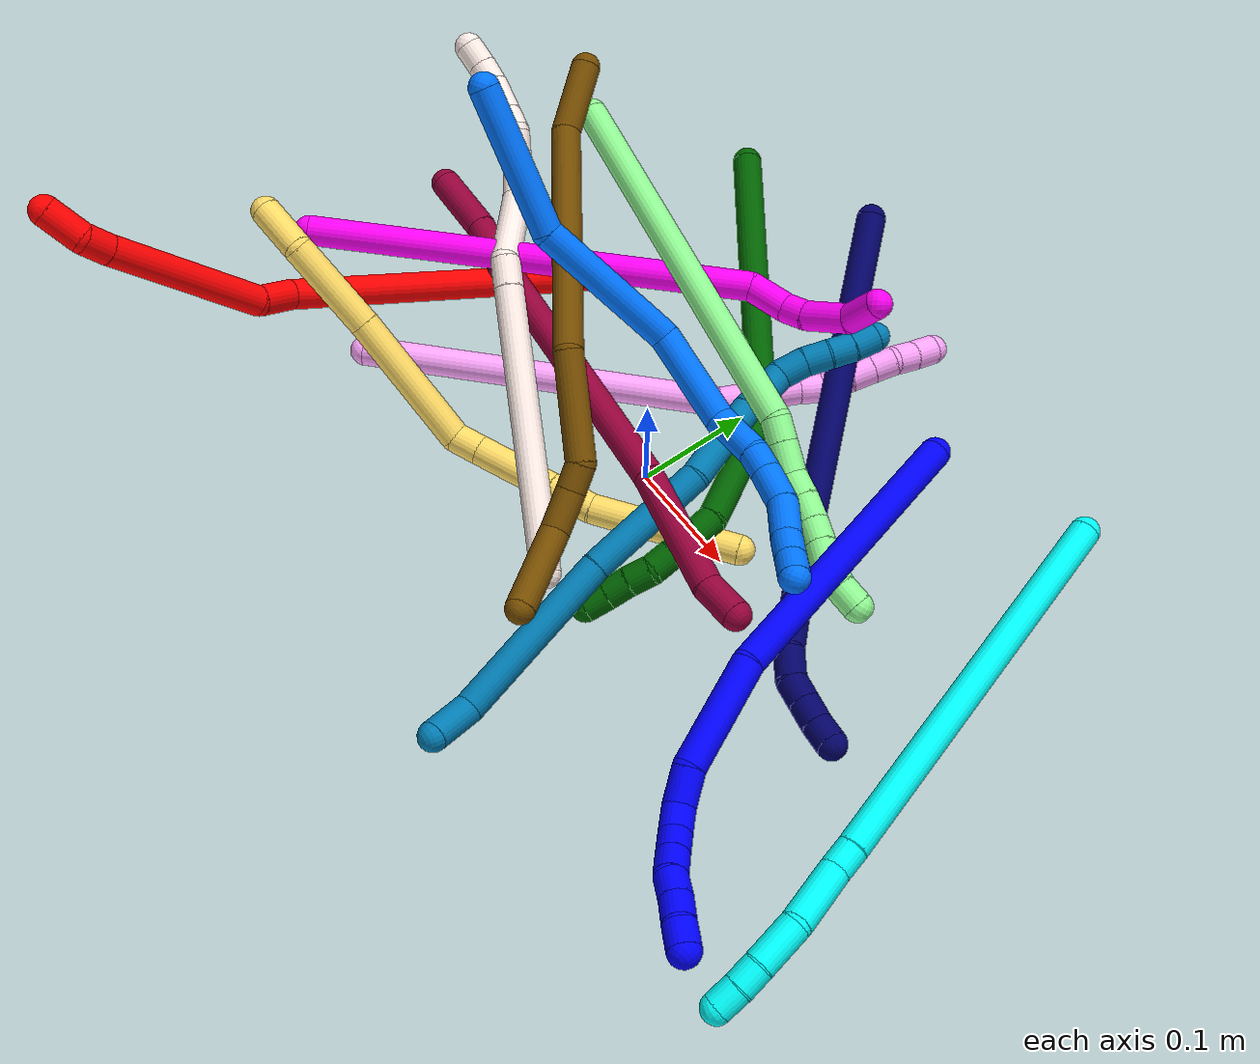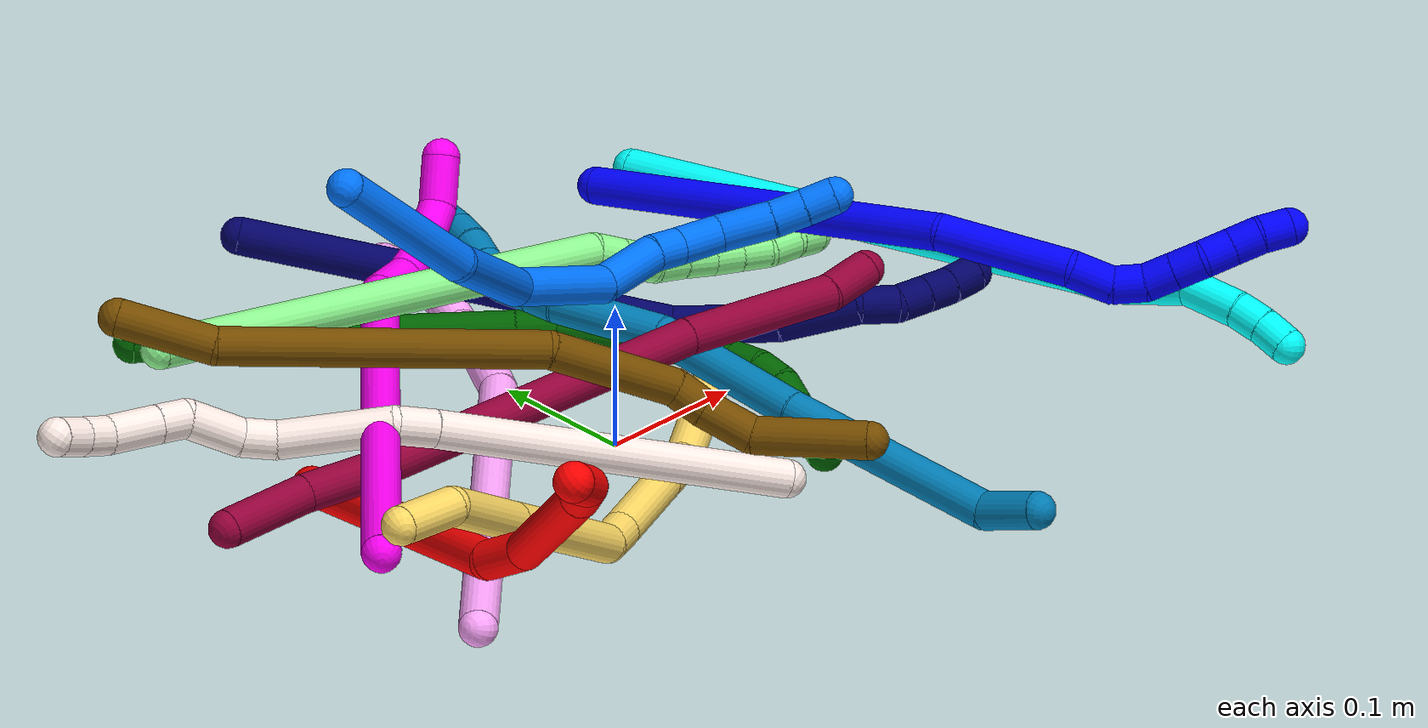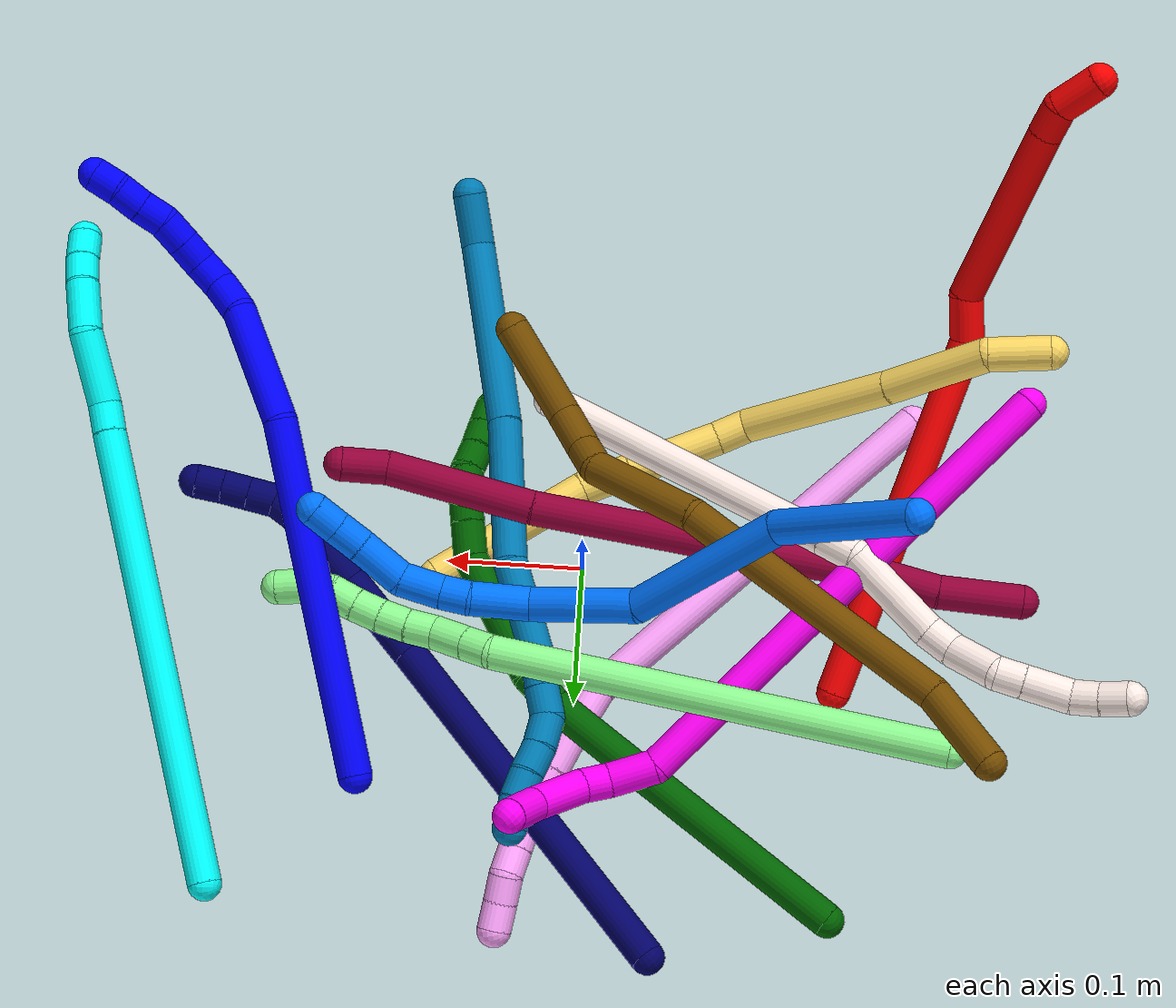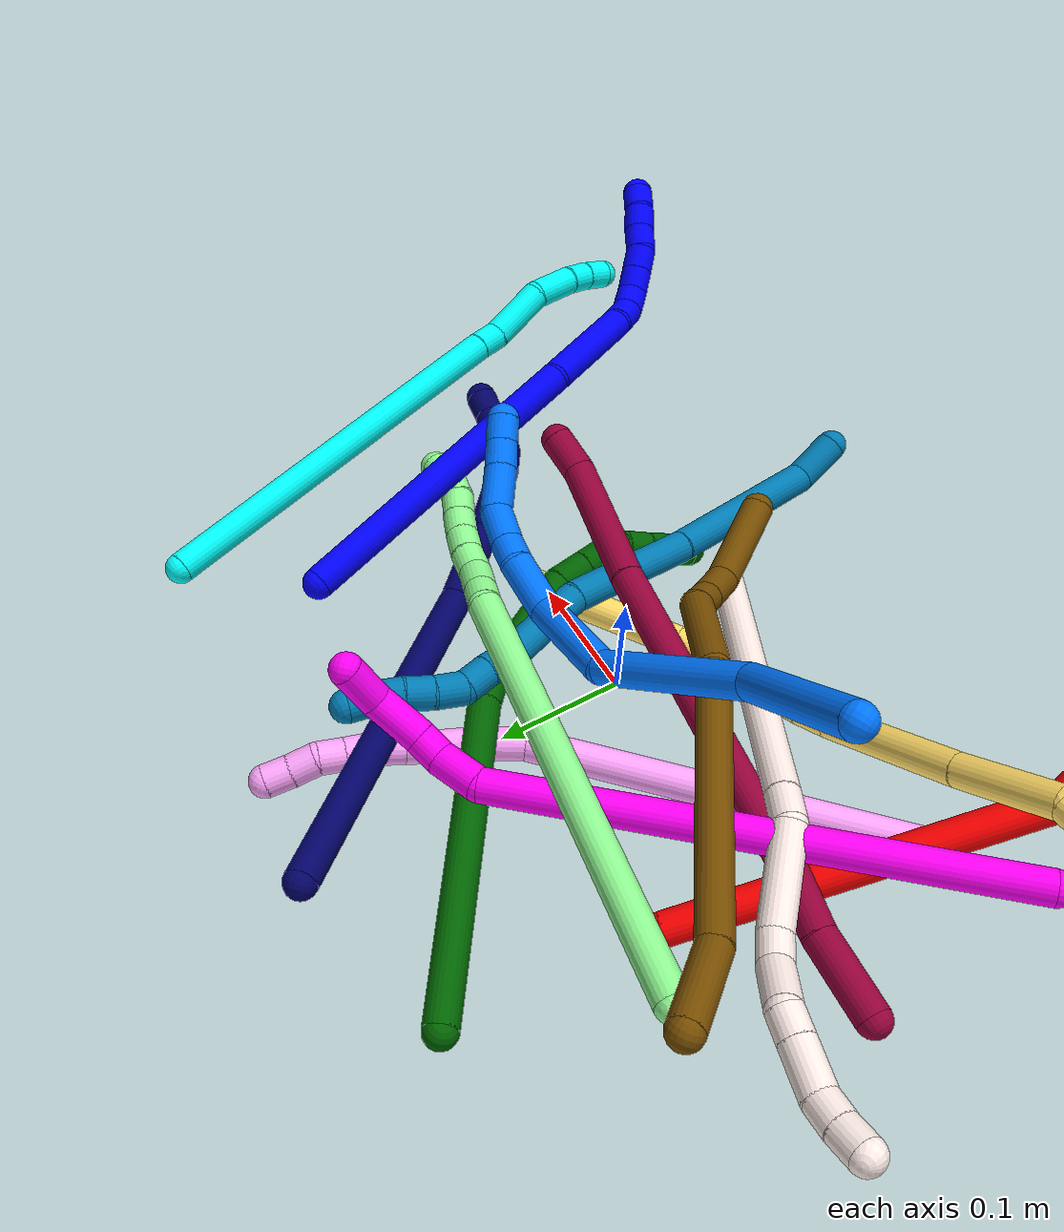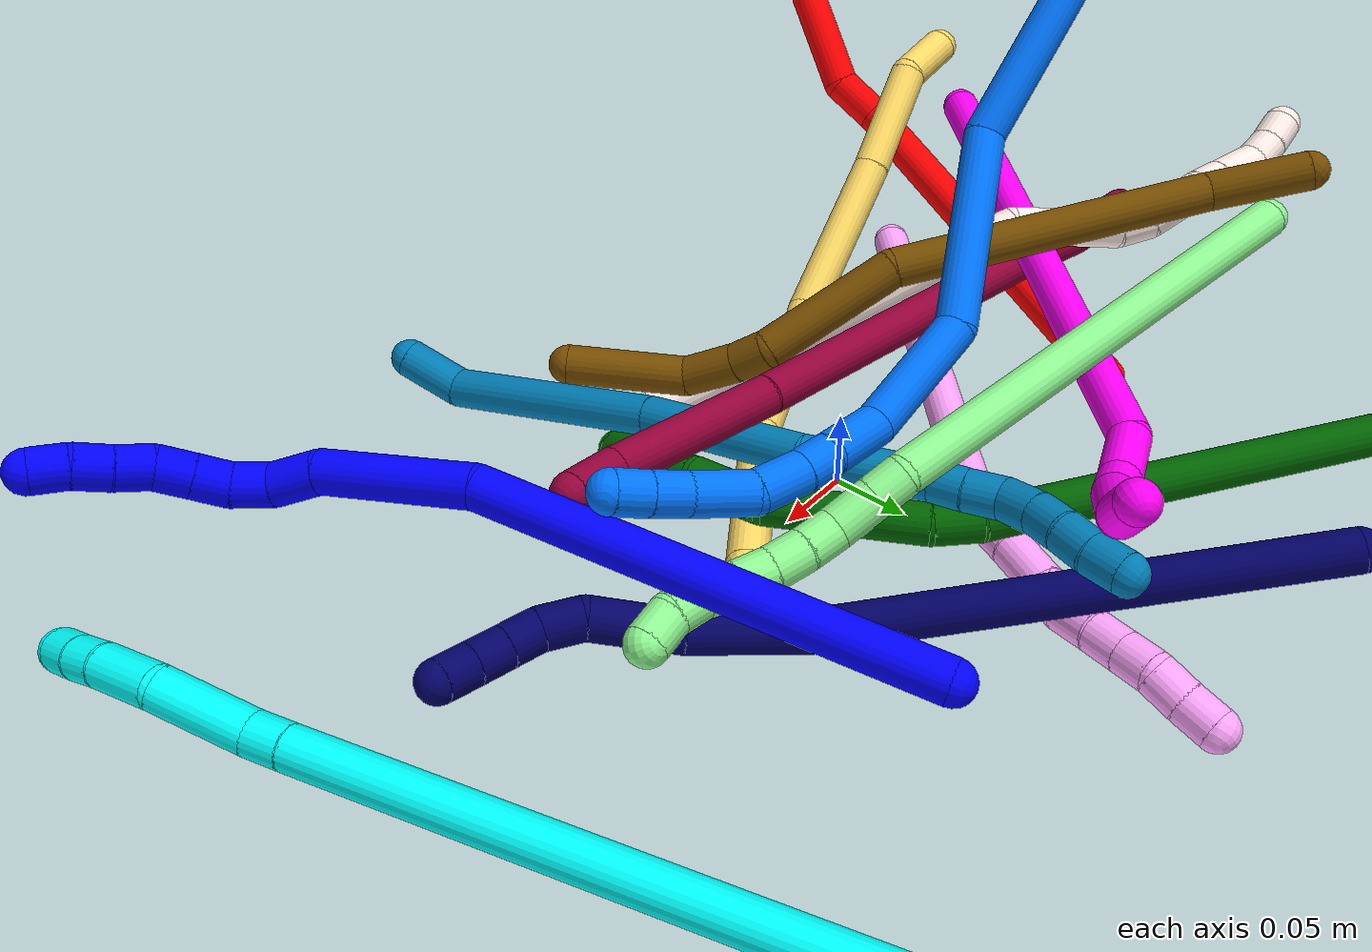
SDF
<sdf version="1.7">
 <world name="default">
  <plugin name="TubeGeneratorPlugin" filename="libtube_generator_plugin.so"/>
  <model name="photoneo_s_sensor">
   <static>1</static>
   <pose>0 0 2 1.57079 1.57079 3.14159</pose>
   <link name="link">
    <inertial><mass>0.1</mass></inertial>
    <sensor name="sensor" type="depth">
     <update_rate>30</update_rate>
     <camera>
      <horizontal_fov>1.22</horizontal_fov>
      <image><width>1920</width><height>1200</height><format>B8G8R8</format></image>
      <clip><near>0.1</near><far>4</far></clip>
      <depth_camera><output>points</output></depth_camera>
     </camera>
     <plugin name="camera_plugin" filename="libgazebo_ros_depth_camera.so">
      <baseline>0.2</baseline>
      <alwaysOn>1</alwaysOn>
      <updateRate>0.0</updateRate>
      <cameraName>camera_ir</cameraName>
      <imageTopicName>/camera/color/image_raw</imageTopicName>
      <cameraInfoTopicName>/camera/color/camera_info</cameraInfoTopicName>
      <depthImageTopicName>/camera/depth/image_raw</depthImageTopicName>
      <depthImageCameraInfoTopicName>/camera/depth/camera_info</depthImageCameraInfoTopicName>
      <pointCloudTopicName>/camera/depth/points</pointCloudTopicName>
      <frameName>fr_optical</frameName>
      <pointCloudCutoff>0.1</pointCloudCutoff>
      <pointCloudCutoffMax>2.0</pointCloudCutoffMax>
      <distortionK1>0</distortionK1>
      <distortionK2>0</distortionK2>
      <distortionK3>0</distortionK3>
      <distortionT1>0</distortionT1>
      <distortionT2>0</distortionT2>
      <CxPrime>0</CxPrime>
      <Cx>0</Cx>
      <Cy>0</Cy>
      <focalLength>0</focalLength>
      <hackBaseline>0</hackBaseline>
     </plugin>
    </sensor>
   </link>
  </model>
  <gravity>0 0 -9.8</gravity>
  <magnetic_field>6e-06 2.3e-05 -4.2e-05</magnetic_field>
  <atmosphere type="adiabatic"/>
  <physics name="default_physics" default="0" type="ode">
   <max_step_size>0.003</max_step_size>
   <real_time_factor>1</real_time_factor>
   <real_time_update_rate>1000</real_time_update_rate>
   <max_contacts>10000</max_contacts>
   <ode>
    <solver>
     <type>quick</type>
     <iters>100</iters>
     <sor>1.3</sor>
     <use_dynamic_moi_rescaling>0</use_dynamic_moi_rescaling>
    </solver>
    <constraints>
     <contact_max_correcting_vel>0</contact_max_correcting_vel>
     <contact_surface_layer>0.001</contact_surface_layer>
     <cfm>0</cfm>
     <erp>0.2</erp>
    </constraints>
   </ode>
  </physics>
  <scene><ambient>0.4 0.4 0.4 1</ambient><background>0.7 0.7 0.7 1</background><shadows>0</shadows></scene>
  <audio><device>default</device></audio>
  <spherical_coordinates>
   <surface_model>EARTH_WGS84</surface_model>
   <latitude_deg>0</latitude_deg>
   <longitude_deg>0</longitude_deg>
   <elevation>0</elevation>
   <heading_deg>0</heading_deg>
  </spherical_coordinates>
  <model name="bin">
   <static>1</static>
   <link name="bottom">
    <collision name="collision-bottom">
     <pose>0 0 -0.01 0 -0 0</pose>
     <geometry><box><size>0.8 0.6 0.02</size></box></geometry>
     <surface>
      <friction><ode><mu>100</mu><mu2>100</mu2></ode></friction>
      <contact><collide_bitmask>65535</collide_bitmask></contact>
     </surface>
    </collision>
   </link>
   <link name="west_wall">
    <collision name="collision-west_wall">
     <pose>-0.41 0 0.1 0 -0 0</pose>
     <geometry><box><size>0.02 0.6 0.2</size></box></geometry>
     <surface>
      <friction><ode><mu>100</mu><mu2>100</mu2></ode></friction>
      <contact><collide_bitmask>65535</collide_bitmask></contact>
     </surface>
    </collision>
   </link>
   <link name="east_wall">
    <collision name="collision-east_wall">
     <pose>0.41 0 0.1 0 -0 0</pose>
     <geometry><box><size>0.02 0.6 0.2</size></box></geometry>
     <surface>
      <friction><ode><mu>100</mu><mu2>100</mu2></ode></friction>
      <contact><collide_bitmask>65535</collide_bitmask></contact>
     </surface>
    </collision>
   </link>
   <link name="south_wall">
    <collision name="collision-south_wall">
     <pose>0 -0.31 0.1 0 -0 0</pose>
     <geometry><box><size>0.8 0.02 0.2</size></box></geometry>
     <surface>
      <friction><ode><mu>100</mu><mu2>100</mu2></ode></friction>
      <contact><collide_bitmask>65535</collide_bitmask></contact>
     </surface>
    </collision>
   </link>
   <link name="north_wall">
    <collision name="collision-north_wall">
     <pose>0 0.31 0.1 0 -0 0</pose>
     <geometry><box><size>0.8 0.02 0.2</size></box></geometry>
     <surface>
      <friction><ode><mu>100</mu><mu2>100</mu2></ode></friction>
      <contact><collide_bitmask>65535</collide_bitmask></contact>
     </surface>
    </collision>
   </link>
  </model>
  <model name="1">
   <static>0</static>
   <link name="1">
    <collision name="collision-cylinder-e_1_1_4">
     <pose>0.00447 -0.000482 0.129517 0.003721 0.034496 6.4e-05</pose>
     <geometry><cylinder><radius>0.0125</radius><length>0.25919</length></cylinder></geometry>
     <surface>
      <friction><ode><mu>1.16</mu><mu2>1.16</mu2><slip1>0</slip1><slip2>0</slip2></ode></friction>
      <contact><ode><kp>1e+06</kp><kd>1</kd><max_vel>0</max_vel><min_depth>0.001</min_depth></ode></contact>
     </surface>
    </collision>
    <visual name="visual-cylinder-e_1_1_4">
     <pose>0.00447 -0.000482 0.129517 0.003721 0.034496 6.4e-05</pose>
     <geometry><cylinder><radius>0.0125</radius><length>0.25919</length></cylinder></geometry>
     <material><ambient>0 0 1 1</ambient></material>
    </visual>
    <collision name="collision-cylinder-e_2_4_5">
     <pose>0.012758 -0.013114 0.3022 0.274367 0.084952 0.011735</pose>
     <geometry><cylinder><radius>0.0125</radius><length>0.090011</length></cylinder></geometry>
     <surface>
      <friction><ode><mu>1.16</mu><mu2>1.16</mu2><slip1>0</slip1><slip2>0</slip2></ode></friction>
      <contact><ode><kp>1e+06</kp><kd>1</kd><max_vel>0</max_vel><min_depth>0.001</min_depth></ode></contact>
     </surface>
    </collision>
    <visual name="visual-cylinder-e_2_4_5">
     <pose>0.012758 -0.013114 0.3022 0.274367 0.084952 0.011735</pose>
     <geometry><cylinder><radius>0.0125</radius><length>0.090011</length></cylinder></geometry>
     <material><ambient>0 0 1 1</ambient></material>
    </visual>
    <collision name="collision-cylinder-e_3_5_6">
     <pose>0.019145 -0.033209 0.356955 0.600998 0.180781 0.056159</pose>
     <geometry><cylinder><radius>0.0125</radius><length>0.028568</length></cylinder></geometry>
     <surface>
      <friction><ode><mu>1.16</mu><mu2>1.16</mu2><slip1>0</slip1><slip2>0</slip2></ode></friction>
      <contact><ode><kp>1e+06</kp><kd>1</kd><max_vel>0</max_vel><min_depth>0.001</min_depth></ode></contact>
     </surface>
    </collision>
    <visual name="visual-cylinder-e_3_5_6">
     <pose>0.019145 -0.033209 0.356955 0.600998 0.180781 0.056159</pose>
     <geometry><cylinder><radius>0.0125</radius><length>0.028568</length></cylinder></geometry>
     <material><ambient>0 0 1 1</ambient></material>
    </visual>
    <collision name="collision-cylinder-e_4_6_7">
     <pose>0.026951 -0.04354 0.377839 0.251277 0.499605 0.064426</pose>
     <geometry><cylinder><radius>0.0125</radius><length>0.021866</length></cylinder></geometry>
     <surface>
      <friction><ode><mu>1.16</mu><mu2>1.16</mu2><slip1>0</slip1><slip2>0</slip2></ode></friction>
      <contact><ode><kp>1e+06</kp><kd>1</kd><max_vel>0</max_vel><min_depth>0.001</min_depth></ode></contact>
     </surface>
    </collision>
    <visual name="visual-cylinder-e_4_6_7">
     <pose>0.026951 -0.04354 0.377839 0.251277 0.499605 0.064426</pose>
     <geometry><cylinder><radius>0.0125</radius><length>0.021866</length></cylinder></geometry>
     <material><ambient>0 0 1 1</ambient></material>
    </visual>
    <collision name="collision-cylinder-e_5_7_8">
     <pose>0.038068 -0.044754 0.395339 -0.141891 0.616997 -0.045285</pose>
     <geometry><cylinder><radius>0.0125</radius><length>0.020324</length></cylinder></geometry>
     <surface>
      <friction><ode><mu>1.16</mu><mu2>1.16</mu2><slip1>0</slip1><slip2>0</slip2></ode></friction>
      <contact><ode><kp>1e+06</kp><kd>1</kd><max_vel>0</max_vel><min_depth>0.001</min_depth></ode></contact>
     </surface>
    </collision>
    <visual name="visual-cylinder-e_5_7_8">
     <pose>0.038068 -0.044754 0.395339 -0.141891 0.616997 -0.045285</pose>
     <geometry><cylinder><radius>0.0125</radius><length>0.020324</length></cylinder></geometry>
     <material><ambient>0 0 1 1</ambient></material>
    </visual>
    <collision name="collision-cylinder-e_6_8_9">
     <pose>0.049811 -0.0425 0.411586 -0.133756 0.625726 -0.043326</pose>
     <geometry><cylinder><radius>0.0125</radius><length>0.020021</length></cylinder></geometry>
     <surface>
      <friction><ode><mu>1.16</mu><mu2>1.16</mu2><slip1>0</slip1><slip2>0</slip2></ode></friction>
      <contact><ode><kp>1e+06</kp><kd>1</kd><max_vel>0</max_vel><min_depth>0.001</min_depth></ode></contact>
     </surface>
    </collision>
    <visual name="visual-cylinder-e_6_8_9">
     <pose>0.049811 -0.0425 0.411586 -0.133756 0.625726 -0.043326</pose>
     <geometry><cylinder><radius>0.0125</radius><length>0.020021</length></cylinder></geometry>
     <material><ambient>0 0 1 1</ambient></material>
    </visual>
    <collision name="collision-cylinder-e_7_9_10">
     <pose>0.063205 -0.042232 0.426165 0.123794 0.85214 0.056244</pose>
     <geometry><cylinder><radius>0.0125</radius><length>0.020012</length></cylinder></geometry>
     <surface>
      <friction><ode><mu>1.16</mu><mu2>1.16</mu2><slip1>0</slip1><slip2>0</slip2></ode></friction>
      <contact><ode><kp>1e+06</kp><kd>1</kd><max_vel>0</max_vel><min_depth>0.001</min_depth></ode></contact>
     </surface>
    </collision>
    <visual name="visual-cylinder-e_7_9_10">
     <pose>0.063205 -0.042232 0.426165 0.123794 0.85214 0.056244</pose>
     <geometry><cylinder><radius>0.0125</radius><length>0.020012</length></cylinder></geometry>
     <material><ambient>0 0 1 1</ambient></material>
    </visual>
    <collision name="collision-cylinder-e_8_10_11">
     <pose>0.077801 -0.043201 0.439781 0.022027 0.784204 0.009109</pose>
     <geometry><cylinder><radius>0.0125</radius><length>0.020005</length></cylinder></geometry>
     <surface>
      <friction><ode><mu>1.16</mu><mu2>1.16</mu2><slip1>0</slip1><slip2>0</slip2></ode></friction>
      <contact><ode><kp>1e+06</kp><kd>1</kd><max_vel>0</max_vel><min_depth>0.001</min_depth></ode></contact>
     </surface>
    </collision>
    <visual name="visual-cylinder-e_8_10_11">
     <pose>0.077801 -0.043201 0.439781 0.022027 0.784204 0.009109</pose>
     <geometry><cylinder><radius>0.0125</radius><length>0.020005</length></cylinder></geometry>
     <material><ambient>0 0 1 1</ambient></material>
    </visual>
    <collision name="collision-cylinder-e_9_11_2">
     <pose>0.091949 -0.045546 0.453574 0.31519 0.787059 0.131766</pose>
     <geometry><cylinder><radius>0.0125</radius><length>0.020003</length></cylinder></geometry>
     <surface>
      <friction><ode><mu>1.16</mu><mu2>1.16</mu2><slip1>0</slip1><slip2>0</slip2></ode></friction>
      <contact><ode><kp>1e+06</kp><kd>1</kd><max_vel>0</max_vel><min_depth>0.001</min_depth></ode></contact>
     </surface>
    </collision>
    <visual name="visual-cylinder-e_9_11_2">
     <pose>0.091949 -0.045546 0.453574 0.31519 0.787059 0.131766</pose>
     <geometry><cylinder><radius>0.0125</radius><length>0.020003</length></cylinder></geometry>
     <material><ambient>0 0 1 1</ambient></material>
    </visual>
    <collision name="collision-sphere-2">
     <pose>0.099033 -0.047735 0.460286 0 -0 0</pose>
     <geometry><sphere><radius>0.0125</radius></sphere></geometry>
     <surface>
      <friction><ode><mu>1.16</mu><mu2>1.16</mu2><slip1>0</slip1><slip2>0</slip2></ode></friction>
      <contact><ode><kp>1e+06</kp><kd>1</kd><max_vel>0</max_vel><min_depth>0.001</min_depth></ode></contact>
     </surface>
    </collision>
    <visual name="visual-sphere-2">
     <pose>0.099033 -0.047735 0.460286 0 -0 0</pose>
     <geometry><sphere><radius>0.0125</radius></sphere></geometry>
     <material><ambient>0 0 1 1</ambient></material>
    </visual>
    <collision name="collision-sphere-11">
     <pose>0.084866 -0.043357 0.446861 0 -0 0</pose>
     <geometry><sphere><radius>0.0125</radius></sphere></geometry>
     <surface>
      <friction><ode><mu>1.16</mu><mu2>1.16</mu2><slip1>0</slip1><slip2>0</slip2></ode></friction>
      <contact><ode><kp>1e+06</kp><kd>1</kd><max_vel>0</max_vel><min_depth>0.001</min_depth></ode></contact>
     </surface>
    </collision>
    <visual name="visual-sphere-11">
     <pose>0.084866 -0.043357 0.446861 0 -0 0</pose>
     <geometry><sphere><radius>0.0125</radius></sphere></geometry>
     <material><ambient>0 0 1 1</ambient></material>
    </visual>
    <collision name="collision-sphere-10">
     <pose>0.070737 -0.043045 0.432702 0 -0 0</pose>
     <geometry><sphere><radius>0.0125</radius></sphere></geometry>
     <surface>
      <friction><ode><mu>1.16</mu><mu2>1.16</mu2><slip1>0</slip1><slip2>0</slip2></ode></friction>
      <contact><ode><kp>1e+06</kp><kd>1</kd><max_vel>0</max_vel><min_depth>0.001</min_depth></ode></contact>
     </surface>
    </collision>
    <visual name="visual-sphere-10">
     <pose>0.070737 -0.043045 0.432702 0 -0 0</pose>
     <geometry><sphere><radius>0.0125</radius></sphere></geometry>
     <material><ambient>0 0 1 1</ambient></material>
    </visual>
    <collision name="collision-sphere-9">
     <pose>0.055674 -0.041418 0.419627 0 -0 0</pose>
     <geometry><sphere><radius>0.0125</radius></sphere></geometry>
     <surface>
      <friction><ode><mu>1.16</mu><mu2>1.16</mu2><slip1>0</slip1><slip2>0</slip2></ode></friction>
      <contact><ode><kp>1e+06</kp><kd>1</kd><max_vel>0</max_vel><min_depth>0.001</min_depth></ode></contact>
     </surface>
    </collision>
    <visual name="visual-sphere-9">
     <pose>0.055674 -0.041418 0.419627 0 -0 0</pose>
     <geometry><sphere><radius>0.0125</radius></sphere></geometry>
     <material><ambient>0 0 1 1</ambient></material>
    </visual>
    <collision name="collision-sphere-4">
     <pose>0.008939 -0.000964 0.259034 0 -0 0</pose>
     <geometry><sphere><radius>0.0125</radius></sphere></geometry>
     <surface>
      <friction><ode><mu>1.16</mu><mu2>1.16</mu2><slip1>0</slip1><slip2>0</slip2></ode></friction>
      <contact><ode><kp>1e+06</kp><kd>1</kd><max_vel>0</max_vel><min_depth>0.001</min_depth></ode></contact>
     </surface>
    </collision>
    <visual name="visual-sphere-4">
     <pose>0.008939 -0.000964 0.259034 0 -0 0</pose>
     <geometry><sphere><radius>0.0125</radius></sphere></geometry>
     <material><ambient>0 0 1 1</ambient></material>
    </visual>
    <collision name="collision-sphere-1">
     <geometry><sphere><radius>0.0125</radius></sphere></geometry>
     <surface>
      <friction><ode><mu>1.16</mu><mu2>1.16</mu2><slip1>0</slip1><slip2>0</slip2></ode></friction>
      <contact><ode><kp>1e+06</kp><kd>1</kd><max_vel>0</max_vel><min_depth>0.001</min_depth></ode></contact>
     </surface>
    </collision>
    <visual name="visual-sphere-1">
     <geometry><sphere><radius>0.0125</radius></sphere></geometry>
     <material><ambient>0 0 1 1</ambient></material>
    </visual>
    <collision name="collision-sphere-8">
     <pose>0.043948 -0.043582 0.403544 0 -0 0</pose>
     <geometry><sphere><radius>0.0125</radius></sphere></geometry>
     <surface>
      <friction><ode><mu>1.16</mu><mu2>1.16</mu2><slip1>0</slip1><slip2>0</slip2></ode></friction>
      <contact><ode><kp>1e+06</kp><kd>1</kd><max_vel>0</max_vel><min_depth>0.001</min_depth></ode></contact>
     </surface>
    </collision>
    <visual name="visual-sphere-8">
     <pose>0.043948 -0.043582 0.403544 0 -0 0</pose>
     <geometry><sphere><radius>0.0125</radius></sphere></geometry>
     <material><ambient>0 0 1 1</ambient></material>
    </visual>
    <collision name="collision-sphere-5">
     <pose>0.016577 -0.025263 0.345366 0 -0 0</pose>
     <geometry><sphere><radius>0.0125</radius></sphere></geometry>
     <surface>
      <friction><ode><mu>1.16</mu><mu2>1.16</mu2><slip1>0</slip1><slip2>0</slip2></ode></friction>
      <contact><ode><kp>1e+06</kp><kd>1</kd><max_vel>0</max_vel><min_depth>0.001</min_depth></ode></contact>
     </surface>
    </collision>
    <visual name="visual-sphere-5">
     <pose>0.016577 -0.025263 0.345366 0 -0 0</pose>
     <geometry><sphere><radius>0.0125</radius></sphere></geometry>
     <material><ambient>0 0 1 1</ambient></material>
    </visual>
    <collision name="collision-sphere-6">
     <pose>0.021713 -0.041154 0.368544 0 -0 0</pose>
     <geometry><sphere><radius>0.0125</radius></sphere></geometry>
     <surface>
      <friction><ode><mu>1.16</mu><mu2>1.16</mu2><slip1>0</slip1><slip2>0</slip2></ode></friction>
      <contact><ode><kp>1e+06</kp><kd>1</kd><max_vel>0</max_vel><min_depth>0.001</min_depth></ode></contact>
     </surface>
    </collision>
    <visual name="visual-sphere-6">
     <pose>0.021713 -0.041154 0.368544 0 -0 0</pose>
     <geometry><sphere><radius>0.0125</radius></sphere></geometry>
     <material><ambient>0 0 1 1</ambient></material>
    </visual>
    <collision name="collision-sphere-7">
     <pose>0.032188 -0.045927 0.387134 0 -0 0</pose>
     <geometry><sphere><radius>0.0125</radius></sphere></geometry>
     <surface>
      <friction><ode><mu>1.16</mu><mu2>1.16</mu2><slip1>0</slip1><slip2>0</slip2></ode></friction>
      <contact><ode><kp>1e+06</kp><kd>1</kd><max_vel>0</max_vel><min_depth>0.001</min_depth></ode></contact>
     </surface>
    </collision>
    <visual name="visual-sphere-7">
     <pose>0.032188 -0.045927 0.387134 0 -0 0</pose>
     <geometry><sphere><radius>0.0125</radius></sphere></geometry>
     <material><ambient>0 0 1 1</ambient></material>
    </visual>
    <inertial>
     <pose>0.019749 -0.015174 0.243809 0 -0 0</pose>
     <mass>0.5</mass>
     <inertia><ixx>0.001543</ixx><ixy>0</ixy><ixz>0</ixz><iyy>0.001532</iyy><iyz>0</iyz><izz>-1e-06</izz></inertia>
    </inertial>
   </link>
   <pose>0.149999 0.173331 0.066318 1.44043 -0.37598 0.294146</pose>
  </model>
  <model name="2">
   <static>0</static>
   <link name="2">
    <collision name="collision-cylinder-e_1_1_4">
     <pose>0.003192 -0.111899 0.077796 0.963275 0.023416 0.01224</pose>
     <geometry><cylinder><radius>0.0125</radius><length>0.272644</length></cylinder></geometry>
     <surface>
      <friction><ode><mu>1.16</mu><mu2>1.16</mu2><slip1>0</slip1><slip2>0</slip2></ode></friction>
      <contact><ode><kp>1e+06</kp><kd>1</kd><max_vel>0</max_vel><min_depth>0.001</min_depth></ode></contact>
     </surface>
    </collision>
    <visual name="visual-cylinder-e_1_1_4">
     <pose>0.003192 -0.111899 0.077796 0.963275 0.023416 0.01224</pose>
     <geometry><cylinder><radius>0.0125</radius><length>0.272644</length></cylinder></geometry>
     <material><ambient>1 0 0 1</ambient></material>
    </visual>
    <collision name="collision-cylinder-e_2_4_5">
     <pose>0.00763 -0.232068 0.170659 0.502004 0.072409 0.018574</pose>
     <geometry><cylinder><radius>0.0125</radius><length>0.034466</length></cylinder></geometry>
     <surface>
      <friction><ode><mu>1.16</mu><mu2>1.16</mu2><slip1>0</slip1><slip2>0</slip2></ode></friction>
      <contact><ode><kp>1e+06</kp><kd>1</kd><max_vel>0</max_vel><min_depth>0.001</min_depth></ode></contact>
     </surface>
    </collision>
    <visual name="visual-cylinder-e_2_4_5">
     <pose>0.00763 -0.232068 0.170659 0.502004 0.072409 0.018574</pose>
     <geometry><cylinder><radius>0.0125</radius><length>0.034466</length></cylinder></geometry>
     <material><ambient>1 0 0 1</ambient></material>
    </visual>
    <collision name="collision-cylinder-e_3_5_6">
     <pose>-0.014732 -0.282681 0.23357 0.724483 -0.353971 -0.135353</pose>
     <geometry><cylinder><radius>0.0125</radius><length>0.136225</length></cylinder></geometry>
     <surface>
      <friction><ode><mu>1.16</mu><mu2>1.16</mu2><slip1>0</slip1><slip2>0</slip2></ode></friction>
      <contact><ode><kp>1e+06</kp><kd>1</kd><max_vel>0</max_vel><min_depth>0.001</min_depth></ode></contact>
     </surface>
    </collision>
    <visual name="visual-cylinder-e_3_5_6">
     <pose>-0.014732 -0.282681 0.23357 0.724483 -0.353971 -0.135353</pose>
     <geometry><cylinder><radius>0.0125</radius><length>0.136225</length></cylinder></geometry>
     <material><ambient>1 0 0 1</ambient></material>
    </visual>
    <collision name="collision-cylinder-e_4_6_7">
     <pose>-0.043186 -0.331814 0.289452 0.701419 -0.43141 -0.159976</pose>
     <geometry><cylinder><radius>0.0125</radius><length>0.023169</length></cylinder></geometry>
     <surface>
      <friction><ode><mu>1.16</mu><mu2>1.16</mu2><slip1>0</slip1><slip2>0</slip2></ode></friction>
      <contact><ode><kp>1e+06</kp><kd>1</kd><max_vel>0</max_vel><min_depth>0.001</min_depth></ode></contact>
     </surface>
    </collision>
    <visual name="visual-cylinder-e_4_6_7">
     <pose>-0.043186 -0.331814 0.289452 0.701419 -0.43141 -0.159976</pose>
     <geometry><cylinder><radius>0.0125</radius><length>0.023169</length></cylinder></geometry>
     <material><ambient>1 0 0 1</ambient></material>
    </visual>
    <collision name="collision-cylinder-e_5_7_2">
     <pose>-0.058304 -0.35095 0.30224 1.20358 -0.6604 -0.462358</pose>
     <geometry><cylinder><radius>0.0125</radius><length>0.033496</length></cylinder></geometry>
     <surface>
      <friction><ode><mu>1.16</mu><mu2>1.16</mu2><slip1>0</slip1><slip2>0</slip2></ode></friction>
      <contact><ode><kp>1e+06</kp><kd>1</kd><max_vel>0</max_vel><min_depth>0.001</min_depth></ode></contact>
     </surface>
    </collision>
    <visual name="visual-cylinder-e_5_7_2">
     <pose>-0.058304 -0.35095 0.30224 1.20358 -0.6604 -0.462358</pose>
     <geometry><cylinder><radius>0.0125</radius><length>0.033496</length></cylinder></geometry>
     <material><ambient>1 0 0 1</ambient></material>
    </visual>
    <collision name="collision-sphere-2">
     <pose>-0.068577 -0.363295 0.306988 0 -0 0</pose>
     <geometry><sphere><radius>0.0125</radius></sphere></geometry>
     <surface>
      <friction><ode><mu>1.16</mu><mu2>1.16</mu2><slip1>0</slip1><slip2>0</slip2></ode></friction>
      <contact><ode><kp>1e+06</kp><kd>1</kd><max_vel>0</max_vel><min_depth>0.001</min_depth></ode></contact>
     </surface>
    </collision>
    <visual name="visual-sphere-2">
     <pose>-0.068577 -0.363295 0.306988 0 -0 0</pose>
     <geometry><sphere><radius>0.0125</radius></sphere></geometry>
     <material><ambient>1 0 0 1</ambient></material>
    </visual>
    <collision name="collision-sphere-7">
     <pose>-0.04803 -0.338605 0.297491 0 -0 0</pose>
     <geometry><sphere><radius>0.0125</radius></sphere></geometry>
     <surface>
      <friction><ode><mu>1.16</mu><mu2>1.16</mu2><slip1>0</slip1><slip2>0</slip2></ode></friction>
      <contact><ode><kp>1e+06</kp><kd>1</kd><max_vel>0</max_vel><min_depth>0.001</min_depth></ode></contact>
     </surface>
    </collision>
    <visual name="visual-sphere-7">
     <pose>-0.04803 -0.338605 0.297491 0 -0 0</pose>
     <geometry><sphere><radius>0.0125</radius></sphere></geometry>
     <material><ambient>1 0 0 1</ambient></material>
    </visual>
    <collision name="collision-sphere-6">
     <pose>-0.038342 -0.325024 0.281413 0 -0 0</pose>
     <geometry><sphere><radius>0.0125</radius></sphere></geometry>
     <surface>
      <friction><ode><mu>1.16</mu><mu2>1.16</mu2><slip1>0</slip1><slip2>0</slip2></ode></friction>
      <contact><ode><kp>1e+06</kp><kd>1</kd><max_vel>0</max_vel><min_depth>0.001</min_depth></ode></contact>
     </surface>
    </collision>
    <visual name="visual-sphere-6">
     <pose>-0.038342 -0.325024 0.281413 0 -0 0</pose>
     <geometry><sphere><radius>0.0125</radius></sphere></geometry>
     <material><ambient>1 0 0 1</ambient></material>
    </visual>
    <collision name="collision-sphere-5">
     <pose>0.008877 -0.240338 0.185727 0 -0 0</pose>
     <geometry><sphere><radius>0.0125</radius></sphere></geometry>
     <surface>
      <friction><ode><mu>1.16</mu><mu2>1.16</mu2><slip1>0</slip1><slip2>0</slip2></ode></friction>
      <contact><ode><kp>1e+06</kp><kd>1</kd><max_vel>0</max_vel><min_depth>0.001</min_depth></ode></contact>
     </surface>
    </collision>
    <visual name="visual-sphere-5">
     <pose>0.008877 -0.240338 0.185727 0 -0 0</pose>
     <geometry><sphere><radius>0.0125</radius></sphere></geometry>
     <material><ambient>1 0 0 1</ambient></material>
    </visual>
    <collision name="collision-sphere-1">
     <geometry><sphere><radius>0.0125</radius></sphere></geometry>
     <surface>
      <friction><ode><mu>1.16</mu><mu2>1.16</mu2><slip1>0</slip1><slip2>0</slip2></ode></friction>
      <contact><ode><kp>1e+06</kp><kd>1</kd><max_vel>0</max_vel><min_depth>0.001</min_depth></ode></contact>
     </surface>
    </collision>
    <visual name="visual-sphere-1">
     <geometry><sphere><radius>0.0125</radius></sphere></geometry>
     <material><ambient>1 0 0 1</ambient></material>
    </visual>
    <collision name="collision-sphere-4">
     <pose>0.006384 -0.223797 0.155592 0 -0 0</pose>
     <geometry><sphere><radius>0.0125</radius></sphere></geometry>
     <surface>
      <friction><ode><mu>1.16</mu><mu2>1.16</mu2><slip1>0</slip1><slip2>0</slip2></ode></friction>
      <contact><ode><kp>1e+06</kp><kd>1</kd><max_vel>0</max_vel><min_depth>0.001</min_depth></ode></contact>
     </surface>
    </collision>
    <visual name="visual-sphere-4">
     <pose>0.006384 -0.223797 0.155592 0 -0 0</pose>
     <geometry><sphere><radius>0.0125</radius></sphere></geometry>
     <material><ambient>1 0 0 1</ambient></material>
    </visual>
    <inertial>
     <pose>-0.007654 -0.192917 0.151481 0 -0 0</pose>
     <mass>0.5</mass>
     <inertia>
      <ixx>0.001896</ixx>
      <ixy>0</ixy>
      <ixz>0</ixz>
      <iyy>0.001109</iyy>
      <iyz>0</iyz>
      <izz>0.001598</izz>
     </inertia>
    </inertial>
   </link>
   <pose>-0.188349 0.082331 0.012288 0.151745 0.770255 -0.653409</pose>
  </model>
  <model name="3">
   <static>0</static>
   <link name="3">
    <collision name="collision-cylinder-e_1_1_4">
     <pose>-0.015873 -0.158498 0.060982 1.20351 -0.093195 -0.064023</pose>
     <geometry><cylinder><radius>0.0125</radius><length>0.341129</length></cylinder></geometry>
     <surface>
      <friction><ode><mu>1.16</mu><mu2>1.16</mu2><slip1>0</slip1><slip2>0</slip2></ode></friction>
      <contact><ode><kp>1e+06</kp><kd>1</kd><max_vel>0</max_vel><min_depth>0.001</min_depth></ode></contact>
     </surface>
    </collision>
    <visual name="visual-cylinder-e_1_1_4">
     <pose>-0.015873 -0.158498 0.060982 1.20351 -0.093195 -0.064023</pose>
     <geometry><cylinder><radius>0.0125</radius><length>0.341129</length></cylinder></geometry>
     <material><ambient>0.003922 1 0.996078 1</ambient></material>
    </visual>
    <collision name="collision-cylinder-e_2_4_5">
     <pose>-0.032137 -0.327615 0.125755 1.22786 -0.034684 -0.024446</pose>
     <geometry><cylinder><radius>0.0125</radius><length>0.022564</length></cylinder></geometry>
     <surface>
      <friction><ode><mu>1.16</mu><mu2>1.16</mu2><slip1>0</slip1><slip2>0</slip2></ode></friction>
      <contact><ode><kp>1e+06</kp><kd>1</kd><max_vel>0</max_vel><min_depth>0.001</min_depth></ode></contact>
     </surface>
    </collision>
    <visual name="visual-cylinder-e_2_4_5">
     <pose>-0.032137 -0.327615 0.125755 1.22786 -0.034684 -0.024446</pose>
     <geometry><cylinder><radius>0.0125</radius><length>0.022564</length></cylinder></geometry>
     <material><ambient>0.003922 1 0.996078 1</ambient></material>
    </visual>
    <collision name="collision-cylinder-e_3_5_6">
     <pose>-0.040618 -0.363159 0.138436 1.2282 -0.296689 -0.209952</pose>
     <geometry><cylinder><radius>0.0125</radius><length>0.055344</length></cylinder></geometry>
     <surface>
      <friction><ode><mu>1.16</mu><mu2>1.16</mu2><slip1>0</slip1><slip2>0</slip2></ode></friction>
      <contact><ode><kp>1e+06</kp><kd>1</kd><max_vel>0</max_vel><min_depth>0.001</min_depth></ode></contact>
     </surface>
    </collision>
    <visual name="visual-cylinder-e_3_5_6">
     <pose>-0.040618 -0.363159 0.138436 1.2282 -0.296689 -0.209952</pose>
     <geometry><cylinder><radius>0.0125</radius><length>0.055344</length></cylinder></geometry>
     <material><ambient>0.003922 1 0.996078 1</ambient></material>
    </visual>
    <collision name="collision-cylinder-e_4_6_7">
     <pose>-0.047264 -0.406798 0.152992 1.27679 0.073743 0.054732</pose>
     <geometry><cylinder><radius>0.0125</radius><length>0.039214</length></cylinder></geometry>
     <surface>
      <friction><ode><mu>1.16</mu><mu2>1.16</mu2><slip1>0</slip1><slip2>0</slip2></ode></friction>
      <contact><ode><kp>1e+06</kp><kd>1</kd><max_vel>0</max_vel><min_depth>0.001</min_depth></ode></contact>
     </surface>
    </collision>
    <visual name="visual-cylinder-e_4_6_7">
     <pose>-0.047264 -0.406798 0.152992 1.27679 0.073743 0.054732</pose>
     <geometry><cylinder><radius>0.0125</radius><length>0.039214</length></cylinder></geometry>
     <material><ambient>0.003922 1 0.996078 1</ambient></material>
    </visual>
    <collision name="collision-cylinder-e_5_7_8">
     <pose>-0.043515 -0.435173 0.161645 1.27091 0.224036 0.165543</pose>
     <geometry><cylinder><radius>0.0125</radius><length>0.020741</length></cylinder></geometry>
     <surface>
      <friction><ode><mu>1.16</mu><mu2>1.16</mu2><slip1>0</slip1><slip2>0</slip2></ode></friction>
      <contact><ode><kp>1e+06</kp><kd>1</kd><max_vel>0</max_vel><min_depth>0.001</min_depth></ode></contact>
     </surface>
    </collision>
    <visual name="visual-cylinder-e_5_7_8">
     <pose>-0.043515 -0.435173 0.161645 1.27091 0.224036 0.165543</pose>
     <geometry><cylinder><radius>0.0125</radius><length>0.020741</length></cylinder></geometry>
     <material><ambient>0.003922 1 0.996078 1</ambient></material>
    </visual>
    <collision name="collision-cylinder-e_6_8_2">
     <pose>-0.037979 -0.454568 0.166894 1.34254 0.312788 0.249203</pose>
     <geometry><cylinder><radius>0.0125</radius><length>0.021007</length></cylinder></geometry>
     <surface>
      <friction><ode><mu>1.16</mu><mu2>1.16</mu2><slip1>0</slip1><slip2>0</slip2></ode></friction>
      <contact><ode><kp>1e+06</kp><kd>1</kd><max_vel>0</max_vel><min_depth>0.001</min_depth></ode></contact>
     </surface>
    </collision>
    <visual name="visual-cylinder-e_6_8_2">
     <pose>-0.037979 -0.454568 0.166894 1.34254 0.312788 0.249203</pose>
     <geometry><cylinder><radius>0.0125</radius><length>0.021007</length></cylinder></geometry>
     <material><ambient>0.003922 1 0.996078 1</ambient></material>
    </visual>
    <collision name="collision-sphere-2">
     <pose>-0.034747 -0.464303 0.169155 0 -0 0</pose>
     <geometry><sphere><radius>0.0125</radius></sphere></geometry>
     <surface>
      <friction><ode><mu>1.16</mu><mu2>1.16</mu2><slip1>0</slip1><slip2>0</slip2></ode></friction>
      <contact><ode><kp>1e+06</kp><kd>1</kd><max_vel>0</max_vel><min_depth>0.001</min_depth></ode></contact>
     </surface>
    </collision>
    <visual name="visual-sphere-2">
     <pose>-0.034747 -0.464303 0.169155 0 -0 0</pose>
     <geometry><sphere><radius>0.0125</radius></sphere></geometry>
     <material><ambient>0.003922 1 0.996078 1</ambient></material>
    </visual>
    <collision name="collision-sphere-4">
     <pose>-0.031746 -0.316996 0.121963 0 -0 0</pose>
     <geometry><sphere><radius>0.0125</radius></sphere></geometry>
     <surface>
      <friction><ode><mu>1.16</mu><mu2>1.16</mu2><slip1>0</slip1><slip2>0</slip2></ode></friction>
      <contact><ode><kp>1e+06</kp><kd>1</kd><max_vel>0</max_vel><min_depth>0.001</min_depth></ode></contact>
     </surface>
    </collision>
    <visual name="visual-sphere-4">
     <pose>-0.031746 -0.316996 0.121963 0 -0 0</pose>
     <geometry><sphere><radius>0.0125</radius></sphere></geometry>
     <material><ambient>0.003922 1 0.996078 1</ambient></material>
    </visual>
    <collision name="collision-sphere-1">
     <geometry><sphere><radius>0.0125</radius></sphere></geometry>
     <surface>
      <friction><ode><mu>1.16</mu><mu2>1.16</mu2><slip1>0</slip1><slip2>0</slip2></ode></friction>
      <contact><ode><kp>1e+06</kp><kd>1</kd><max_vel>0</max_vel><min_depth>0.001</min_depth></ode></contact>
     </surface>
    </collision>
    <visual name="visual-sphere-1">
     <geometry><sphere><radius>0.0125</radius></sphere></geometry>
     <material><ambient>0.003922 1 0.996078 1</ambient></material>
    </visual>
    <collision name="collision-sphere-8">
     <pose>-0.041211 -0.444833 0.164632 0 -0 0</pose>
     <geometry><sphere><radius>0.0125</radius></sphere></geometry>
     <surface>
      <friction><ode><mu>1.16</mu><mu2>1.16</mu2><slip1>0</slip1><slip2>0</slip2></ode></friction>
      <contact><ode><kp>1e+06</kp><kd>1</kd><max_vel>0</max_vel><min_depth>0.001</min_depth></ode></contact>
     </surface>
    </collision>
    <visual name="visual-sphere-8">
     <pose>-0.041211 -0.444833 0.164632 0 -0 0</pose>
     <geometry><sphere><radius>0.0125</radius></sphere></geometry>
     <material><ambient>0.003922 1 0.996078 1</ambient></material>
    </visual>
    <collision name="collision-sphere-5">
     <pose>-0.032528 -0.338233 0.129546 0 -0 0</pose>
     <geometry><sphere><radius>0.0125</radius></sphere></geometry>
     <surface>
      <friction><ode><mu>1.16</mu><mu2>1.16</mu2><slip1>0</slip1><slip2>0</slip2></ode></friction>
      <contact><ode><kp>1e+06</kp><kd>1</kd><max_vel>0</max_vel><min_depth>0.001</min_depth></ode></contact>
     </surface>
    </collision>
    <visual name="visual-sphere-5">
     <pose>-0.032528 -0.338233 0.129546 0 -0 0</pose>
     <geometry><sphere><radius>0.0125</radius></sphere></geometry>
     <material><ambient>0.003922 1 0.996078 1</ambient></material>
    </visual>
    <collision name="collision-sphere-6">
     <pose>-0.048708 -0.388084 0.147326 0 -0 0</pose>
     <geometry><sphere><radius>0.0125</radius></sphere></geometry>
     <surface>
      <friction><ode><mu>1.16</mu><mu2>1.16</mu2><slip1>0</slip1><slip2>0</slip2></ode></friction>
      <contact><ode><kp>1e+06</kp><kd>1</kd><max_vel>0</max_vel><min_depth>0.001</min_depth></ode></contact>
     </surface>
    </collision>
    <visual name="visual-sphere-6">
     <pose>-0.048708 -0.388084 0.147326 0 -0 0</pose>
     <geometry><sphere><radius>0.0125</radius></sphere></geometry>
     <material><ambient>0.003922 1 0.996078 1</ambient></material>
    </visual>
    <collision name="collision-sphere-7">
     <pose>-0.045819 -0.425513 0.158658 0 -0 0</pose>
     <geometry><sphere><radius>0.0125</radius></sphere></geometry>
     <surface>
      <friction><ode><mu>1.16</mu><mu2>1.16</mu2><slip1>0</slip1><slip2>0</slip2></ode></friction>
      <contact><ode><kp>1e+06</kp><kd>1</kd><max_vel>0</max_vel><min_depth>0.001</min_depth></ode></contact>
     </surface>
    </collision>
    <visual name="visual-sphere-7">
     <pose>-0.045819 -0.425513 0.158658 0 -0 0</pose>
     <geometry><sphere><radius>0.0125</radius></sphere></geometry>
     <material><ambient>0.003922 1 0.996078 1</ambient></material>
    </visual>
    <inertial>
     <pose>-0.023883 -0.232173 0.08832 0 -0 0</pose>
     <mass>0.5</mass>
     <inertia>
      <ixx>0.00311</ixx>
      <ixy>0</ixy>
      <ixz>0</ixz>
      <iyy>0.000968</iyy>
      <iyz>0</iyz>
      <izz>0.003438</izz>
     </inertia>
    </inertial>
   </link>
   <pose>0.256307 0.250161 0.011496 -3.02537 1.28169 -3.11535</pose>
  </model>
  <model name="4">
   <static>0</static>
   <link name="4">
    <collision name="collision-cylinder-e_1_1_4">
     <pose>0.097739 0.036671 -0.111584 -2.82407 0.694033 -2.30803</pose>
     <geometry><cylinder><radius>0.0125</radius><length>0.305606</length></cylinder></geometry>
     <surface>
      <friction><ode><mu>1.16</mu><mu2>1.16</mu2><slip1>0</slip1><slip2>0</slip2></ode></friction>
      <contact><ode><kp>1e+06</kp><kd>1</kd><max_vel>0</max_vel><min_depth>0.001</min_depth></ode></contact>
     </surface>
    </collision>
    <visual name="visual-cylinder-e_1_1_4">
     <pose>0.097739 0.036671 -0.111584 -2.82407 0.694033 -2.30803</pose>
     <geometry><cylinder><radius>0.0125</radius><length>0.305606</length></cylinder></geometry>
     <material><ambient>1 0.65098 0.996078 1</ambient></material>
    </visual>
    <collision name="collision-cylinder-e_2_4_5">
     <pose>0.209405 0.080419 -0.231719 -2.45029 0.897891 -1.8578</pose>
     <geometry><cylinder><radius>0.0125</radius><length>0.035616</length></cylinder></geometry>
     <surface>
      <friction><ode><mu>1.16</mu><mu2>1.16</mu2><slip1>0</slip1><slip2>0</slip2></ode></friction>
      <contact><ode><kp>1e+06</kp><kd>1</kd><max_vel>0</max_vel><min_depth>0.001</min_depth></ode></contact>
     </surface>
    </collision>
    <visual name="visual-cylinder-e_2_4_5">
     <pose>0.209405 0.080419 -0.231719 -2.45029 0.897891 -1.8578</pose>
     <geometry><cylinder><radius>0.0125</radius><length>0.035616</length></cylinder></geometry>
     <material><ambient>1 0.65098 0.996078 1</ambient></material>
    </visual>
    <collision name="collision-cylinder-e_3_5_6">
     <pose>0.235039 0.095481 -0.24803 -2.34186 0.810479 -1.5857</pose>
     <geometry><cylinder><radius>0.0125</radius><length>0.032315</length></cylinder></geometry>
     <surface>
      <friction><ode><mu>1.16</mu><mu2>1.16</mu2><slip1>0</slip1><slip2>0</slip2></ode></friction>
      <contact><ode><kp>1e+06</kp><kd>1</kd><max_vel>0</max_vel><min_depth>0.001</min_depth></ode></contact>
     </surface>
    </collision>
    <visual name="visual-cylinder-e_3_5_6">
     <pose>0.235039 0.095481 -0.24803 -2.34186 0.810479 -1.5857</pose>
     <geometry><cylinder><radius>0.0125</radius><length>0.032315</length></cylinder></geometry>
     <material><ambient>1 0.65098 0.996078 1</ambient></material>
    </visual>
    <collision name="collision-cylinder-e_4_6_7">
     <pose>0.253801 0.108072 -0.261554 -2.46751 0.762938 -1.70554</pose>
     <geometry><cylinder><radius>0.0125</radius><length>0.020414</length></cylinder></geometry>
     <surface>
      <friction><ode><mu>1.16</mu><mu2>1.16</mu2><slip1>0</slip1><slip2>0</slip2></ode></friction>
      <contact><ode><kp>1e+06</kp><kd>1</kd><max_vel>0</max_vel><min_depth>0.001</min_depth></ode></contact>
     </surface>
    </collision>
    <visual name="visual-cylinder-e_4_6_7">
     <pose>0.253801 0.108072 -0.261554 -2.46751 0.762938 -1.70554</pose>
     <geometry><cylinder><radius>0.0125</radius><length>0.020414</length></cylinder></geometry>
     <material><ambient>1 0.65098 0.996078 1</ambient></material>
    </visual>
    <collision name="collision-cylinder-e_5_7_8">
     <pose>0.271529 0.117522 -0.271092 -2.23249 1.04874 -1.73853</pose>
     <geometry><cylinder><radius>0.0125</radius><length>0.024629</length></cylinder></geometry>
     <surface>
      <friction><ode><mu>1.16</mu><mu2>1.16</mu2><slip1>0</slip1><slip2>0</slip2></ode></friction>
      <contact><ode><kp>1e+06</kp><kd>1</kd><max_vel>0</max_vel><min_depth>0.001</min_depth></ode></contact>
     </surface>
    </collision>
    <visual name="visual-cylinder-e_5_7_8">
     <pose>0.271529 0.117522 -0.271092 -2.23249 1.04874 -1.73853</pose>
     <geometry><cylinder><radius>0.0125</radius><length>0.024629</length></cylinder></geometry>
     <material><ambient>1 0.65098 0.996078 1</ambient></material>
    </visual>
    <collision name="collision-cylinder-e_6_8_9">
     <pose>0.290509 0.127816 -0.277801 -2.06491 0.930363 -1.39789</pose>
     <geometry><cylinder><radius>0.0125</radius><length>0.020717</length></cylinder></geometry>
     <surface>
      <friction><ode><mu>1.16</mu><mu2>1.16</mu2><slip1>0</slip1><slip2>0</slip2></ode></friction>
      <contact><ode><kp>1e+06</kp><kd>1</kd><max_vel>0</max_vel><min_depth>0.001</min_depth></ode></contact>
     </surface>
    </collision>
    <visual name="visual-cylinder-e_6_8_9">
     <pose>0.290509 0.127816 -0.277801 -2.06491 0.930363 -1.39789</pose>
     <geometry><cylinder><radius>0.0125</radius><length>0.020717</length></cylinder></geometry>
     <material><ambient>1 0.65098 0.996078 1</ambient></material>
    </visual>
    <collision name="collision-cylinder-e_7_9_10">
     <pose>0.306965 0.138274 -0.283664 -2.09975 0.952189 -1.46419</pose>
     <geometry><cylinder><radius>0.0125</radius><length>0.02001</length></cylinder></geometry>
     <surface>
      <friction><ode><mu>1.16</mu><mu2>1.16</mu2><slip1>0</slip1><slip2>0</slip2></ode></friction>
      <contact><ode><kp>1e+06</kp><kd>1</kd><max_vel>0</max_vel><min_depth>0.001</min_depth></ode></contact>
     </surface>
    </collision>
    <visual name="visual-cylinder-e_7_9_10">
     <pose>0.306965 0.138274 -0.283664 -2.09975 0.952189 -1.46419</pose>
     <geometry><cylinder><radius>0.0125</radius><length>0.02001</length></cylinder></geometry>
     <material><ambient>1 0.65098 0.996078 1</ambient></material>
    </visual>
    <collision name="collision-cylinder-e_8_10_11">
     <pose>0.320691 0.151154 -0.289955 -1.97463 0.577268 -0.845342</pose>
     <geometry><cylinder><radius>0.0125</radius><length>0.02043</length></cylinder></geometry>
     <surface>
      <friction><ode><mu>1.16</mu><mu2>1.16</mu2><slip1>0</slip1><slip2>0</slip2></ode></friction>
      <contact><ode><kp>1e+06</kp><kd>1</kd><max_vel>0</max_vel><min_depth>0.001</min_depth></ode></contact>
     </surface>
    </collision>
    <visual name="visual-cylinder-e_8_10_11">
     <pose>0.320691 0.151154 -0.289955 -1.97463 0.577268 -0.845342</pose>
     <geometry><cylinder><radius>0.0125</radius><length>0.02043</length></cylinder></geometry>
     <material><ambient>1 0.65098 0.996078 1</ambient></material>
    </visual>
    <collision name="collision-cylinder-e_9_11_2">
     <pose>0.332672 0.166249 -0.296387 -1.97245 0.684625 -0.98795</pose>
     <geometry><cylinder><radius>0.0125</radius><length>0.020262</length></cylinder></geometry>
     <surface>
      <friction><ode><mu>1.16</mu><mu2>1.16</mu2><slip1>0</slip1><slip2>0</slip2></ode></friction>
      <contact><ode><kp>1e+06</kp><kd>1</kd><max_vel>0</max_vel><min_depth>0.001</min_depth></ode></contact>
     </surface>
    </collision>
    <visual name="visual-cylinder-e_9_11_2">
     <pose>0.332672 0.166249 -0.296387 -1.97245 0.684625 -0.98795</pose>
     <geometry><cylinder><radius>0.0125</radius><length>0.020262</length></cylinder></geometry>
     <material><ambient>1 0.65098 0.996078 1</ambient></material>
    </visual>
    <collision name="collision-sphere-2">
     <pose>0.339079 0.173472 -0.299455 0 -0 0</pose>
     <geometry><sphere><radius>0.0125</radius></sphere></geometry>
     <surface>
      <friction><ode><mu>1.16</mu><mu2>1.16</mu2><slip1>0</slip1><slip2>0</slip2></ode></friction>
      <contact><ode><kp>1e+06</kp><kd>1</kd><max_vel>0</max_vel><min_depth>0.001</min_depth></ode></contact>
     </surface>
    </collision>
    <visual name="visual-sphere-2">
     <pose>0.339079 0.173472 -0.299455 0 -0 0</pose>
     <geometry><sphere><radius>0.0125</radius></sphere></geometry>
     <material><ambient>1 0.65098 0.996078 1</ambient></material>
    </visual>
    <collision name="collision-sphere-11">
     <pose>0.326266 0.159025 -0.293319 0 -0 0</pose>
     <geometry><sphere><radius>0.0125</radius></sphere></geometry>
     <surface>
      <friction><ode><mu>1.16</mu><mu2>1.16</mu2><slip1>0</slip1><slip2>0</slip2></ode></friction>
      <contact><ode><kp>1e+06</kp><kd>1</kd><max_vel>0</max_vel><min_depth>0.001</min_depth></ode></contact>
     </surface>
    </collision>
    <visual name="visual-sphere-11">
     <pose>0.326266 0.159025 -0.293319 0 -0 0</pose>
     <geometry><sphere><radius>0.0125</radius></sphere></geometry>
     <material><ambient>1 0.65098 0.996078 1</ambient></material>
    </visual>
    <collision name="collision-sphere-10">
     <pose>0.315116 0.143283 -0.286592 0 -0 0</pose>
     <geometry><sphere><radius>0.0125</radius></sphere></geometry>
     <surface>
      <friction><ode><mu>1.16</mu><mu2>1.16</mu2><slip1>0</slip1><slip2>0</slip2></ode></friction>
      <contact><ode><kp>1e+06</kp><kd>1</kd><max_vel>0</max_vel><min_depth>0.001</min_depth></ode></contact>
     </surface>
    </collision>
    <visual name="visual-sphere-10">
     <pose>0.315116 0.143283 -0.286592 0 -0 0</pose>
     <geometry><sphere><radius>0.0125</radius></sphere></geometry>
     <material><ambient>1 0.65098 0.996078 1</ambient></material>
    </visual>
    <collision name="collision-sphere-9">
     <pose>0.298815 0.133265 -0.280736 0 -0 0</pose>
     <geometry><sphere><radius>0.0125</radius></sphere></geometry>
     <surface>
      <friction><ode><mu>1.16</mu><mu2>1.16</mu2><slip1>0</slip1><slip2>0</slip2></ode></friction>
      <contact><ode><kp>1e+06</kp><kd>1</kd><max_vel>0</max_vel><min_depth>0.001</min_depth></ode></contact>
     </surface>
    </collision>
    <visual name="visual-sphere-9">
     <pose>0.298815 0.133265 -0.280736 0 -0 0</pose>
     <geometry><sphere><radius>0.0125</radius></sphere></geometry>
     <material><ambient>1 0.65098 0.996078 1</ambient></material>
    </visual>
    <collision name="collision-sphere-4">
     <pose>0.195479 0.073343 -0.223169 0 -0 0</pose>
     <geometry><sphere><radius>0.0125</radius></sphere></geometry>
     <surface>
      <friction><ode><mu>1.16</mu><mu2>1.16</mu2><slip1>0</slip1><slip2>0</slip2></ode></friction>
      <contact><ode><kp>1e+06</kp><kd>1</kd><max_vel>0</max_vel><min_depth>0.001</min_depth></ode></contact>
     </surface>
    </collision>
    <visual name="visual-sphere-4">
     <pose>0.195479 0.073343 -0.223169 0 -0 0</pose>
     <geometry><sphere><radius>0.0125</radius></sphere></geometry>
     <material><ambient>1 0.65098 0.996078 1</ambient></material>
    </visual>
    <collision name="collision-sphere-1">
     <geometry><sphere><radius>0.0125</radius></sphere></geometry>
     <surface>
      <friction><ode><mu>1.16</mu><mu2>1.16</mu2><slip1>0</slip1><slip2>0</slip2></ode></friction>
      <contact><ode><kp>1e+06</kp><kd>1</kd><max_vel>0</max_vel><min_depth>0.001</min_depth></ode></contact>
     </surface>
    </collision>
    <visual name="visual-sphere-1">
     <geometry><sphere><radius>0.0125</radius></sphere></geometry>
     <material><ambient>1 0.65098 0.996078 1</ambient></material>
    </visual>
    <collision name="collision-sphere-8">
     <pose>0.282203 0.122366 -0.274865 0 -0 0</pose>
     <geometry><sphere><radius>0.0125</radius></sphere></geometry>
     <surface>
      <friction><ode><mu>1.16</mu><mu2>1.16</mu2><slip1>0</slip1><slip2>0</slip2></ode></friction>
      <contact><ode><kp>1e+06</kp><kd>1</kd><max_vel>0</max_vel><min_depth>0.001</min_depth></ode></contact>
     </surface>
    </collision>
    <visual name="visual-sphere-8">
     <pose>0.282203 0.122366 -0.274865 0 -0 0</pose>
     <geometry><sphere><radius>0.0125</radius></sphere></geometry>
     <material><ambient>1 0.65098 0.996078 1</ambient></material>
    </visual>
    <collision name="collision-sphere-5">
     <pose>0.223331 0.087495 -0.24027 0 -0 0</pose>
     <geometry><sphere><radius>0.0125</radius></sphere></geometry>
     <surface>
      <friction><ode><mu>1.16</mu><mu2>1.16</mu2><slip1>0</slip1><slip2>0</slip2></ode></friction>
      <contact><ode><kp>1e+06</kp><kd>1</kd><max_vel>0</max_vel><min_depth>0.001</min_depth></ode></contact>
     </surface>
    </collision>
    <visual name="visual-sphere-5">
     <pose>0.223331 0.087495 -0.24027 0 -0 0</pose>
     <geometry><sphere><radius>0.0125</radius></sphere></geometry>
     <material><ambient>1 0.65098 0.996078 1</ambient></material>
    </visual>
    <collision name="collision-sphere-6">
     <pose>0.246747 0.103467 -0.25579 0 -0 0</pose>
     <geometry><sphere><radius>0.0125</radius></sphere></geometry>
     <surface>
      <friction><ode><mu>1.16</mu><mu2>1.16</mu2><slip1>0</slip1><slip2>0</slip2></ode></friction>
      <contact><ode><kp>1e+06</kp><kd>1</kd><max_vel>0</max_vel><min_depth>0.001</min_depth></ode></contact>
     </surface>
    </collision>
    <visual name="visual-sphere-6">
     <pose>0.246747 0.103467 -0.25579 0 -0 0</pose>
     <geometry><sphere><radius>0.0125</radius></sphere></geometry>
     <material><ambient>1 0.65098 0.996078 1</ambient></material>
    </visual>
    <collision name="collision-sphere-7">
     <pose>0.260855 0.112677 -0.267319 0 -0 0</pose>
     <geometry><sphere><radius>0.0125</radius></sphere></geometry>
     <surface>
      <friction><ode><mu>1.16</mu><mu2>1.16</mu2><slip1>0</slip1><slip2>0</slip2></ode></friction>
      <contact><ode><kp>1e+06</kp><kd>1</kd><max_vel>0</max_vel><min_depth>0.001</min_depth></ode></contact>
     </surface>
    </collision>
    <visual name="visual-sphere-7">
     <pose>0.260855 0.112677 -0.267319 0 -0 0</pose>
     <geometry><sphere><radius>0.0125</radius></sphere></geometry>
     <material><ambient>1 0.65098 0.996078 1</ambient></material>
    </visual>
    <inertial>
     <pose>0.16449 0.068258 -0.171491 0 -0 0</pose>
     <mass>0.5</mass>
     <inertia>
      <ixx>-0.00258</ixx>
      <ixy>0</ixy>
      <ixz>0</ixz>
      <iyy>0.000532</iyy>
      <iyz>0</iyz>
      <izz>-0.00215</izz>
     </inertia>
    </inertial>
   </link>
   <pose>-0.236518 -0.12323 0.015485 -1.04601 -0.715796 1.31092</pose>
  </model>
  <model name="5">
   <static>0</static>
   <link name="5">
    <collision name="collision-cylinder-e_1_1_4">
     <pose>-0.003981 -0.030433 0.054629 0.50827 -0.063577 -0.016519</pose>
     <geometry><cylinder><radius>0.0125</radius><length>0.125321</length></cylinder></geometry>
     <surface>
      <friction><ode><mu>1.16</mu><mu2>1.16</mu2><slip1>0</slip1><slip2>0</slip2></ode></friction>
      <contact><ode><kp>1e+06</kp><kd>1</kd><max_vel>0</max_vel><min_depth>0.001</min_depth></ode></contact>
     </surface>
    </collision>
    <visual name="visual-cylinder-e_1_1_4">
     <pose>-0.003981 -0.030433 0.054629 0.50827 -0.063577 -0.016519</pose>
     <geometry><cylinder><radius>0.0125</radius><length>0.125321</length></cylinder></geometry>
     <material><ambient>1 0.858824 0.4 1</ambient></material>
    </visual>
    <collision name="collision-cylinder-e_2_4_5">
     <pose>-0.011053 -0.072701 0.123631 0.688835 -0.164537 -0.059138</pose>
     <geometry><cylinder><radius>0.0125</radius><length>0.037746</length></cylinder></geometry>
     <surface>
      <friction><ode><mu>1.16</mu><mu2>1.16</mu2><slip1>0</slip1><slip2>0</slip2></ode></friction>
      <contact><ode><kp>1e+06</kp><kd>1</kd><max_vel>0</max_vel><min_depth>0.001</min_depth></ode></contact>
     </surface>
    </collision>
    <visual name="visual-cylinder-e_2_4_5">
     <pose>-0.011053 -0.072701 0.123631 0.688835 -0.164537 -0.059138</pose>
     <geometry><cylinder><radius>0.0125</radius><length>0.037746</length></cylinder></geometry>
     <material><ambient>1 0.858824 0.4 1</ambient></material>
    </visual>
    <collision name="collision-cylinder-e_3_5_6">
     <pose>-0.018893 -0.106574 0.164009 0.703023 -0.138412 -0.050832</pose>
     <geometry><cylinder><radius>0.0125</radius><length>0.068835</length></cylinder></geometry>
     <surface>
      <friction><ode><mu>1.16</mu><mu2>1.16</mu2><slip1>0</slip1><slip2>0</slip2></ode></friction>
      <contact><ode><kp>1e+06</kp><kd>1</kd><max_vel>0</max_vel><min_depth>0.001</min_depth></ode></contact>
     </surface>
    </collision>
    <visual name="visual-cylinder-e_3_5_6">
     <pose>-0.018893 -0.106574 0.164009 0.703023 -0.138412 -0.050832</pose>
     <geometry><cylinder><radius>0.0125</radius><length>0.068835</length></cylinder></geometry>
     <material><ambient>1 0.858824 0.4 1</ambient></material>
    </visual>
    <collision name="collision-cylinder-e_4_6_7">
     <pose>-0.026246 -0.135707 0.199084 0.663787 -0.22245 -0.076945</pose>
     <geometry><cylinder><radius>0.0125</radius><length>0.02361</length></cylinder></geometry>
     <surface>
      <friction><ode><mu>1.16</mu><mu2>1.16</mu2><slip1>0</slip1><slip2>0</slip2></ode></friction>
      <contact><ode><kp>1e+06</kp><kd>1</kd><max_vel>0</max_vel><min_depth>0.001</min_depth></ode></contact>
     </surface>
    </collision>
    <visual name="visual-cylinder-e_4_6_7">
     <pose>-0.026246 -0.135707 0.199084 0.663787 -0.22245 -0.076945</pose>
     <geometry><cylinder><radius>0.0125</radius><length>0.02361</length></cylinder></geometry>
     <material><ambient>1 0.858824 0.4 1</ambient></material>
    </visual>
    <collision name="collision-cylinder-e_5_7_8">
     <pose>-0.065946 -0.179754 0.236443 0.917417 -0.672959 -0.342097</pose>
     <geometry><cylinder><radius>0.0125</radius><length>0.119026</length></cylinder></geometry>
     <surface>
      <friction><ode><mu>1.16</mu><mu2>1.16</mu2><slip1>0</slip1><slip2>0</slip2></ode></friction>
      <contact><ode><kp>1e+06</kp><kd>1</kd><max_vel>0</max_vel><min_depth>0.001</min_depth></ode></contact>
     </surface>
    </collision>
    <visual name="visual-cylinder-e_5_7_8">
     <pose>-0.065946 -0.179754 0.236443 0.917417 -0.672959 -0.342097</pose>
     <geometry><cylinder><radius>0.0125</radius><length>0.119026</length></cylinder></geometry>
     <material><ambient>1 0.858824 0.4 1</ambient></material>
    </visual>
    <collision name="collision-cylinder-e_6_8_9">
     <pose>-0.128379 -0.240338 0.285359 0.853182 -0.679479 -0.31856</pose>
     <geometry><cylinder><radius>0.0125</radius><length>0.080646</length></cylinder></geometry>
     <surface>
      <friction><ode><mu>1.16</mu><mu2>1.16</mu2><slip1>0</slip1><slip2>0</slip2></ode></friction>
      <contact><ode><kp>1e+06</kp><kd>1</kd><max_vel>0</max_vel><min_depth>0.001</min_depth></ode></contact>
     </surface>
    </collision>
    <visual name="visual-cylinder-e_6_8_9">
     <pose>-0.128379 -0.240338 0.285359 0.853182 -0.679479 -0.31856</pose>
     <geometry><cylinder><radius>0.0125</radius><length>0.080646</length></cylinder></geometry>
     <material><ambient>1 0.858824 0.4 1</ambient></material>
    </visual>
    <collision name="collision-cylinder-e_7_9_2">
     <pose>-0.158838 -0.282983 0.31668 1.05846 -0.230548 -0.135237</pose>
     <geometry><cylinder><radius>0.0125</radius><length>0.044816</length></cylinder></geometry>
     <surface>
      <friction><ode><mu>1.16</mu><mu2>1.16</mu2><slip1>0</slip1><slip2>0</slip2></ode></friction>
      <contact><ode><kp>1e+06</kp><kd>1</kd><max_vel>0</max_vel><min_depth>0.001</min_depth></ode></contact>
     </surface>
    </collision>
    <visual name="visual-cylinder-e_7_9_2">
     <pose>-0.158838 -0.282983 0.31668 1.05846 -0.230548 -0.135237</pose>
     <geometry><cylinder><radius>0.0125</radius><length>0.044816</length></cylinder></geometry>
     <material><ambient>1 0.858824 0.4 1</ambient></material>
    </visual>
    <collision name="collision-sphere-2">
     <pose>-0.163958 -0.301997 0.327374 0 -0 0</pose>
     <geometry><sphere><radius>0.0125</radius></sphere></geometry>
     <surface>
      <friction><ode><mu>1.16</mu><mu2>1.16</mu2><slip1>0</slip1><slip2>0</slip2></ode></friction>
      <contact><ode><kp>1e+06</kp><kd>1</kd><max_vel>0</max_vel><min_depth>0.001</min_depth></ode></contact>
     </surface>
    </collision>
    <visual name="visual-sphere-2">
     <pose>-0.163958 -0.301997 0.327374 0 -0 0</pose>
     <geometry><sphere><radius>0.0125</radius></sphere></geometry>
     <material><ambient>1 0.858824 0.4 1</ambient></material>
    </visual>
    <collision name="collision-sphere-9">
     <pose>-0.153717 -0.263969 0.305986 0 -0 0</pose>
     <geometry><sphere><radius>0.0125</radius></sphere></geometry>
     <surface>
      <friction><ode><mu>1.16</mu><mu2>1.16</mu2><slip1>0</slip1><slip2>0</slip2></ode></friction>
      <contact><ode><kp>1e+06</kp><kd>1</kd><max_vel>0</max_vel><min_depth>0.001</min_depth></ode></contact>
     </surface>
    </collision>
    <visual name="visual-sphere-9">
     <pose>-0.153717 -0.263969 0.305986 0 -0 0</pose>
     <geometry><sphere><radius>0.0125</radius></sphere></geometry>
     <material><ambient>1 0.858824 0.4 1</ambient></material>
    </visual>
    <collision name="collision-sphere-4">
     <pose>-0.007962 -0.060866 0.109258 0 -0 0</pose>
     <geometry><sphere><radius>0.0125</radius></sphere></geometry>
     <surface>
      <friction><ode><mu>1.16</mu><mu2>1.16</mu2><slip1>0</slip1><slip2>0</slip2></ode></friction>
      <contact><ode><kp>1e+06</kp><kd>1</kd><max_vel>0</max_vel><min_depth>0.001</min_depth></ode></contact>
     </surface>
    </collision>
    <visual name="visual-sphere-4">
     <pose>-0.007962 -0.060866 0.109258 0 -0 0</pose>
     <geometry><sphere><radius>0.0125</radius></sphere></geometry>
     <material><ambient>1 0.858824 0.4 1</ambient></material>
    </visual>
    <collision name="collision-sphere-1">
     <geometry><sphere><radius>0.0125</radius></sphere></geometry>
     <surface>
      <friction><ode><mu>1.16</mu><mu2>1.16</mu2><slip1>0</slip1><slip2>0</slip2></ode></friction>
      <contact><ode><kp>1e+06</kp><kd>1</kd><max_vel>0</max_vel><min_depth>0.001</min_depth></ode></contact>
     </surface>
    </collision>
    <visual name="visual-sphere-1">
     <geometry><sphere><radius>0.0125</radius></sphere></geometry>
     <material><ambient>1 0.858824 0.4 1</ambient></material>
    </visual>
    <collision name="collision-sphere-8">
     <pose>-0.10304 -0.216707 0.264732 0 -0 0</pose>
     <geometry><sphere><radius>0.0125</radius></sphere></geometry>
     <surface>
      <friction><ode><mu>1.16</mu><mu2>1.16</mu2><slip1>0</slip1><slip2>0</slip2></ode></friction>
      <contact><ode><kp>1e+06</kp><kd>1</kd><max_vel>0</max_vel><min_depth>0.001</min_depth></ode></contact>
     </surface>
    </collision>
    <visual name="visual-sphere-8">
     <pose>-0.10304 -0.216707 0.264732 0 -0 0</pose>
     <geometry><sphere><radius>0.0125</radius></sphere></geometry>
     <material><ambient>1 0.858824 0.4 1</ambient></material>
    </visual>
    <collision name="collision-sphere-5">
     <pose>-0.014145 -0.084535 0.138004 0 -0 0</pose>
     <geometry><sphere><radius>0.0125</radius></sphere></geometry>
     <surface>
      <friction><ode><mu>1.16</mu><mu2>1.16</mu2><slip1>0</slip1><slip2>0</slip2></ode></friction>
      <contact><ode><kp>1e+06</kp><kd>1</kd><max_vel>0</max_vel><min_depth>0.001</min_depth></ode></contact>
     </surface>
    </collision>
    <visual name="visual-sphere-5">
     <pose>-0.014145 -0.084535 0.138004 0 -0 0</pose>
     <geometry><sphere><radius>0.0125</radius></sphere></geometry>
     <material><ambient>1 0.858824 0.4 1</ambient></material>
    </visual>
    <collision name="collision-sphere-6">
     <pose>-0.023642 -0.128613 0.190015 0 -0 0</pose>
     <geometry><sphere><radius>0.0125</radius></sphere></geometry>
     <surface>
      <friction><ode><mu>1.16</mu><mu2>1.16</mu2><slip1>0</slip1><slip2>0</slip2></ode></friction>
      <contact><ode><kp>1e+06</kp><kd>1</kd><max_vel>0</max_vel><min_depth>0.001</min_depth></ode></contact>
     </surface>
    </collision>
    <visual name="visual-sphere-6">
     <pose>-0.023642 -0.128613 0.190015 0 -0 0</pose>
     <geometry><sphere><radius>0.0125</radius></sphere></geometry>
     <material><ambient>1 0.858824 0.4 1</ambient></material>
    </visual>
    <collision name="collision-sphere-7">
     <pose>-0.028851 -0.142801 0.208153 0 -0 0</pose>
     <geometry><sphere><radius>0.0125</radius></sphere></geometry>
     <surface>
      <friction><ode><mu>1.16</mu><mu2>1.16</mu2><slip1>0</slip1><slip2>0</slip2></ode></friction>
      <contact><ode><kp>1e+06</kp><kd>1</kd><max_vel>0</max_vel><min_depth>0.001</min_depth></ode></contact>
     </surface>
    </collision>
    <visual name="visual-sphere-7">
     <pose>-0.028851 -0.142801 0.208153 0 -0 0</pose>
     <geometry><sphere><radius>0.0125</radius></sphere></geometry>
     <material><ambient>1 0.858824 0.4 1</ambient></material>
    </visual>
    <inertial>
     <pose>-0.056315 -0.141116 0.185702 0 -0 0</pose>
     <mass>0.5</mass>
     <inertia>
      <ixx>0.000288</ixx>
      <ixy>0</ixy>
      <ixz>0</ixz>
      <iyy>0.000246</iyy>
      <iyz>0</iyz>
      <izz>0.000395</izz>
     </inertia>
    </inertial>
   </link>
   <pose>0.106422 0.013868 0.014276 1.96644 1.46423 -0.053302</pose>
  </model>
  <model name="6">
   <static>0</static>
   <link name="6">
    <collision name="collision-cylinder-e_1_1_4">
     <pose>0.119059 -0.030065 0.020637 0.969263 1.27358 0.742655</pose>
     <geometry><cylinder><radius>0.0125</radius><length>0.249037</length></cylinder></geometry>
     <surface>
      <friction><ode><mu>1.16</mu><mu2>1.16</mu2><slip1>0</slip1><slip2>0</slip2></ode></friction>
      <contact><ode><kp>1e+06</kp><kd>1</kd><max_vel>0</max_vel><min_depth>0.001</min_depth></ode></contact>
     </surface>
    </collision>
    <visual name="visual-cylinder-e_1_1_4">
     <pose>0.119059 -0.030065 0.020637 0.969263 1.27358 0.742655</pose>
     <geometry><cylinder><radius>0.0125</radius><length>0.249037</length></cylinder></geometry>
     <material><ambient>0 0.392157 0.003922 1</ambient></material>
    </visual>
    <collision name="collision-cylinder-e_2_4_5">
     <pose>0.251006 -0.06569 0.044533 1.04044 1.10711 0.680516</pose>
     <geometry><cylinder><radius>0.0125</radius><length>0.028818</length></cylinder></geometry>
     <surface>
      <friction><ode><mu>1.16</mu><mu2>1.16</mu2><slip1>0</slip1><slip2>0</slip2></ode></friction>
      <contact><ode><kp>1e+06</kp><kd>1</kd><max_vel>0</max_vel><min_depth>0.001</min_depth></ode></contact>
     </surface>
    </collision>
    <visual name="visual-cylinder-e_2_4_5">
     <pose>0.251006 -0.06569 0.044533 1.04044 1.10711 0.680516</pose>
     <geometry><cylinder><radius>0.0125</radius><length>0.028818</length></cylinder></geometry>
     <material><ambient>0 0.392157 0.003922 1</ambient></material>
    </visual>
    <collision name="collision-cylinder-e_3_5_6">
     <pose>0.29952 -0.100029 0.061185 1.13525 0.84297 0.556908</pose>
     <geometry><cylinder><radius>0.0125</radius><length>0.095433</length></cylinder></geometry>
     <surface>
      <friction><ode><mu>1.16</mu><mu2>1.16</mu2><slip1>0</slip1><slip2>0</slip2></ode></friction>
      <contact><ode><kp>1e+06</kp><kd>1</kd><max_vel>0</max_vel><min_depth>0.001</min_depth></ode></contact>
     </surface>
    </collision>
    <visual name="visual-cylinder-e_3_5_6">
     <pose>0.29952 -0.100029 0.061185 1.13525 0.84297 0.556908</pose>
     <geometry><cylinder><radius>0.0125</radius><length>0.095433</length></cylinder></geometry>
     <material><ambient>0 0.392157 0.003922 1</ambient></material>
    </visual>
    <collision name="collision-cylinder-e_4_6_7">
     <pose>0.34119 -0.139654 0.078466 1.22662 0.483111 0.343397</pose>
     <geometry><cylinder><radius>0.0125</radius><length>0.026021</length></cylinder></geometry>
     <surface>
      <friction><ode><mu>1.16</mu><mu2>1.16</mu2><slip1>0</slip1><slip2>0</slip2></ode></friction>
      <contact><ode><kp>1e+06</kp><kd>1</kd><max_vel>0</max_vel><min_depth>0.001</min_depth></ode></contact>
     </surface>
    </collision>
    <visual name="visual-cylinder-e_4_6_7">
     <pose>0.34119 -0.139654 0.078466 1.22662 0.483111 0.343397</pose>
     <geometry><cylinder><radius>0.0125</radius><length>0.026021</length></cylinder></geometry>
     <material><ambient>0 0.392157 0.003922 1</ambient></material>
    </visual>
    <collision name="collision-cylinder-e_5_7_8">
     <pose>0.352016 -0.159035 0.085447 1.2231 0.484878 0.343418</pose>
     <geometry><cylinder><radius>0.0125</radius><length>0.020521</length></cylinder></geometry>
     <surface>
      <friction><ode><mu>1.16</mu><mu2>1.16</mu2><slip1>0</slip1><slip2>0</slip2></ode></friction>
      <contact><ode><kp>1e+06</kp><kd>1</kd><max_vel>0</max_vel><min_depth>0.001</min_depth></ode></contact>
     </surface>
    </collision>
    <visual name="visual-cylinder-e_5_7_8">
     <pose>0.352016 -0.159035 0.085447 1.2231 0.484878 0.343418</pose>
     <geometry><cylinder><radius>0.0125</radius><length>0.020521</length></cylinder></geometry>
     <material><ambient>0 0.392157 0.003922 1</ambient></material>
    </visual>
    <collision name="collision-cylinder-e_6_8_9">
     <pose>0.360572 -0.176809 0.089358 1.4824 0.38635 0.354333</pose>
     <geometry><cylinder><radius>0.0125</radius><length>0.020027</length></cylinder></geometry>
     <surface>
      <friction><ode><mu>1.16</mu><mu2>1.16</mu2><slip1>0</slip1><slip2>0</slip2></ode></friction>
      <contact><ode><kp>1e+06</kp><kd>1</kd><max_vel>0</max_vel><min_depth>0.001</min_depth></ode></contact>
     </surface>
    </collision>
    <visual name="visual-cylinder-e_6_8_9">
     <pose>0.360572 -0.176809 0.089358 1.4824 0.38635 0.354333</pose>
     <geometry><cylinder><radius>0.0125</radius><length>0.020027</length></cylinder></geometry>
     <material><ambient>0 0.392157 0.003922 1</ambient></material>
    </visual>
    <collision name="collision-cylinder-e_7_9_10">
     <pose>0.365212 -0.196007 0.089189 1.66967 0.086395 0.095376</pose>
     <geometry><cylinder><radius>0.0125</radius><length>0.020091</length></cylinder></geometry>
     <surface>
      <friction><ode><mu>1.16</mu><mu2>1.16</mu2><slip1>0</slip1><slip2>0</slip2></ode></friction>
      <contact><ode><kp>1e+06</kp><kd>1</kd><max_vel>0</max_vel><min_depth>0.001</min_depth></ode></contact>
     </surface>
    </collision>
    <visual name="visual-cylinder-e_7_9_10">
     <pose>0.365212 -0.196007 0.089189 1.66967 0.086395 0.095376</pose>
     <geometry><cylinder><radius>0.0125</radius><length>0.020091</length></cylinder></geometry>
     <material><ambient>0 0.392157 0.003922 1</ambient></material>
    </visual>
    <collision name="collision-cylinder-e_8_10_11">
     <pose>0.367755 -0.215733 0.086808 1.71254 0.168307 0.19388</pose>
     <geometry><cylinder><radius>0.0125</radius><length>0.020013</length></cylinder></geometry>
     <surface>
      <friction><ode><mu>1.16</mu><mu2>1.16</mu2><slip1>0</slip1><slip2>0</slip2></ode></friction>
      <contact><ode><kp>1e+06</kp><kd>1</kd><max_vel>0</max_vel><min_depth>0.001</min_depth></ode></contact>
     </surface>
    </collision>
    <visual name="visual-cylinder-e_8_10_11">
     <pose>0.367755 -0.215733 0.086808 1.71254 0.168307 0.19388</pose>
     <geometry><cylinder><radius>0.0125</radius><length>0.020013</length></cylinder></geometry>
     <material><ambient>0 0.392157 0.003922 1</ambient></material>
    </visual>
    <collision name="collision-cylinder-e_9_11_2">
     <pose>0.370874 -0.235361 0.084395 1.67379 0.144563 0.160211</pose>
     <geometry><cylinder><radius>0.0125</radius><length>0.020038</length></cylinder></geometry>
     <surface>
      <friction><ode><mu>1.16</mu><mu2>1.16</mu2><slip1>0</slip1><slip2>0</slip2></ode></friction>
      <contact><ode><kp>1e+06</kp><kd>1</kd><max_vel>0</max_vel><min_depth>0.001</min_depth></ode></contact>
     </surface>
    </collision>
    <visual name="visual-cylinder-e_9_11_2">
     <pose>0.370874 -0.235361 0.084395 1.67379 0.144563 0.160211</pose>
     <geometry><cylinder><radius>0.0125</radius><length>0.020038</length></cylinder></geometry>
     <material><ambient>0 0.392157 0.003922 1</ambient></material>
    </visual>
    <collision name="collision-sphere-2">
     <pose>0.372318 -0.245223 0.083376 0 -0 0</pose>
     <geometry><sphere><radius>0.0125</radius></sphere></geometry>
     <surface>
      <friction><ode><mu>1.16</mu><mu2>1.16</mu2><slip1>0</slip1><slip2>0</slip2></ode></friction>
      <contact><ode><kp>1e+06</kp><kd>1</kd><max_vel>0</max_vel><min_depth>0.001</min_depth></ode></contact>
     </surface>
    </collision>
    <visual name="visual-sphere-2">
     <pose>0.372318 -0.245223 0.083376 0 -0 0</pose>
     <geometry><sphere><radius>0.0125</radius></sphere></geometry>
     <material><ambient>0 0.392157 0.003922 1</ambient></material>
    </visual>
    <collision name="collision-sphere-11">
     <pose>0.369431 -0.225499 0.085414 0 -0 0</pose>
     <geometry><sphere><radius>0.0125</radius></sphere></geometry>
     <surface>
      <friction><ode><mu>1.16</mu><mu2>1.16</mu2><slip1>0</slip1><slip2>0</slip2></ode></friction>
      <contact><ode><kp>1e+06</kp><kd>1</kd><max_vel>0</max_vel><min_depth>0.001</min_depth></ode></contact>
     </surface>
    </collision>
    <visual name="visual-sphere-11">
     <pose>0.369431 -0.225499 0.085414 0 -0 0</pose>
     <geometry><sphere><radius>0.0125</radius></sphere></geometry>
     <material><ambient>0 0.392157 0.003922 1</ambient></material>
    </visual>
    <collision name="collision-sphere-10">
     <pose>0.366078 -0.205967 0.088201 0 -0 0</pose>
     <geometry><sphere><radius>0.0125</radius></sphere></geometry>
     <surface>
      <friction><ode><mu>1.16</mu><mu2>1.16</mu2><slip1>0</slip1><slip2>0</slip2></ode></friction>
      <contact><ode><kp>1e+06</kp><kd>1</kd><max_vel>0</max_vel><min_depth>0.001</min_depth></ode></contact>
     </surface>
    </collision>
    <visual name="visual-sphere-10">
     <pose>0.366078 -0.205967 0.088201 0 -0 0</pose>
     <geometry><sphere><radius>0.0125</radius></sphere></geometry>
     <material><ambient>0 0.392157 0.003922 1</ambient></material>
    </visual>
    <collision name="collision-sphere-9">
     <pose>0.364345 -0.186048 0.090177 0 -0 0</pose>
     <geometry><sphere><radius>0.0125</radius></sphere></geometry>
     <surface>
      <friction><ode><mu>1.16</mu><mu2>1.16</mu2><slip1>0</slip1><slip2>0</slip2></ode></friction>
      <contact><ode><kp>1e+06</kp><kd>1</kd><max_vel>0</max_vel><min_depth>0.001</min_depth></ode></contact>
     </surface>
    </collision>
    <visual name="visual-sphere-9">
     <pose>0.364345 -0.186048 0.090177 0 -0 0</pose>
     <geometry><sphere><radius>0.0125</radius></sphere></geometry>
     <material><ambient>0 0.392157 0.003922 1</ambient></material>
    </visual>
    <collision name="collision-sphere-4">
     <pose>0.238118 -0.060131 0.041273 0 -0 0</pose>
     <geometry><sphere><radius>0.0125</radius></sphere></geometry>
     <surface>
      <friction><ode><mu>1.16</mu><mu2>1.16</mu2><slip1>0</slip1><slip2>0</slip2></ode></friction>
      <contact><ode><kp>1e+06</kp><kd>1</kd><max_vel>0</max_vel><min_depth>0.001</min_depth></ode></contact>
     </surface>
    </collision>
    <visual name="visual-sphere-4">
     <pose>0.238118 -0.060131 0.041273 0 -0 0</pose>
     <geometry><sphere><radius>0.0125</radius></sphere></geometry>
     <material><ambient>0 0.392157 0.003922 1</ambient></material>
    </visual>
    <collision name="collision-sphere-1">
     <geometry><sphere><radius>0.0125</radius></sphere></geometry>
     <surface>
      <friction><ode><mu>1.16</mu><mu2>1.16</mu2><slip1>0</slip1><slip2>0</slip2></ode></friction>
      <contact><ode><kp>1e+06</kp><kd>1</kd><max_vel>0</max_vel><min_depth>0.001</min_depth></ode></contact>
     </surface>
    </collision>
    <visual name="visual-sphere-1">
     <geometry><sphere><radius>0.0125</radius></sphere></geometry>
     <material><ambient>0 0.392157 0.003922 1</ambient></material>
    </visual>
    <collision name="collision-sphere-8">
     <pose>0.356798 -0.167569 0.08854 0 -0 0</pose>
     <geometry><sphere><radius>0.0125</radius></sphere></geometry>
     <surface>
      <friction><ode><mu>1.16</mu><mu2>1.16</mu2><slip1>0</slip1><slip2>0</slip2></ode></friction>
      <contact><ode><kp>1e+06</kp><kd>1</kd><max_vel>0</max_vel><min_depth>0.001</min_depth></ode></contact>
     </surface>
    </collision>
    <visual name="visual-sphere-8">
     <pose>0.356798 -0.167569 0.08854 0 -0 0</pose>
     <geometry><sphere><radius>0.0125</radius></sphere></geometry>
     <material><ambient>0 0.392157 0.003922 1</ambient></material>
    </visual>
    <collision name="collision-sphere-5">
     <pose>0.263893 -0.071249 0.047793 0 -0 0</pose>
     <geometry><sphere><radius>0.0125</radius></sphere></geometry>
     <surface>
      <friction><ode><mu>1.16</mu><mu2>1.16</mu2><slip1>0</slip1><slip2>0</slip2></ode></friction>
      <contact><ode><kp>1e+06</kp><kd>1</kd><max_vel>0</max_vel><min_depth>0.001</min_depth></ode></contact>
     </surface>
    </collision>
    <visual name="visual-sphere-5">
     <pose>0.263893 -0.071249 0.047793 0 -0 0</pose>
     <geometry><sphere><radius>0.0125</radius></sphere></geometry>
     <material><ambient>0 0.392157 0.003922 1</ambient></material>
    </visual>
    <collision name="collision-sphere-6">
     <pose>0.335146 -0.128809 0.074578 0 -0 0</pose>
     <geometry><sphere><radius>0.0125</radius></sphere></geometry>
     <surface>
      <friction><ode><mu>1.16</mu><mu2>1.16</mu2><slip1>0</slip1><slip2>0</slip2></ode></friction>
      <contact><ode><kp>1e+06</kp><kd>1</kd><max_vel>0</max_vel><min_depth>0.001</min_depth></ode></contact>
     </surface>
    </collision>
    <visual name="visual-sphere-6">
     <pose>0.335146 -0.128809 0.074578 0 -0 0</pose>
     <geometry><sphere><radius>0.0125</radius></sphere></geometry>
     <material><ambient>0 0.392157 0.003922 1</ambient></material>
    </visual>
    <collision name="collision-sphere-7">
     <pose>0.347234 -0.1505 0.082353 0 -0 0</pose>
     <geometry><sphere><radius>0.0125</radius></sphere></geometry>
     <surface>
      <friction><ode><mu>1.16</mu><mu2>1.16</mu2><slip1>0</slip1><slip2>0</slip2></ode></friction>
      <contact><ode><kp>1e+06</kp><kd>1</kd><max_vel>0</max_vel><min_depth>0.001</min_depth></ode></contact>
     </surface>
    </collision>
    <visual name="visual-sphere-7">
     <pose>0.347234 -0.1505 0.082353 0 -0 0</pose>
     <geometry><sphere><radius>0.0125</radius></sphere></geometry>
     <material><ambient>0 0.392157 0.003922 1</ambient></material>
    </visual>
    <inertial>
     <pose>0.22184 -0.084673 0.046134 0 -0 0</pose>
     <mass>0.5</mass>
     <inertia>
      <ixx>0.000649</ixx>
      <ixy>0</ixy>
      <ixz>0</ixz>
      <iyy>0.001559</iyy>
      <iyz>0</iyz>
      <izz>-0.000927</izz>
     </inertia>
    </inertial>
   </link>
   <pose>-0.189411 0.251961 0.047908 0.250242 0.149871 -0.339359</pose>
  </model>
  <model name="7">
   <static>0</static>
   <link name="7">
    <collision name="collision-cylinder-e_1_1_4">
     <pose>0.081942 -0.056735 -0.104506 2.64423 0.603365 1.77269</pose>
     <geometry><cylinder><radius>0.0125</radius><length>0.288824</length></cylinder></geometry>
     <surface>
      <friction><ode><mu>1.16</mu><mu2>1.16</mu2><slip1>0</slip1><slip2>0</slip2></ode></friction>
      <contact><ode><kp>1e+06</kp><kd>1</kd><max_vel>0</max_vel><min_depth>0.001</min_depth></ode></contact>
     </surface>
    </collision>
    <visual name="visual-cylinder-e_1_1_4">
     <pose>0.081942 -0.056735 -0.104506 2.64423 0.603365 1.77269</pose>
     <geometry><cylinder><radius>0.0125</radius><length>0.288824</length></cylinder></geometry>
     <material><ambient>0.003922 0 0.403922 1</ambient></material>
    </visual>
    <collision name="collision-cylinder-e_2_4_5">
     <pose>0.178186 -0.124094 -0.239259 2.8038 0.419646 1.79122</pose>
     <geometry><cylinder><radius>0.0125</radius><length>0.070209</length></cylinder></geometry>
     <surface>
      <friction><ode><mu>1.16</mu><mu2>1.16</mu2><slip1>0</slip1><slip2>0</slip2></ode></friction>
      <contact><ode><kp>1e+06</kp><kd>1</kd><max_vel>0</max_vel><min_depth>0.001</min_depth></ode></contact>
     </surface>
    </collision>
    <visual name="visual-cylinder-e_2_4_5">
     <pose>0.178186 -0.124094 -0.239259 2.8038 0.419646 1.79122</pose>
     <geometry><cylinder><radius>0.0125</radius><length>0.070209</length></cylinder></geometry>
     <material><ambient>0.003922 0 0.403922 1</ambient></material>
    </visual>
    <collision name="collision-cylinder-e_3_5_6">
     <pose>0.198957 -0.139738 -0.295425 2.95029 0.240249 1.79839</pose>
     <geometry><cylinder><radius>0.0125</radius><length>0.054364</length></cylinder></geometry>
     <surface>
      <friction><ode><mu>1.16</mu><mu2>1.16</mu2><slip1>0</slip1><slip2>0</slip2></ode></friction>
      <contact><ode><kp>1e+06</kp><kd>1</kd><max_vel>0</max_vel><min_depth>0.001</min_depth></ode></contact>
     </surface>
    </collision>
    <visual name="visual-cylinder-e_3_5_6">
     <pose>0.198957 -0.139738 -0.295425 2.95029 0.240249 1.79839</pose>
     <geometry><cylinder><radius>0.0125</radius><length>0.054364</length></cylinder></geometry>
     <material><ambient>0.003922 0 0.403922 1</ambient></material>
    </visual>
    <collision name="collision-cylinder-e_4_6_7">
     <pose>0.20949 -0.151311 -0.331265 2.55787 0.329506 1.01088</pose>
     <geometry><cylinder><radius>0.0125</radius><length>0.02513</length></cylinder></geometry>
     <surface>
      <friction><ode><mu>1.16</mu><mu2>1.16</mu2><slip1>0</slip1><slip2>0</slip2></ode></friction>
      <contact><ode><kp>1e+06</kp><kd>1</kd><max_vel>0</max_vel><min_depth>0.001</min_depth></ode></contact>
     </surface>
    </collision>
    <visual name="visual-cylinder-e_4_6_7">
     <pose>0.20949 -0.151311 -0.331265 2.55787 0.329506 1.01088</pose>
     <geometry><cylinder><radius>0.0125</radius><length>0.02513</length></cylinder></geometry>
     <material><ambient>0.003922 0 0.403922 1</ambient></material>
    </visual>
    <collision name="collision-cylinder-e_5_7_8">
     <pose>0.213174 -0.165322 -0.348586 2.3523 -0.036299 -0.087109</pose>
     <geometry><cylinder><radius>0.0125</radius><length>0.021029</length></cylinder></geometry>
     <surface>
      <friction><ode><mu>1.16</mu><mu2>1.16</mu2><slip1>0</slip1><slip2>0</slip2></ode></friction>
      <contact><ode><kp>1e+06</kp><kd>1</kd><max_vel>0</max_vel><min_depth>0.001</min_depth></ode></contact>
     </surface>
    </collision>
    <visual name="visual-cylinder-e_5_7_8">
     <pose>0.213174 -0.165322 -0.348586 2.3523 -0.036299 -0.087109</pose>
     <geometry><cylinder><radius>0.0125</radius><length>0.021029</length></cylinder></geometry>
     <material><ambient>0.003922 0 0.403922 1</ambient></material>
    </visual>
    <collision name="collision-cylinder-e_6_8_9">
     <pose>0.212431 -0.179919 -0.363075 2.35261 -0.035986 -0.086395</pose>
     <geometry><cylinder><radius>0.0125</radius><length>0.020133</length></cylinder></geometry>
     <surface>
      <friction><ode><mu>1.16</mu><mu2>1.16</mu2><slip1>0</slip1><slip2>0</slip2></ode></friction>
      <contact><ode><kp>1e+06</kp><kd>1</kd><max_vel>0</max_vel><min_depth>0.001</min_depth></ode></contact>
     </surface>
    </collision>
    <visual name="visual-cylinder-e_6_8_9">
     <pose>0.212431 -0.179919 -0.363075 2.35261 -0.035986 -0.086395</pose>
     <geometry><cylinder><radius>0.0125</radius><length>0.020133</length></cylinder></geometry>
     <material><ambient>0.003922 0 0.403922 1</ambient></material>
    </visual>
    <collision name="collision-cylinder-e_7_9_2">
     <pose>0.21052 -0.193958 -0.377453 2.38369 -0.153047 -0.380446</pose>
     <geometry><cylinder><radius>0.0125</radius><length>0.020313</length></cylinder></geometry>
     <surface>
      <friction><ode><mu>1.16</mu><mu2>1.16</mu2><slip1>0</slip1><slip2>0</slip2></ode></friction>
      <contact><ode><kp>1e+06</kp><kd>1</kd><max_vel>0</max_vel><min_depth>0.001</min_depth></ode></contact>
     </surface>
    </collision>
    <visual name="visual-cylinder-e_7_9_2">
     <pose>0.21052 -0.193958 -0.377453 2.38369 -0.153047 -0.380446</pose>
     <geometry><cylinder><radius>0.0125</radius><length>0.020313</length></cylinder></geometry>
     <material><ambient>0.003922 0 0.403922 1</ambient></material>
    </visual>
    <collision name="collision-sphere-2">
     <pose>0.208972 -0.200858 -0.384743 0 -0 0</pose>
     <geometry><sphere><radius>0.0125</radius></sphere></geometry>
     <surface>
      <friction><ode><mu>1.16</mu><mu2>1.16</mu2><slip1>0</slip1><slip2>0</slip2></ode></friction>
      <contact><ode><kp>1e+06</kp><kd>1</kd><max_vel>0</max_vel><min_depth>0.001</min_depth></ode></contact>
     </surface>
    </collision>
    <visual name="visual-sphere-2">
     <pose>0.208972 -0.200858 -0.384743 0 -0 0</pose>
     <geometry><sphere><radius>0.0125</radius></sphere></geometry>
     <material><ambient>0.003922 0 0.403922 1</ambient></material>
    </visual>
    <collision name="collision-sphere-9">
     <pose>0.212068 -0.187058 -0.370163 0 -0 0</pose>
     <geometry><sphere><radius>0.0125</radius></sphere></geometry>
     <surface>
      <friction><ode><mu>1.16</mu><mu2>1.16</mu2><slip1>0</slip1><slip2>0</slip2></ode></friction>
      <contact><ode><kp>1e+06</kp><kd>1</kd><max_vel>0</max_vel><min_depth>0.001</min_depth></ode></contact>
     </surface>
    </collision>
    <visual name="visual-sphere-9">
     <pose>0.212068 -0.187058 -0.370163 0 -0 0</pose>
     <geometry><sphere><radius>0.0125</radius></sphere></geometry>
     <material><ambient>0.003922 0 0.403922 1</ambient></material>
    </visual>
    <collision name="collision-sphere-4">
     <pose>0.163883 -0.11347 -0.209012 0 -0 0</pose>
     <geometry><sphere><radius>0.0125</radius></sphere></geometry>
     <surface>
      <friction><ode><mu>1.16</mu><mu2>1.16</mu2><slip1>0</slip1><slip2>0</slip2></ode></friction>
      <contact><ode><kp>1e+06</kp><kd>1</kd><max_vel>0</max_vel><min_depth>0.001</min_depth></ode></contact>
     </surface>
    </collision>
    <visual name="visual-sphere-4">
     <pose>0.163883 -0.11347 -0.209012 0 -0 0</pose>
     <geometry><sphere><radius>0.0125</radius></sphere></geometry>
     <material><ambient>0.003922 0 0.403922 1</ambient></material>
    </visual>
    <collision name="collision-sphere-1">
     <geometry><sphere><radius>0.0125</radius></sphere></geometry>
     <surface>
      <friction><ode><mu>1.16</mu><mu2>1.16</mu2><slip1>0</slip1><slip2>0</slip2></ode></friction>
      <contact><ode><kp>1e+06</kp><kd>1</kd><max_vel>0</max_vel><min_depth>0.001</min_depth></ode></contact>
     </surface>
    </collision>
    <visual name="visual-sphere-1">
     <geometry><sphere><radius>0.0125</radius></sphere></geometry>
     <material><ambient>0.003922 0 0.403922 1</ambient></material>
    </visual>
    <collision name="collision-sphere-8">
     <pose>0.212793 -0.172781 -0.355987 0 -0 0</pose>
     <geometry><sphere><radius>0.0125</radius></sphere></geometry>
     <surface>
      <friction><ode><mu>1.16</mu><mu2>1.16</mu2><slip1>0</slip1><slip2>0</slip2></ode></friction>
      <contact><ode><kp>1e+06</kp><kd>1</kd><max_vel>0</max_vel><min_depth>0.001</min_depth></ode></contact>
     </surface>
    </collision>
    <visual name="visual-sphere-8">
     <pose>0.212793 -0.172781 -0.355987 0 -0 0</pose>
     <geometry><sphere><radius>0.0125</radius></sphere></geometry>
     <material><ambient>0.003922 0 0.403922 1</ambient></material>
    </visual>
    <collision name="collision-sphere-5">
     <pose>0.192489 -0.134718 -0.269506 0 -0 0</pose>
     <geometry><sphere><radius>0.0125</radius></sphere></geometry>
     <surface>
      <friction><ode><mu>1.16</mu><mu2>1.16</mu2><slip1>0</slip1><slip2>0</slip2></ode></friction>
      <contact><ode><kp>1e+06</kp><kd>1</kd><max_vel>0</max_vel><min_depth>0.001</min_depth></ode></contact>
     </surface>
    </collision>
    <visual name="visual-sphere-5">
     <pose>0.192489 -0.134718 -0.269506 0 -0 0</pose>
     <geometry><sphere><radius>0.0125</radius></sphere></geometry>
     <material><ambient>0.003922 0 0.403922 1</ambient></material>
    </visual>
    <collision name="collision-sphere-6">
     <pose>0.205424 -0.144758 -0.321345 0 -0 0</pose>
     <geometry><sphere><radius>0.0125</radius></sphere></geometry>
     <surface>
      <friction><ode><mu>1.16</mu><mu2>1.16</mu2><slip1>0</slip1><slip2>0</slip2></ode></friction>
      <contact><ode><kp>1e+06</kp><kd>1</kd><max_vel>0</max_vel><min_depth>0.001</min_depth></ode></contact>
     </surface>
    </collision>
    <visual name="visual-sphere-6">
     <pose>0.205424 -0.144758 -0.321345 0 -0 0</pose>
     <geometry><sphere><radius>0.0125</radius></sphere></geometry>
     <material><ambient>0.003922 0 0.403922 1</ambient></material>
    </visual>
    <collision name="collision-sphere-7">
     <pose>0.213556 -0.157863 -0.341186 0 -0 0</pose>
     <geometry><sphere><radius>0.0125</radius></sphere></geometry>
     <surface>
      <friction><ode><mu>1.16</mu><mu2>1.16</mu2><slip1>0</slip1><slip2>0</slip2></ode></friction>
      <contact><ode><kp>1e+06</kp><kd>1</kd><max_vel>0</max_vel><min_depth>0.001</min_depth></ode></contact>
     </surface>
    </collision>
    <visual name="visual-sphere-7">
     <pose>0.213556 -0.157863 -0.341186 0 -0 0</pose>
     <geometry><sphere><radius>0.0125</radius></sphere></geometry>
     <material><ambient>0.003922 0 0.403922 1</ambient></material>
    </visual>
    <inertial>
     <pose>0.130586 -0.095073 -0.187348 0 -0 0</pose>
     <mass>0.5</mass>
     <inertia>
      <ixx>0.001351</ixx>
      <ixy>0</ixy>
      <ixz>0</ixz>
      <iyy>0.002559</iyy>
      <iyz>0</iyz>
      <izz>-0.000383</izz>
     </inertia>
    </inertial>
   </link>
   <pose>-0.064015 0.287581 0.065584 2.37144 0.71197 -1.78401</pose>
  </model>
  <model name="8">
   <static>0</static>
   <link name="8">
    <collision name="collision-cylinder-e_1_1_4">
     <pose>-0.00067 -0.000463 -0.016923 3.11426 -0.039529 -1.93159</pose>
     <geometry><cylinder><radius>0.0125</radius><length>0.033885</length></cylinder></geometry>
     <surface>
      <friction><ode><mu>1.16</mu><mu2>1.16</mu2><slip1>0</slip1><slip2>0</slip2></ode></friction>
      <contact><ode><kp>1e+06</kp><kd>1</kd><max_vel>0</max_vel><min_depth>0.001</min_depth></ode></contact>
     </surface>
    </collision>
    <visual name="visual-cylinder-e_1_1_4">
     <pose>-0.00067 -0.000463 -0.016923 3.11426 -0.039529 -1.93159</pose>
     <geometry><cylinder><radius>0.0125</radius><length>0.033885</length></cylinder></geometry>
     <material><ambient>0.584314 0 0.227451 1</ambient></material>
    </visual>
    <collision name="collision-cylinder-e_2_4_5">
     <pose>-0.017128 0.000103 -0.085583 -3.12171 -0.296142 3.00848</pose>
     <geometry><cylinder><radius>0.0125</radius><length>0.108205</length></cylinder></geometry>
     <surface>
      <friction><ode><mu>1.16</mu><mu2>1.16</mu2><slip1>0</slip1><slip2>0</slip2></ode></friction>
      <contact><ode><kp>1e+06</kp><kd>1</kd><max_vel>0</max_vel><min_depth>0.001</min_depth></ode></contact>
     </surface>
    </collision>
    <visual name="visual-cylinder-e_2_4_5">
     <pose>-0.017128 0.000103 -0.085583 -3.12171 -0.296142 3.00848</pose>
     <geometry><cylinder><radius>0.0125</radius><length>0.108205</length></cylinder></geometry>
     <material><ambient>0.584314 0 0.227451 1</ambient></material>
    </visual>
    <collision name="collision-cylinder-e_3_5_6">
     <pose>-0.05724 0.00033 -0.260016 3.13505 -0.1957 -3.07497</pose>
     <geometry><cylinder><radius>0.0125</radius><length>0.250173</length></cylinder></geometry>
     <surface>
      <friction><ode><mu>1.16</mu><mu2>1.16</mu2><slip1>0</slip1><slip2>0</slip2></ode></friction>
      <contact><ode><kp>1e+06</kp><kd>1</kd><max_vel>0</max_vel><min_depth>0.001</min_depth></ode></contact>
     </surface>
    </collision>
    <visual name="visual-cylinder-e_3_5_6">
     <pose>-0.05724 0.00033 -0.260016 3.13505 -0.1957 -3.07497</pose>
     <geometry><cylinder><radius>0.0125</radius><length>0.250173</length></cylinder></geometry>
     <material><ambient>0.584314 0 0.227451 1</ambient></material>
    </visual>
    <collision name="collision-cylinder-e_4_6_7">
     <pose>-0.088101 0.000463 -0.405275 -3.10012 -0.281786 2.85118</pose>
     <geometry><cylinder><radius>0.0125</radius><length>0.047018</length></cylinder></geometry>
     <surface>
      <friction><ode><mu>1.16</mu><mu2>1.16</mu2><slip1>0</slip1><slip2>0</slip2></ode></friction>
      <contact><ode><kp>1e+06</kp><kd>1</kd><max_vel>0</max_vel><min_depth>0.001</min_depth></ode></contact>
     </surface>
    </collision>
    <visual name="visual-cylinder-e_4_6_7">
     <pose>-0.088101 0.000463 -0.405275 -3.10012 -0.281786 2.85118</pose>
     <geometry><cylinder><radius>0.0125</radius><length>0.047018</length></cylinder></geometry>
     <material><ambient>0.584314 0 0.227451 1</ambient></material>
    </visual>
    <collision name="collision-cylinder-e_5_7_2">
     <pose>-0.099421 -0.00063 -0.457749 3.07383 -0.158212 -2.33354</pose>
     <geometry><cylinder><radius>0.0125</radius><length>0.060719</length></cylinder></geometry>
     <surface>
      <friction><ode><mu>1.16</mu><mu2>1.16</mu2><slip1>0</slip1><slip2>0</slip2></ode></friction>
      <contact><ode><kp>1e+06</kp><kd>1</kd><max_vel>0</max_vel><min_depth>0.001</min_depth></ode></contact>
     </surface>
    </collision>
    <visual name="visual-cylinder-e_5_7_2">
     <pose>-0.099421 -0.00063 -0.457749 3.07383 -0.158212 -2.33354</pose>
     <geometry><cylinder><radius>0.0125</radius><length>0.060719</length></cylinder></geometry>
     <material><ambient>0.584314 0 0.227451 1</ambient></material>
    </visual>
    <collision name="collision-sphere-2">
     <pose>-0.104205 -0.00266 -0.48766 0 -0 0</pose>
     <geometry><sphere><radius>0.0125</radius></sphere></geometry>
     <surface>
      <friction><ode><mu>1.16</mu><mu2>1.16</mu2><slip1>0</slip1><slip2>0</slip2></ode></friction>
      <contact><ode><kp>1e+06</kp><kd>1</kd><max_vel>0</max_vel><min_depth>0.001</min_depth></ode></contact>
     </surface>
    </collision>
    <visual name="visual-sphere-2">
     <pose>-0.104205 -0.00266 -0.48766 0 -0 0</pose>
     <geometry><sphere><radius>0.0125</radius></sphere></geometry>
     <material><ambient>0.584314 0 0.227451 1</ambient></material>
    </visual>
    <collision name="collision-sphere-7">
     <pose>-0.094638 0.001399 -0.427837 0 -0 0</pose>
     <geometry><sphere><radius>0.0125</radius></sphere></geometry>
     <surface>
      <friction><ode><mu>1.16</mu><mu2>1.16</mu2><slip1>0</slip1><slip2>0</slip2></ode></friction>
      <contact><ode><kp>1e+06</kp><kd>1</kd><max_vel>0</max_vel><min_depth>0.001</min_depth></ode></contact>
     </surface>
    </collision>
    <visual name="visual-sphere-7">
     <pose>-0.094638 0.001399 -0.427837 0 -0 0</pose>
     <geometry><sphere><radius>0.0125</radius></sphere></geometry>
     <material><ambient>0.584314 0 0.227451 1</ambient></material>
    </visual>
    <collision name="collision-sphere-6">
     <pose>-0.081564 -0.000473 -0.382713 0 -0 0</pose>
     <geometry><sphere><radius>0.0125</radius></sphere></geometry>
     <surface>
      <friction><ode><mu>1.16</mu><mu2>1.16</mu2><slip1>0</slip1><slip2>0</slip2></ode></friction>
      <contact><ode><kp>1e+06</kp><kd>1</kd><max_vel>0</max_vel><min_depth>0.001</min_depth></ode></contact>
     </surface>
    </collision>
    <visual name="visual-sphere-6">
     <pose>-0.081564 -0.000473 -0.382713 0 -0 0</pose>
     <geometry><sphere><radius>0.0125</radius></sphere></geometry>
     <material><ambient>0.584314 0 0.227451 1</ambient></material>
    </visual>
    <collision name="collision-sphere-5">
     <pose>-0.032917 0.001132 -0.13732 0 -0 0</pose>
     <geometry><sphere><radius>0.0125</radius></sphere></geometry>
     <surface>
      <friction><ode><mu>1.16</mu><mu2>1.16</mu2><slip1>0</slip1><slip2>0</slip2></ode></friction>
      <contact><ode><kp>1e+06</kp><kd>1</kd><max_vel>0</max_vel><min_depth>0.001</min_depth></ode></contact>
     </surface>
    </collision>
    <visual name="visual-sphere-5">
     <pose>-0.032917 0.001132 -0.13732 0 -0 0</pose>
     <geometry><sphere><radius>0.0125</radius></sphere></geometry>
     <material><ambient>0.584314 0 0.227451 1</ambient></material>
    </visual>
    <collision name="collision-sphere-1">
     <geometry><sphere><radius>0.0125</radius></sphere></geometry>
     <surface>
      <friction><ode><mu>1.16</mu><mu2>1.16</mu2><slip1>0</slip1><slip2>0</slip2></ode></friction>
      <contact><ode><kp>1e+06</kp><kd>1</kd><max_vel>0</max_vel><min_depth>0.001</min_depth></ode></contact>
     </surface>
    </collision>
    <visual name="visual-sphere-1">
     <geometry><sphere><radius>0.0125</radius></sphere></geometry>
     <material><ambient>0.584314 0 0.227451 1</ambient></material>
    </visual>
    <collision name="collision-sphere-4">
     <pose>-0.001339 -0.000925 -0.033845 0 -0 0</pose>
     <geometry><sphere><radius>0.0125</radius></sphere></geometry>
     <surface>
      <friction><ode><mu>1.16</mu><mu2>1.16</mu2><slip1>0</slip1><slip2>0</slip2></ode></friction>
      <contact><ode><kp>1e+06</kp><kd>1</kd><max_vel>0</max_vel><min_depth>0.001</min_depth></ode></contact>
     </surface>
    </collision>
    <visual name="visual-sphere-4">
     <pose>-0.001339 -0.000925 -0.033845 0 -0 0</pose>
     <geometry><sphere><radius>0.0125</radius></sphere></geometry>
     <material><ambient>0.584314 0 0.227451 1</ambient></material>
    </visual>
    <inertial>
     <pose>-0.05275 0.000123 -0.243465 0 -0 0</pose>
     <mass>0.5</mass>
     <inertia>
      <ixx>-0.001513</ixx>
      <ixy>0</ixy>
      <ixz>0</ixz>
      <iyy>0.001358</iyy>
      <iyz>0</iyz>
      <izz>0.000263</izz>
     </inertia>
    </inertial>
   </link>
   <pose>0.177 -0.049414 0.080172 -1.33825 0.681969 -1.39751</pose>
  </model>
  <model name="9">
   <static>0</static>
   <link name="9">
    <collision name="collision-cylinder-e_1_1_4">
     <pose>-0.005382 0.000952 -0.019066 -3.09169 -0.274787 2.78446</pose>
     <geometry><cylinder><radius>0.0125</radius><length>0.039667</length></cylinder></geometry>
     <surface>
      <friction><ode><mu>1.16</mu><mu2>1.16</mu2><slip1>0</slip1><slip2>0</slip2></ode></friction>
      <contact><ode><kp>1e+06</kp><kd>1</kd><max_vel>0</max_vel><min_depth>0.001</min_depth></ode></contact>
     </surface>
    </collision>
    <visual name="visual-cylinder-e_1_1_4">
     <pose>-0.005382 0.000952 -0.019066 -3.09169 -0.274787 2.78446</pose>
     <geometry><cylinder><radius>0.0125</radius><length>0.039667</length></cylinder></geometry>
     <material><ambient>0 0.490196 0.709804 1</ambient></material>
    </visual>
    <collision name="collision-cylinder-e_2_4_5">
     <pose>-0.006853 0.032554 -0.105168 -2.71276 0.052994 -0.24222</pose>
     <geometry><cylinder><radius>0.0125</radius><length>0.14763</length></cylinder></geometry>
     <surface>
      <friction><ode><mu>1.16</mu><mu2>1.16</mu2><slip1>0</slip1><slip2>0</slip2></ode></friction>
      <contact><ode><kp>1e+06</kp><kd>1</kd><max_vel>0</max_vel><min_depth>0.001</min_depth></ode></contact>
     </surface>
    </collision>
    <visual name="visual-cylinder-e_2_4_5">
     <pose>-0.006853 0.032554 -0.105168 -2.71276 0.052994 -0.24222</pose>
     <geometry><cylinder><radius>0.0125</radius><length>0.14763</length></cylinder></geometry>
     <material><ambient>0 0.490196 0.709804 1</ambient></material>
    </visual>
    <collision name="collision-cylinder-e_3_5_6">
     <pose>0.002993 0.081262 -0.223149 -2.80096 0.109391 -0.616398</pose>
     <geometry><cylinder><radius>0.0125</radius><length>0.108749</length></cylinder></geometry>
     <surface>
      <friction><ode><mu>1.16</mu><mu2>1.16</mu2><slip1>0</slip1><slip2>0</slip2></ode></friction>
      <contact><ode><kp>1e+06</kp><kd>1</kd><max_vel>0</max_vel><min_depth>0.001</min_depth></ode></contact>
     </surface>
    </collision>
    <visual name="visual-cylinder-e_3_5_6">
     <pose>0.002993 0.081262 -0.223149 -2.80096 0.109391 -0.616398</pose>
     <geometry><cylinder><radius>0.0125</radius><length>0.108749</length></cylinder></geometry>
     <material><ambient>0 0.490196 0.709804 1</ambient></material>
    </visual>
    <collision name="collision-cylinder-e_4_6_7">
     <pose>0.003615 0.113782 -0.308667 -2.74539 -0.140867 0.675959</pose>
     <geometry><cylinder><radius>0.0125</radius><length>0.075704</length></cylinder></geometry>
     <surface>
      <friction><ode><mu>1.16</mu><mu2>1.16</mu2><slip1>0</slip1><slip2>0</slip2></ode></friction>
      <contact><ode><kp>1e+06</kp><kd>1</kd><max_vel>0</max_vel><min_depth>0.001</min_depth></ode></contact>
     </surface>
    </collision>
    <visual name="visual-cylinder-e_4_6_7">
     <pose>0.003615 0.113782 -0.308667 -2.74539 -0.140867 0.675959</pose>
     <geometry><cylinder><radius>0.0125</radius><length>0.075704</length></cylinder></geometry>
     <material><ambient>0 0.490196 0.709804 1</ambient></material>
    </visual>
    <collision name="collision-cylinder-e_5_7_8">
     <pose>-0.001703 0.131272 -0.352774 -2.83418 -0.000289 0.001865</pose>
     <geometry><cylinder><radius>0.0125</radius><length>0.020004</length></cylinder></geometry>
     <surface>
      <friction><ode><mu>1.16</mu><mu2>1.16</mu2><slip1>0</slip1><slip2>0</slip2></ode></friction>
      <contact><ode><kp>1e+06</kp><kd>1</kd><max_vel>0</max_vel><min_depth>0.001</min_depth></ode></contact>
     </surface>
    </collision>
    <visual name="visual-cylinder-e_5_7_8">
     <pose>-0.001703 0.131272 -0.352774 -2.83418 -0.000289 0.001865</pose>
     <geometry><cylinder><radius>0.0125</radius><length>0.020004</length></cylinder></geometry>
     <material><ambient>0 0.490196 0.709804 1</ambient></material>
    </visual>
    <collision name="collision-cylinder-e_6_8_9">
     <pose>-0.002515 0.13822 -0.372655 -2.77933 -0.072983 0.393525</pose>
     <geometry><cylinder><radius>0.0125</radius><length>0.02219</length></cylinder></geometry>
     <surface>
      <friction><ode><mu>1.16</mu><mu2>1.16</mu2><slip1>0</slip1><slip2>0</slip2></ode></friction>
      <contact><ode><kp>1e+06</kp><kd>1</kd><max_vel>0</max_vel><min_depth>0.001</min_depth></ode></contact>
     </surface>
    </collision>
    <visual name="visual-cylinder-e_6_8_9">
     <pose>-0.002515 0.13822 -0.372655 -2.77933 -0.072983 0.393525</pose>
     <geometry><cylinder><radius>0.0125</radius><length>0.02219</length></cylinder></geometry>
     <material><ambient>0 0.490196 0.709804 1</ambient></material>
    </visual>
    <collision name="collision-cylinder-e_7_9_10">
     <pose>0.000966 0.14422 -0.393725 -2.9501 0.374264 -2.20278</pose>
     <geometry><cylinder><radius>0.0125</radius><length>0.023469</length></cylinder></geometry>
     <surface>
      <friction><ode><mu>1.16</mu><mu2>1.16</mu2><slip1>0</slip1><slip2>0</slip2></ode></friction>
      <contact><ode><kp>1e+06</kp><kd>1</kd><max_vel>0</max_vel><min_depth>0.001</min_depth></ode></contact>
     </surface>
    </collision>
    <visual name="visual-cylinder-e_7_9_10">
     <pose>0.000966 0.14422 -0.393725 -2.9501 0.374264 -2.20278</pose>
     <geometry><cylinder><radius>0.0125</radius><length>0.023469</length></cylinder></geometry>
     <material><ambient>0 0.490196 0.709804 1</ambient></material>
    </visual>
    <collision name="collision-cylinder-e_8_10_11">
     <pose>0.010112 0.146587 -0.41369 -3.11038 0.483474 -3.01517</pose>
     <geometry><cylinder><radius>0.0125</radius><length>0.02089</length></cylinder></geometry>
     <surface>
      <friction><ode><mu>1.16</mu><mu2>1.16</mu2><slip1>0</slip1><slip2>0</slip2></ode></friction>
      <contact><ode><kp>1e+06</kp><kd>1</kd><max_vel>0</max_vel><min_depth>0.001</min_depth></ode></contact>
     </surface>
    </collision>
    <visual name="visual-cylinder-e_8_10_11">
     <pose>0.010112 0.146587 -0.41369 -3.11038 0.483474 -3.01517</pose>
     <geometry><cylinder><radius>0.0125</radius><length>0.02089</length></cylinder></geometry>
     <material><ambient>0 0.490196 0.709804 1</ambient></material>
    </visual>
    <collision name="collision-cylinder-e_9_11_12">
     <pose>0.018406 0.146587 -0.432573 3.11165 0.342542 2.96891</pose>
     <geometry><cylinder><radius>0.0125</radius><length>0.020477</length></cylinder></geometry>
     <surface>
      <friction><ode><mu>1.16</mu><mu2>1.16</mu2><slip1>0</slip1><slip2>0</slip2></ode></friction>
      <contact><ode><kp>1e+06</kp><kd>1</kd><max_vel>0</max_vel><min_depth>0.001</min_depth></ode></contact>
     </surface>
    </collision>
    <visual name="visual-cylinder-e_9_11_12">
     <pose>0.018406 0.146587 -0.432573 3.11165 0.342542 2.96891</pose>
     <geometry><cylinder><radius>0.0125</radius><length>0.020477</length></cylinder></geometry>
     <material><ambient>0 0.490196 0.709804 1</ambient></material>
    </visual>
    <collision name="collision-cylinder-e_10_12_2">
     <pose>0.024462 0.147084 -0.452464 -3.06516 0.249304 -2.54924</pose>
     <geometry><cylinder><radius>0.0125</radius><length>0.02122</length></cylinder></geometry>
     <surface>
      <friction><ode><mu>1.16</mu><mu2>1.16</mu2><slip1>0</slip1><slip2>0</slip2></ode></friction>
      <contact><ode><kp>1e+06</kp><kd>1</kd><max_vel>0</max_vel><min_depth>0.001</min_depth></ode></contact>
     </surface>
    </collision>
    <visual name="visual-cylinder-e_10_12_2">
     <pose>0.024462 0.147084 -0.452464 -3.06516 0.249304 -2.54924</pose>
     <geometry><cylinder><radius>0.0125</radius><length>0.02122</length></cylinder></geometry>
     <material><ambient>0 0.490196 0.709804 1</ambient></material>
    </visual>
    <collision name="collision-sphere-2">
     <pose>0.02708 0.147869 -0.462716 0 -0 0</pose>
     <geometry><sphere><radius>0.0125</radius></sphere></geometry>
     <surface>
      <friction><ode><mu>1.16</mu><mu2>1.16</mu2><slip1>0</slip1><slip2>0</slip2></ode></friction>
      <contact><ode><kp>1e+06</kp><kd>1</kd><max_vel>0</max_vel><min_depth>0.001</min_depth></ode></contact>
     </surface>
    </collision>
    <visual name="visual-sphere-2">
     <pose>0.02708 0.147869 -0.462716 0 -0 0</pose>
     <geometry><sphere><radius>0.0125</radius></sphere></geometry>
     <material><ambient>0 0.490196 0.709804 1</ambient></material>
    </visual>
    <collision name="collision-sphere-12">
     <pose>0.021845 0.146299 -0.442212 0 -0 0</pose>
     <geometry><sphere><radius>0.0125</radius></sphere></geometry>
     <surface>
      <friction><ode><mu>1.16</mu><mu2>1.16</mu2><slip1>0</slip1><slip2>0</slip2></ode></friction>
      <contact><ode><kp>1e+06</kp><kd>1</kd><max_vel>0</max_vel><min_depth>0.001</min_depth></ode></contact>
     </surface>
    </collision>
    <visual name="visual-sphere-12">
     <pose>0.021845 0.146299 -0.442212 0 -0 0</pose>
     <geometry><sphere><radius>0.0125</radius></sphere></geometry>
     <material><ambient>0 0.490196 0.709804 1</ambient></material>
    </visual>
    <collision name="collision-sphere-11">
     <pose>0.014967 0.146876 -0.422934 0 -0 0</pose>
     <geometry><sphere><radius>0.0125</radius></sphere></geometry>
     <surface>
      <friction><ode><mu>1.16</mu><mu2>1.16</mu2><slip1>0</slip1><slip2>0</slip2></ode></friction>
      <contact><ode><kp>1e+06</kp><kd>1</kd><max_vel>0</max_vel><min_depth>0.001</min_depth></ode></contact>
     </surface>
    </collision>
    <visual name="visual-sphere-11">
     <pose>0.014967 0.146876 -0.422934 0 -0 0</pose>
     <geometry><sphere><radius>0.0125</radius></sphere></geometry>
     <material><ambient>0 0.490196 0.709804 1</ambient></material>
    </visual>
    <collision name="collision-sphere-10">
     <pose>0.005256 0.146299 -0.404447 0 -0 0</pose>
     <geometry><sphere><radius>0.0125</radius></sphere></geometry>
     <surface>
      <friction><ode><mu>1.16</mu><mu2>1.16</mu2><slip1>0</slip1><slip2>0</slip2></ode></friction>
      <contact><ode><kp>1e+06</kp><kd>1</kd><max_vel>0</max_vel><min_depth>0.001</min_depth></ode></contact>
     </surface>
    </collision>
    <visual name="visual-sphere-10">
     <pose>0.005256 0.146299 -0.404447 0 -0 0</pose>
     <geometry><sphere><radius>0.0125</radius></sphere></geometry>
     <material><ambient>0 0.490196 0.709804 1</ambient></material>
    </visual>
    <collision name="collision-sphere-9">
     <pose>-0.003324 0.142141 -0.383002 0 -0 0</pose>
     <geometry><sphere><radius>0.0125</radius></sphere></geometry>
     <surface>
      <friction><ode><mu>1.16</mu><mu2>1.16</mu2><slip1>0</slip1><slip2>0</slip2></ode></friction>
      <contact><ode><kp>1e+06</kp><kd>1</kd><max_vel>0</max_vel><min_depth>0.001</min_depth></ode></contact>
     </surface>
    </collision>
    <visual name="visual-sphere-9">
     <pose>-0.003324 0.142141 -0.383002 0 -0 0</pose>
     <geometry><sphere><radius>0.0125</radius></sphere></geometry>
     <material><ambient>0 0.490196 0.709804 1</ambient></material>
    </visual>
    <collision name="collision-sphere-4">
     <pose>-0.010763 0.001904 -0.038131 0 -0 0</pose>
     <geometry><sphere><radius>0.0125</radius></sphere></geometry>
     <surface>
      <friction><ode><mu>1.16</mu><mu2>1.16</mu2><slip1>0</slip1><slip2>0</slip2></ode></friction>
      <contact><ode><kp>1e+06</kp><kd>1</kd><max_vel>0</max_vel><min_depth>0.001</min_depth></ode></contact>
     </surface>
    </collision>
    <visual name="visual-sphere-4">
     <pose>-0.010763 0.001904 -0.038131 0 -0 0</pose>
     <geometry><sphere><radius>0.0125</radius></sphere></geometry>
     <material><ambient>0 0.490196 0.709804 1</ambient></material>
    </visual>
    <collision name="collision-sphere-1">
     <geometry><sphere><radius>0.0125</radius></sphere></geometry>
     <surface>
      <friction><ode><mu>1.16</mu><mu2>1.16</mu2><slip1>0</slip1><slip2>0</slip2></ode></friction>
      <contact><ode><kp>1e+06</kp><kd>1</kd><max_vel>0</max_vel><min_depth>0.001</min_depth></ode></contact>
     </surface>
    </collision>
    <visual name="visual-sphere-1">
     <geometry><sphere><radius>0.0125</radius></sphere></geometry>
     <material><ambient>0 0.490196 0.709804 1</ambient></material>
    </visual>
    <collision name="collision-sphere-8">
     <pose>-0.001706 0.134298 -0.362307 0 -0 0</pose>
     <geometry><sphere><radius>0.0125</radius></sphere></geometry>
     <surface>
      <friction><ode><mu>1.16</mu><mu2>1.16</mu2><slip1>0</slip1><slip2>0</slip2></ode></friction>
      <contact><ode><kp>1e+06</kp><kd>1</kd><max_vel>0</max_vel><min_depth>0.001</min_depth></ode></contact>
     </surface>
    </collision>
    <visual name="visual-sphere-8">
     <pose>-0.001706 0.134298 -0.362307 0 -0 0</pose>
     <geometry><sphere><radius>0.0125</radius></sphere></geometry>
     <material><ambient>0 0.490196 0.709804 1</ambient></material>
    </visual>
    <collision name="collision-sphere-5">
     <pose>-0.002943 0.063205 -0.172205 0 -0 0</pose>
     <geometry><sphere><radius>0.0125</radius></sphere></geometry>
     <surface>
      <friction><ode><mu>1.16</mu><mu2>1.16</mu2><slip1>0</slip1><slip2>0</slip2></ode></friction>
      <contact><ode><kp>1e+06</kp><kd>1</kd><max_vel>0</max_vel><min_depth>0.001</min_depth></ode></contact>
     </surface>
    </collision>
    <visual name="visual-sphere-5">
     <pose>-0.002943 0.063205 -0.172205 0 -0 0</pose>
     <geometry><sphere><radius>0.0125</radius></sphere></geometry>
     <material><ambient>0 0.490196 0.709804 1</ambient></material>
    </visual>
    <collision name="collision-sphere-6">
     <pose>0.008929 0.099319 -0.274093 0 -0 0</pose>
     <geometry><sphere><radius>0.0125</radius></sphere></geometry>
     <surface>
      <friction><ode><mu>1.16</mu><mu2>1.16</mu2><slip1>0</slip1><slip2>0</slip2></ode></friction>
      <contact><ode><kp>1e+06</kp><kd>1</kd><max_vel>0</max_vel><min_depth>0.001</min_depth></ode></contact>
     </surface>
    </collision>
    <visual name="visual-sphere-6">
     <pose>0.008929 0.099319 -0.274093 0 -0 0</pose>
     <geometry><sphere><radius>0.0125</radius></sphere></geometry>
     <material><ambient>0 0.490196 0.709804 1</ambient></material>
    </visual>
    <collision name="collision-sphere-7">
     <pose>-0.0017 0.128245 -0.343241 0 -0 0</pose>
     <geometry><sphere><radius>0.0125</radius></sphere></geometry>
     <surface>
      <friction><ode><mu>1.16</mu><mu2>1.16</mu2><slip1>0</slip1><slip2>0</slip2></ode></friction>
      <contact><ode><kp>1e+06</kp><kd>1</kd><max_vel>0</max_vel><min_depth>0.001</min_depth></ode></contact>
     </surface>
    </collision>
    <visual name="visual-sphere-7">
     <pose>-0.0017 0.128245 -0.343241 0 -0 0</pose>
     <geometry><sphere><radius>0.0125</radius></sphere></geometry>
     <material><ambient>0 0.490196 0.709804 1</ambient></material>
    </visual>
    <inertial>
     <pose>0.000828 0.081115 -0.231168 0 -0 0</pose>
     <mass>0.5</mass>
     <inertia>
      <ixx>0.000275</ixx>
      <ixy>0</ixy>
      <ixz>0</ixz>
      <iyy>-0.000435</iyy>
      <iyz>0</iyz>
      <izz>-0.000225</izz>
     </inertia>
    </inertial>
   </link>
   <pose>0.102214 -0.275505 0.024442 1.34598 -0.681997 0.12271</pose>
  </model>
  <model name="10">
   <static>0</static>
   <link name="10">
    <collision name="collision-cylinder-e_1_1_4">
     <pose>0.014458 0.025338 0.183596 -0.137143 0.077855 -0.00535</pose>
     <geometry><cylinder><radius>0.0125</radius><length>0.371798</length></cylinder></geometry>
     <surface>
      <friction><ode><mu>1.16</mu><mu2>1.16</mu2><slip1>0</slip1><slip2>0</slip2></ode></friction>
      <contact><ode><kp>1e+06</kp><kd>1</kd><max_vel>0</max_vel><min_depth>0.001</min_depth></ode></contact>
     </surface>
    </collision>
    <visual name="visual-cylinder-e_1_1_4">
     <pose>0.014458 0.025338 0.183596 -0.137143 0.077855 -0.00535</pose>
     <geometry><cylinder><radius>0.0125</radius><length>0.371798</length></cylinder></geometry>
     <material><ambient>1 0 0.964706 1</ambient></material>
    </visual>
    <collision name="collision-cylinder-e_2_4_5">
     <pose>0.03788 0.050272 0.382069 0.027153 0.542039 0.007545</pose>
     <geometry><cylinder><radius>0.0125</radius><length>0.034748</length></cylinder></geometry>
     <surface>
      <friction><ode><mu>1.16</mu><mu2>1.16</mu2><slip1>0</slip1><slip2>0</slip2></ode></friction>
      <contact><ode><kp>1e+06</kp><kd>1</kd><max_vel>0</max_vel><min_depth>0.001</min_depth></ode></contact>
     </surface>
    </collision>
    <visual name="visual-cylinder-e_2_4_5">
     <pose>0.03788 0.050272 0.382069 0.027153 0.542039 0.007545</pose>
     <geometry><cylinder><radius>0.0125</radius><length>0.034748</length></cylinder></geometry>
     <material><ambient>1 0 0.964706 1</ambient></material>
    </visual>
    <collision name="collision-cylinder-e_3_5_6">
     <pose>0.050734 0.046189 0.405662 0.39946 0.390274 0.079978</pose>
     <geometry><cylinder><radius>0.0125</radius><length>0.020456</length></cylinder></geometry>
     <surface>
      <friction><ode><mu>1.16</mu><mu2>1.16</mu2><slip1>0</slip1><slip2>0</slip2></ode></friction>
      <contact><ode><kp>1e+06</kp><kd>1</kd><max_vel>0</max_vel><min_depth>0.001</min_depth></ode></contact>
     </surface>
    </collision>
    <visual name="visual-cylinder-e_3_5_6">
     <pose>0.050734 0.046189 0.405662 0.39946 0.390274 0.079978</pose>
     <geometry><cylinder><radius>0.0125</radius><length>0.020456</length></cylinder></geometry>
     <material><ambient>1 0 0.964706 1</ambient></material>
    </visual>
    <collision name="collision-cylinder-e_4_6_7">
     <pose>0.057528 0.033857 0.432128 0.453567 0.145938 0.033732</pose>
     <geometry><cylinder><radius>0.0125</radius><length>0.039922</length></cylinder></geometry>
     <surface>
      <friction><ode><mu>1.16</mu><mu2>1.16</mu2><slip1>0</slip1><slip2>0</slip2></ode></friction>
      <contact><ode><kp>1e+06</kp><kd>1</kd><max_vel>0</max_vel><min_depth>0.001</min_depth></ode></contact>
     </surface>
    </collision>
    <visual name="visual-cylinder-e_4_6_7">
     <pose>0.057528 0.033857 0.432128 0.453567 0.145938 0.033732</pose>
     <geometry><cylinder><radius>0.0125</radius><length>0.039922</length></cylinder></geometry>
     <material><ambient>1 0 0.964706 1</ambient></material>
    </visual>
    <collision name="collision-cylinder-e_5_7_2">
     <pose>0.056767 0.01354 0.461018 0.808416 -0.223395 -0.095886</pose>
     <geometry><cylinder><radius>0.0125</radius><length>0.033076</length></cylinder></geometry>
     <surface>
      <friction><ode><mu>1.16</mu><mu2>1.16</mu2><slip1>0</slip1><slip2>0</slip2></ode></friction>
      <contact><ode><kp>1e+06</kp><kd>1</kd><max_vel>0</max_vel><min_depth>0.001</min_depth></ode></contact>
     </surface>
    </collision>
    <visual name="visual-cylinder-e_5_7_2">
     <pose>0.056767 0.01354 0.461018 0.808416 -0.223395 -0.095886</pose>
     <geometry><cylinder><radius>0.0125</radius><length>0.033076</length></cylinder></geometry>
     <material><ambient>1 0 0.964706 1</ambient></material>
    </visual>
    <collision name="collision-sphere-2">
     <pose>0.053103 0.001877 0.472156 0 -0 0</pose>
     <geometry><sphere><radius>0.0125</radius></sphere></geometry>
     <surface>
      <friction><ode><mu>1.16</mu><mu2>1.16</mu2><slip1>0</slip1><slip2>0</slip2></ode></friction>
      <contact><ode><kp>1e+06</kp><kd>1</kd><max_vel>0</max_vel><min_depth>0.001</min_depth></ode></contact>
     </surface>
    </collision>
    <visual name="visual-sphere-2">
     <pose>0.053103 0.001877 0.472156 0 -0 0</pose>
     <geometry><sphere><radius>0.0125</radius></sphere></geometry>
     <material><ambient>1 0 0.964706 1</ambient></material>
    </visual>
    <collision name="collision-sphere-7">
     <pose>0.060431 0.025203 0.44988 0 -0 0</pose>
     <geometry><sphere><radius>0.0125</radius></sphere></geometry>
     <surface>
      <friction><ode><mu>1.16</mu><mu2>1.16</mu2><slip1>0</slip1><slip2>0</slip2></ode></friction>
      <contact><ode><kp>1e+06</kp><kd>1</kd><max_vel>0</max_vel><min_depth>0.001</min_depth></ode></contact>
     </surface>
    </collision>
    <visual name="visual-sphere-7">
     <pose>0.060431 0.025203 0.44988 0 -0 0</pose>
     <geometry><sphere><radius>0.0125</radius></sphere></geometry>
     <material><ambient>1 0 0.964706 1</ambient></material>
    </visual>
    <collision name="collision-sphere-6">
     <pose>0.054625 0.04251 0.414376 0 -0 0</pose>
     <geometry><sphere><radius>0.0125</radius></sphere></geometry>
     <surface>
      <friction><ode><mu>1.16</mu><mu2>1.16</mu2><slip1>0</slip1><slip2>0</slip2></ode></friction>
      <contact><ode><kp>1e+06</kp><kd>1</kd><max_vel>0</max_vel><min_depth>0.001</min_depth></ode></contact>
     </surface>
    </collision>
    <visual name="visual-sphere-6">
     <pose>0.054625 0.04251 0.414376 0 -0 0</pose>
     <geometry><sphere><radius>0.0125</radius></sphere></geometry>
     <material><ambient>1 0 0.964706 1</ambient></material>
    </visual>
    <collision name="collision-sphere-5">
     <pose>0.046843 0.049868 0.396947 0 -0 0</pose>
     <geometry><sphere><radius>0.0125</radius></sphere></geometry>
     <surface>
      <friction><ode><mu>1.16</mu><mu2>1.16</mu2><slip1>0</slip1><slip2>0</slip2></ode></friction>
      <contact><ode><kp>1e+06</kp><kd>1</kd><max_vel>0</max_vel><min_depth>0.001</min_depth></ode></contact>
     </surface>
    </collision>
    <visual name="visual-sphere-5">
     <pose>0.046843 0.049868 0.396947 0 -0 0</pose>
     <geometry><sphere><radius>0.0125</radius></sphere></geometry>
     <material><ambient>1 0 0.964706 1</ambient></material>
    </visual>
    <collision name="collision-sphere-1">
     <geometry><sphere><radius>0.0125</radius></sphere></geometry>
     <surface>
      <friction><ode><mu>1.16</mu><mu2>1.16</mu2><slip1>0</slip1><slip2>0</slip2></ode></friction>
      <contact><ode><kp>1e+06</kp><kd>1</kd><max_vel>0</max_vel><min_depth>0.001</min_depth></ode></contact>
     </surface>
    </collision>
    <visual name="visual-sphere-1">
     <geometry><sphere><radius>0.0125</radius></sphere></geometry>
     <material><ambient>1 0 0.964706 1</ambient></material>
    </visual>
    <collision name="collision-sphere-4">
     <pose>0.028917 0.050676 0.367191 0 -0 0</pose>
     <geometry><sphere><radius>0.0125</radius></sphere></geometry>
     <surface>
      <friction><ode><mu>1.16</mu><mu2>1.16</mu2><slip1>0</slip1><slip2>0</slip2></ode></friction>
      <contact><ode><kp>1e+06</kp><kd>1</kd><max_vel>0</max_vel><min_depth>0.001</min_depth></ode></contact>
     </surface>
    </collision>
    <visual name="visual-sphere-4">
     <pose>0.028917 0.050676 0.367191 0 -0 0</pose>
     <geometry><sphere><radius>0.0125</radius></sphere></geometry>
     <material><ambient>1 0 0.964706 1</ambient></material>
    </visual>
    <inertial>
     <pose>0.023808 0.027824 0.24467 0 -0 0</pose>
     <mass>0.5</mass>
     <inertia>
      <ixx>0.004282</ixx>
      <ixy>0</ixy>
      <ixz>0</ixz>
      <iyy>0.00425</iyy>
      <iyz>0</iyz>
      <izz>-0.00088</izz>
     </inertia>
    </inertial>
   </link>
   <pose>-0.312614 -0.119605 0.09865 -1.46835 0.430014 -0.685028</pose>
  </model>
  <model name="11">
   <static>0</static>
   <link name="11">
    <collision name="collision-cylinder-e_1_1_4">
     <pose>-0.001335 0.060677 -0.10447 -2.6154 -0.011047 0.041008</pose>
     <geometry><cylinder><radius>0.0125</radius><length>0.24164</length></cylinder></geometry>
     <surface>
      <friction><ode><mu>1.16</mu><mu2>1.16</mu2><slip1>0</slip1><slip2>0</slip2></ode></friction>
      <contact><ode><kp>1e+06</kp><kd>1</kd><max_vel>0</max_vel><min_depth>0.001</min_depth></ode></contact>
     </surface>
    </collision>
    <visual name="visual-cylinder-e_1_1_4">
     <pose>-0.001335 0.060677 -0.10447 -2.6154 -0.011047 0.041008</pose>
     <geometry><cylinder><radius>0.0125</radius><length>0.24164</length></cylinder></geometry>
     <material><ambient>1 0.933333 0.909804 1</ambient></material>
    </visual>
    <collision name="collision-cylinder-e_2_4_5">
     <pose>-0.003393 0.128311 -0.220212 -2.58867 -0.054563 0.191767</pose>
     <geometry><cylinder><radius>0.0125</radius><length>0.026532</length></cylinder></geometry>
     <surface>
      <friction><ode><mu>1.16</mu><mu2>1.16</mu2><slip1>0</slip1><slip2>0</slip2></ode></friction>
      <contact><ode><kp>1e+06</kp><kd>1</kd><max_vel>0</max_vel><min_depth>0.001</min_depth></ode></contact>
     </surface>
    </collision>
    <visual name="visual-cylinder-e_2_4_5">
     <pose>-0.003393 0.128311 -0.220212 -2.58867 -0.054563 0.191767</pose>
     <geometry><cylinder><radius>0.0125</radius><length>0.026532</length></cylinder></geometry>
     <material><ambient>1 0.933333 0.909804 1</ambient></material>
    </visual>
    <collision name="collision-cylinder-e_3_5_6">
     <pose>-0.021976 0.152981 -0.258871 -2.56748 -0.500994 1.42826</pose>
     <geometry><cylinder><radius>0.0125</radius><length>0.074371</length></cylinder></geometry>
     <surface>
      <friction><ode><mu>1.16</mu><mu2>1.16</mu2><slip1>0</slip1><slip2>0</slip2></ode></friction>
      <contact><ode><kp>1e+06</kp><kd>1</kd><max_vel>0</max_vel><min_depth>0.001</min_depth></ode></contact>
     </surface>
    </collision>
    <visual name="visual-cylinder-e_3_5_6">
     <pose>-0.021976 0.152981 -0.258871 -2.56748 -0.500994 1.42826</pose>
     <geometry><cylinder><radius>0.0125</radius><length>0.074371</length></cylinder></geometry>
     <material><ambient>1 0.933333 0.909804 1</ambient></material>
    </visual>
    <collision name="collision-cylinder-e_4_6_7">
     <pose>-0.042221 0.175949 -0.296193 -2.65511 -0.209084 0.80005</pose>
     <geometry><cylinder><radius>0.0125</radius><length>0.022979</length></cylinder></geometry>
     <surface>
      <friction><ode><mu>1.16</mu><mu2>1.16</mu2><slip1>0</slip1><slip2>0</slip2></ode></friction>
      <contact><ode><kp>1e+06</kp><kd>1</kd><max_vel>0</max_vel><min_depth>0.001</min_depth></ode></contact>
     </surface>
    </collision>
    <visual name="visual-cylinder-e_4_6_7">
     <pose>-0.042221 0.175949 -0.296193 -2.65511 -0.209084 0.80005</pose>
     <geometry><cylinder><radius>0.0125</radius><length>0.022979</length></cylinder></geometry>
     <material><ambient>1 0.933333 0.909804 1</ambient></material>
    </visual>
    <collision name="collision-cylinder-e_5_7_8">
     <pose>-0.042665 0.188126 -0.323736 -2.76699 0.10221 -0.527215</pose>
     <geometry><cylinder><radius>0.0125</radius><length>0.038037</length></cylinder></geometry>
     <surface>
      <friction><ode><mu>1.16</mu><mu2>1.16</mu2><slip1>0</slip1><slip2>0</slip2></ode></friction>
      <contact><ode><kp>1e+06</kp><kd>1</kd><max_vel>0</max_vel><min_depth>0.001</min_depth></ode></contact>
     </surface>
    </collision>
    <visual name="visual-cylinder-e_5_7_8">
     <pose>-0.042665 0.188126 -0.323736 -2.76699 0.10221 -0.527215</pose>
     <geometry><cylinder><radius>0.0125</radius><length>0.038037</length></cylinder></geometry>
     <material><ambient>1 0.933333 0.909804 1</ambient></material>
    </visual>
    <collision name="collision-cylinder-e_6_8_9">
     <pose>-0.041441 0.202653 -0.348 -2.2899 -0.070764 0.155752</pose>
     <geometry><cylinder><radius>0.0125</radius><length>0.020263</length></cylinder></geometry>
     <surface>
      <friction><ode><mu>1.16</mu><mu2>1.16</mu2><slip1>0</slip1><slip2>0</slip2></ode></friction>
      <contact><ode><kp>1e+06</kp><kd>1</kd><max_vel>0</max_vel><min_depth>0.001</min_depth></ode></contact>
     </surface>
    </collision>
    <visual name="visual-cylinder-e_6_8_9">
     <pose>-0.041441 0.202653 -0.348 -2.2899 -0.070764 0.155752</pose>
     <geometry><cylinder><radius>0.0125</radius><length>0.020263</length></cylinder></geometry>
     <material><ambient>1 0.933333 0.909804 1</ambient></material>
    </visual>
    <collision name="collision-cylinder-e_7_9_10">
     <pose>-0.043442 0.223464 -0.366013 -2.28098 -0.073606 0.160094</pose>
     <geometry><cylinder><radius>0.0125</radius><length>0.034931</length></cylinder></geometry>
     <surface>
      <friction><ode><mu>1.16</mu><mu2>1.16</mu2><slip1>0</slip1><slip2>0</slip2></ode></friction>
      <contact><ode><kp>1e+06</kp><kd>1</kd><max_vel>0</max_vel><min_depth>0.001</min_depth></ode></contact>
     </surface>
    </collision>
    <visual name="visual-cylinder-e_7_9_10">
     <pose>-0.043442 0.223464 -0.366013 -2.28098 -0.073606 0.160094</pose>
     <geometry><cylinder><radius>0.0125</radius><length>0.034931</length></cylinder></geometry>
     <material><ambient>1 0.933333 0.909804 1</ambient></material>
    </visual>
    <collision name="collision-cylinder-e_8_10_11">
     <pose>-0.042354 0.244087 -0.384042 -2.30345 0.233429 -0.514738</pose>
     <geometry><cylinder><radius>0.0125</radius><length>0.020509</length></cylinder></geometry>
     <surface>
      <friction><ode><mu>1.16</mu><mu2>1.16</mu2><slip1>0</slip1><slip2>0</slip2></ode></friction>
      <contact><ode><kp>1e+06</kp><kd>1</kd><max_vel>0</max_vel><min_depth>0.001</min_depth></ode></contact>
     </surface>
    </collision>
    <visual name="visual-cylinder-e_8_10_11">
     <pose>-0.042354 0.244087 -0.384042 -2.30345 0.233429 -0.514738</pose>
     <geometry><cylinder><radius>0.0125</radius><length>0.020509</length></cylinder></geometry>
     <material><ambient>1 0.933333 0.909804 1</ambient></material>
    </visual>
    <collision name="collision-cylinder-e_9_11_2">
     <pose>-0.036451 0.258861 -0.397111 -2.28641 0.34751 -0.735309</pose>
     <geometry><cylinder><radius>0.0125</radius><length>0.020738</length></cylinder></geometry>
     <surface>
      <friction><ode><mu>1.16</mu><mu2>1.16</mu2><slip1>0</slip1><slip2>0</slip2></ode></friction>
      <contact><ode><kp>1e+06</kp><kd>1</kd><max_vel>0</max_vel><min_depth>0.001</min_depth></ode></contact>
     </surface>
    </collision>
    <visual name="visual-cylinder-e_9_11_2">
     <pose>-0.036451 0.258861 -0.397111 -2.28641 0.34751 -0.735309</pose>
     <geometry><cylinder><radius>0.0125</radius><length>0.020738</length></cylinder></geometry>
     <material><ambient>1 0.933333 0.909804 1</ambient></material>
    </visual>
    <collision name="collision-sphere-2">
     <pose>-0.03292 0.266219 -0.403507 0 -0 0</pose>
     <geometry><sphere><radius>0.0125</radius></sphere></geometry>
     <surface>
      <friction><ode><mu>1.16</mu><mu2>1.16</mu2><slip1>0</slip1><slip2>0</slip2></ode></friction>
      <contact><ode><kp>1e+06</kp><kd>1</kd><max_vel>0</max_vel><min_depth>0.001</min_depth></ode></contact>
     </surface>
    </collision>
    <visual name="visual-sphere-2">
     <pose>-0.03292 0.266219 -0.403507 0 -0 0</pose>
     <geometry><sphere><radius>0.0125</radius></sphere></geometry>
     <material><ambient>1 0.933333 0.909804 1</ambient></material>
    </visual>
    <collision name="collision-sphere-11">
     <pose>-0.039982 0.251504 -0.390715 0 -0 0</pose>
     <geometry><sphere><radius>0.0125</radius></sphere></geometry>
     <surface>
      <friction><ode><mu>1.16</mu><mu2>1.16</mu2><slip1>0</slip1><slip2>0</slip2></ode></friction>
      <contact><ode><kp>1e+06</kp><kd>1</kd><max_vel>0</max_vel><min_depth>0.001</min_depth></ode></contact>
     </surface>
    </collision>
    <visual name="visual-sphere-11">
     <pose>-0.039982 0.251504 -0.390715 0 -0 0</pose>
     <geometry><sphere><radius>0.0125</radius></sphere></geometry>
     <material><ambient>1 0.933333 0.909804 1</ambient></material>
    </visual>
    <collision name="collision-sphere-10">
     <pose>-0.044726 0.236671 -0.37737 0 -0 0</pose>
     <geometry><sphere><radius>0.0125</radius></sphere></geometry>
     <surface>
      <friction><ode><mu>1.16</mu><mu2>1.16</mu2><slip1>0</slip1><slip2>0</slip2></ode></friction>
      <contact><ode><kp>1e+06</kp><kd>1</kd><max_vel>0</max_vel><min_depth>0.001</min_depth></ode></contact>
     </surface>
    </collision>
    <visual name="visual-sphere-10">
     <pose>-0.044726 0.236671 -0.37737 0 -0 0</pose>
     <geometry><sphere><radius>0.0125</radius></sphere></geometry>
     <material><ambient>1 0.933333 0.909804 1</ambient></material>
    </visual>
    <collision name="collision-sphere-9">
     <pose>-0.042158 0.210257 -0.354657 0 -0 0</pose>
     <geometry><sphere><radius>0.0125</radius></sphere></geometry>
     <surface>
      <friction><ode><mu>1.16</mu><mu2>1.16</mu2><slip1>0</slip1><slip2>0</slip2></ode></friction>
      <contact><ode><kp>1e+06</kp><kd>1</kd><max_vel>0</max_vel><min_depth>0.001</min_depth></ode></contact>
     </surface>
    </collision>
    <visual name="visual-sphere-9">
     <pose>-0.042158 0.210257 -0.354657 0 -0 0</pose>
     <geometry><sphere><radius>0.0125</radius></sphere></geometry>
     <material><ambient>1 0.933333 0.909804 1</ambient></material>
    </visual>
    <collision name="collision-sphere-4">
     <pose>-0.002669 0.121355 -0.20894 0 -0 0</pose>
     <geometry><sphere><radius>0.0125</radius></sphere></geometry>
     <surface>
      <friction><ode><mu>1.16</mu><mu2>1.16</mu2><slip1>0</slip1><slip2>0</slip2></ode></friction>
      <contact><ode><kp>1e+06</kp><kd>1</kd><max_vel>0</max_vel><min_depth>0.001</min_depth></ode></contact>
     </surface>
    </collision>
    <visual name="visual-sphere-4">
     <pose>-0.002669 0.121355 -0.20894 0 -0 0</pose>
     <geometry><sphere><radius>0.0125</radius></sphere></geometry>
     <material><ambient>1 0.933333 0.909804 1</ambient></material>
    </visual>
    <collision name="collision-sphere-1">
     <geometry><sphere><radius>0.0125</radius></sphere></geometry>
     <surface>
      <friction><ode><mu>1.16</mu><mu2>1.16</mu2><slip1>0</slip1><slip2>0</slip2></ode></friction>
      <contact><ode><kp>1e+06</kp><kd>1</kd><max_vel>0</max_vel><min_depth>0.001</min_depth></ode></contact>
     </surface>
    </collision>
    <visual name="visual-sphere-1">
     <geometry><sphere><radius>0.0125</radius></sphere></geometry>
     <material><ambient>1 0.933333 0.909804 1</ambient></material>
    </visual>
    <collision name="collision-sphere-8">
     <pose>-0.040725 0.195049 -0.341343 0 -0 0</pose>
     <geometry><sphere><radius>0.0125</radius></sphere></geometry>
     <surface>
      <friction><ode><mu>1.16</mu><mu2>1.16</mu2><slip1>0</slip1><slip2>0</slip2></ode></friction>
      <contact><ode><kp>1e+06</kp><kd>1</kd><max_vel>0</max_vel><min_depth>0.001</min_depth></ode></contact>
     </surface>
    </collision>
    <visual name="visual-sphere-8">
     <pose>-0.040725 0.195049 -0.341343 0 -0 0</pose>
     <geometry><sphere><radius>0.0125</radius></sphere></geometry>
     <material><ambient>1 0.933333 0.909804 1</ambient></material>
    </visual>
    <collision name="collision-sphere-5">
     <pose>-0.004116 0.135268 -0.231485 0 -0 0</pose>
     <geometry><sphere><radius>0.0125</radius></sphere></geometry>
     <surface>
      <friction><ode><mu>1.16</mu><mu2>1.16</mu2><slip1>0</slip1><slip2>0</slip2></ode></friction>
      <contact><ode><kp>1e+06</kp><kd>1</kd><max_vel>0</max_vel><min_depth>0.001</min_depth></ode></contact>
     </surface>
    </collision>
    <visual name="visual-sphere-5">
     <pose>-0.004116 0.135268 -0.231485 0 -0 0</pose>
     <geometry><sphere><radius>0.0125</radius></sphere></geometry>
     <material><ambient>1 0.933333 0.909804 1</ambient></material>
    </visual>
    <collision name="collision-sphere-6">
     <pose>-0.039836 0.170695 -0.286258 0 -0 0</pose>
     <geometry><sphere><radius>0.0125</radius></sphere></geometry>
     <surface>
      <friction><ode><mu>1.16</mu><mu2>1.16</mu2><slip1>0</slip1><slip2>0</slip2></ode></friction>
      <contact><ode><kp>1e+06</kp><kd>1</kd><max_vel>0</max_vel><min_depth>0.001</min_depth></ode></contact>
     </surface>
    </collision>
    <visual name="visual-sphere-6">
     <pose>-0.039836 0.170695 -0.286258 0 -0 0</pose>
     <geometry><sphere><radius>0.0125</radius></sphere></geometry>
     <material><ambient>1 0.933333 0.909804 1</ambient></material>
    </visual>
    <collision name="collision-sphere-7">
     <pose>-0.044606 0.181204 -0.306129 0 -0 0</pose>
     <geometry><sphere><radius>0.0125</radius></sphere></geometry>
     <surface>
      <friction><ode><mu>1.16</mu><mu2>1.16</mu2><slip1>0</slip1><slip2>0</slip2></ode></friction>
      <contact><ode><kp>1e+06</kp><kd>1</kd><max_vel>0</max_vel><min_depth>0.001</min_depth></ode></contact>
     </surface>
    </collision>
    <visual name="visual-sphere-7">
     <pose>-0.044606 0.181204 -0.306129 0 -0 0</pose>
     <geometry><sphere><radius>0.0125</radius></sphere></geometry>
     <material><ambient>1 0.933333 0.909804 1</ambient></material>
    </visual>
    <inertial>
     <pose>-0.017243 0.125858 -0.210816 0 -0 0</pose>
     <mass>0.5</mass>
     <inertia>
      <ixx>0.001283</ixx>
      <ixy>0</ixy>
      <ixz>0</ixz>
      <iyy>-0.000932</iyy>
      <iyz>0</iyz>
      <izz>-0.000625</izz>
     </inertia>
    </inertial>
   </link>
   <pose>0.031904 -0.12357 0.013338 -2.60834 -0.881857 -1.64539</pose>
  </model>
  <model name="12">
   <static>0</static>
   <link name="12">
    <collision name="collision-cylinder-e_1_1_4">
     <pose>0.025244 -0.007728 -0.017761 2.73117 0.916316 2.34285</pose>
     <geometry><cylinder><radius>0.0125</radius><length>0.063638</length></cylinder></geometry>
     <surface>
      <friction><ode><mu>1.16</mu><mu2>1.16</mu2><slip1>0</slip1><slip2>0</slip2></ode></friction>
      <contact><ode><kp>1e+06</kp><kd>1</kd><max_vel>0</max_vel><min_depth>0.001</min_depth></ode></contact>
     </surface>
    </collision>
    <visual name="visual-cylinder-e_1_1_4">
     <pose>0.025244 -0.007728 -0.017761 2.73117 0.916316 2.34285</pose>
     <geometry><cylinder><radius>0.0125</radius><length>0.063638</length></cylinder></geometry>
     <material><ambient>0.466667 0.301961 0 1</ambient></material>
    </visual>
    <collision name="collision-cylinder-e_2_4_5">
     <pose>0.115007 -0.06814 -0.10113 2.46502 0.654152 1.53448</pose>
     <geometry><cylinder><radius>0.0125</radius><length>0.212062</length></cylinder></geometry>
     <surface>
      <friction><ode><mu>1.16</mu><mu2>1.16</mu2><slip1>0</slip1><slip2>0</slip2></ode></friction>
      <contact><ode><kp>1e+06</kp><kd>1</kd><max_vel>0</max_vel><min_depth>0.001</min_depth></ode></contact>
     </surface>
    </collision>
    <visual name="visual-cylinder-e_2_4_5">
     <pose>0.115007 -0.06814 -0.10113 2.46502 0.654152 1.53448</pose>
     <geometry><cylinder><radius>0.0125</radius><length>0.212062</length></cylinder></geometry>
     <material><ambient>0.466667 0.301961 0 1</ambient></material>
    </visual>
    <collision name="collision-cylinder-e_3_5_6">
     <pose>0.214286 -0.146658 -0.180637 2.06438 0.869856 1.32177</pose>
     <geometry><cylinder><radius>0.0125</radius><length>0.09097</length></cylinder></geometry>
     <surface>
      <friction><ode><mu>1.16</mu><mu2>1.16</mu2><slip1>0</slip1><slip2>0</slip2></ode></friction>
      <contact><ode><kp>1e+06</kp><kd>1</kd><max_vel>0</max_vel><min_depth>0.001</min_depth></ode></contact>
     </surface>
    </collision>
    <visual name="visual-cylinder-e_3_5_6">
     <pose>0.214286 -0.146658 -0.180637 2.06438 0.869856 1.32177</pose>
     <geometry><cylinder><radius>0.0125</radius><length>0.09097</length></cylinder></geometry>
     <material><ambient>0.466667 0.301961 0 1</ambient></material>
    </visual>
    <collision name="collision-cylinder-e_4_6_7">
     <pose>0.259917 -0.173858 -0.197634 2.72622 1.26869 2.58374</pose>
     <geometry><cylinder><radius>0.0125</radius><length>0.022769</length></cylinder></geometry>
     <surface>
      <friction><ode><mu>1.16</mu><mu2>1.16</mu2><slip1>0</slip1><slip2>0</slip2></ode></friction>
      <contact><ode><kp>1e+06</kp><kd>1</kd><max_vel>0</max_vel><min_depth>0.001</min_depth></ode></contact>
     </surface>
    </collision>
    <visual name="visual-cylinder-e_4_6_7">
     <pose>0.259917 -0.173858 -0.197634 2.72622 1.26869 2.58374</pose>
     <geometry><cylinder><radius>0.0125</radius><length>0.022769</length></cylinder></geometry>
     <material><ambient>0.466667 0.301961 0 1</ambient></material>
    </visual>
    <collision name="collision-cylinder-e_5_7_8">
     <pose>0.286724 -0.17731 -0.208015 2.86265 1.12715 2.7044</pose>
     <geometry><cylinder><radius>0.0125</radius><length>0.035294</length></cylinder></geometry>
     <surface>
      <friction><ode><mu>1.16</mu><mu2>1.16</mu2><slip1>0</slip1><slip2>0</slip2></ode></friction>
      <contact><ode><kp>1e+06</kp><kd>1</kd><max_vel>0</max_vel><min_depth>0.001</min_depth></ode></contact>
     </surface>
    </collision>
    <visual name="visual-cylinder-e_5_7_8">
     <pose>0.286724 -0.17731 -0.208015 2.86265 1.12715 2.7044</pose>
     <geometry><cylinder><radius>0.0125</radius><length>0.035294</length></cylinder></geometry>
     <material><ambient>0.466667 0.301961 0 1</ambient></material>
    </visual>
    <collision name="collision-cylinder-e_6_8_2">
     <pose>0.325108 -0.184868 -0.245005 2.95943 0.639015 2.60289</pose>
     <geometry><cylinder><radius>0.0125</radius><length>0.075267</length></cylinder></geometry>
     <surface>
      <friction><ode><mu>1.16</mu><mu2>1.16</mu2><slip1>0</slip1><slip2>0</slip2></ode></friction>
      <contact><ode><kp>1e+06</kp><kd>1</kd><max_vel>0</max_vel><min_depth>0.001</min_depth></ode></contact>
     </surface>
    </collision>
    <visual name="visual-cylinder-e_6_8_2">
     <pose>0.325108 -0.184868 -0.245005 2.95943 0.639015 2.60289</pose>
     <geometry><cylinder><radius>0.0125</radius><length>0.075267</length></cylinder></geometry>
     <material><ambient>0.466667 0.301961 0 1</ambient></material>
    </visual>
    <collision name="collision-sphere-2">
     <pose>0.347552 -0.190341 -0.274713 0 -0 0</pose>
     <geometry><sphere><radius>0.0125</radius></sphere></geometry>
     <surface>
      <friction><ode><mu>1.16</mu><mu2>1.16</mu2><slip1>0</slip1><slip2>0</slip2></ode></friction>
      <contact><ode><kp>1e+06</kp><kd>1</kd><max_vel>0</max_vel><min_depth>0.001</min_depth></ode></contact>
     </surface>
    </collision>
    <visual name="visual-sphere-2">
     <pose>0.347552 -0.190341 -0.274713 0 -0 0</pose>
     <geometry><sphere><radius>0.0125</radius></sphere></geometry>
     <material><ambient>0.466667 0.301961 0 1</ambient></material>
    </visual>
    <collision name="collision-sphere-4">
     <pose>0.050488 -0.015457 -0.035522 0 -0 0</pose>
     <geometry><sphere><radius>0.0125</radius></sphere></geometry>
     <surface>
      <friction><ode><mu>1.16</mu><mu2>1.16</mu2><slip1>0</slip1><slip2>0</slip2></ode></friction>
      <contact><ode><kp>1e+06</kp><kd>1</kd><max_vel>0</max_vel><min_depth>0.001</min_depth></ode></contact>
     </surface>
    </collision>
    <visual name="visual-sphere-4">
     <pose>0.050488 -0.015457 -0.035522 0 -0 0</pose>
     <geometry><sphere><radius>0.0125</radius></sphere></geometry>
     <material><ambient>0.466667 0.301961 0 1</ambient></material>
    </visual>
    <collision name="collision-sphere-1">
     <geometry><sphere><radius>0.0125</radius></sphere></geometry>
     <surface>
      <friction><ode><mu>1.16</mu><mu2>1.16</mu2><slip1>0</slip1><slip2>0</slip2></ode></friction>
      <contact><ode><kp>1e+06</kp><kd>1</kd><max_vel>0</max_vel><min_depth>0.001</min_depth></ode></contact>
     </surface>
    </collision>
    <visual name="visual-sphere-1">
     <geometry><sphere><radius>0.0125</radius></sphere></geometry>
     <material><ambient>0.466667 0.301961 0 1</ambient></material>
    </visual>
    <collision name="collision-sphere-8">
     <pose>0.302663 -0.179396 -0.215297 0 -0 0</pose>
     <geometry><sphere><radius>0.0125</radius></sphere></geometry>
     <surface>
      <friction><ode><mu>1.16</mu><mu2>1.16</mu2><slip1>0</slip1><slip2>0</slip2></ode></friction>
      <contact><ode><kp>1e+06</kp><kd>1</kd><max_vel>0</max_vel><min_depth>0.001</min_depth></ode></contact>
     </surface>
    </collision>
    <visual name="visual-sphere-8">
     <pose>0.302663 -0.179396 -0.215297 0 -0 0</pose>
     <geometry><sphere><radius>0.0125</radius></sphere></geometry>
     <material><ambient>0.466667 0.301961 0 1</ambient></material>
    </visual>
    <collision name="collision-sphere-5">
     <pose>0.179525 -0.120824 -0.166738 0 -0 0</pose>
     <geometry><sphere><radius>0.0125</radius></sphere></geometry>
     <surface>
      <friction><ode><mu>1.16</mu><mu2>1.16</mu2><slip1>0</slip1><slip2>0</slip2></ode></friction>
      <contact><ode><kp>1e+06</kp><kd>1</kd><max_vel>0</max_vel><min_depth>0.001</min_depth></ode></contact>
     </surface>
    </collision>
    <visual name="visual-sphere-5">
     <pose>0.179525 -0.120824 -0.166738 0 -0 0</pose>
     <geometry><sphere><radius>0.0125</radius></sphere></geometry>
     <material><ambient>0.466667 0.301961 0 1</ambient></material>
    </visual>
    <collision name="collision-sphere-6">
     <pose>0.249048 -0.172491 -0.194535 0 -0 0</pose>
     <geometry><sphere><radius>0.0125</radius></sphere></geometry>
     <surface>
      <friction><ode><mu>1.16</mu><mu2>1.16</mu2><slip1>0</slip1><slip2>0</slip2></ode></friction>
      <contact><ode><kp>1e+06</kp><kd>1</kd><max_vel>0</max_vel><min_depth>0.001</min_depth></ode></contact>
     </surface>
    </collision>
    <visual name="visual-sphere-6">
     <pose>0.249048 -0.172491 -0.194535 0 -0 0</pose>
     <geometry><sphere><radius>0.0125</radius></sphere></geometry>
     <material><ambient>0.466667 0.301961 0 1</ambient></material>
    </visual>
    <collision name="collision-sphere-7">
     <pose>0.270785 -0.175225 -0.200734 0 -0 0</pose>
     <geometry><sphere><radius>0.0125</radius></sphere></geometry>
     <surface>
      <friction><ode><mu>1.16</mu><mu2>1.16</mu2><slip1>0</slip1><slip2>0</slip2></ode></friction>
      <contact><ode><kp>1e+06</kp><kd>1</kd><max_vel>0</max_vel><min_depth>0.001</min_depth></ode></contact>
     </surface>
    </collision>
    <visual name="visual-sphere-7">
     <pose>0.270785 -0.175225 -0.200734 0 -0 0</pose>
     <geometry><sphere><radius>0.0125</radius></sphere></geometry>
     <material><ambient>0.466667 0.301961 0 1</ambient></material>
    </visual>
    <inertial>
     <pose>0.171992 -0.104829 -0.138582 0 -0 0</pose>
     <mass>0.5</mass>
     <inertia>
      <ixx>0.000727</ixx>
      <ixy>0</ixy>
      <ixz>0</ixz>
      <iyy>0.001072</iyy>
      <iyz>0</iyz>
      <izz>-0.00016</izz>
     </inertia>
    </inertial>
   </link>
   <pose>-0.288784 0.14814 0.146622 2.96853 0.839514 -1.25314</pose>
  </model>
  <model name="13">
   <static>0</static>
   <link name="13">
    <collision name="collision-cylinder-e_1_1_4">
     <pose>0.141729 -0.065704 -0.05313 2.25077 1.03318 1.74376</pose>
     <geometry><cylinder><radius>0.0125</radius><length>0.330012</length></cylinder></geometry>
     <surface>
      <friction><ode><mu>1.16</mu><mu2>1.16</mu2><slip1>0</slip1><slip2>0</slip2></ode></friction>
      <contact><ode><kp>1e+06</kp><kd>1</kd><max_vel>0</max_vel><min_depth>0.001</min_depth></ode></contact>
     </surface>
    </collision>
    <visual name="visual-cylinder-e_1_1_4">
     <pose>0.141729 -0.065704 -0.05313 2.25077 1.03318 1.74376</pose>
     <geometry><cylinder><radius>0.0125</radius><length>0.330012</length></cylinder></geometry>
     <material><ambient>0.564706 0.984314 0.572549 1</ambient></material>
    </visual>
    <collision name="collision-cylinder-e_2_4_5">
     <pose>0.291396 -0.133346 -0.112399 2.83592 0.889455 2.51634</pose>
     <geometry><cylinder><radius>0.0125</radius><length>0.02044</length></cylinder></geometry>
     <surface>
      <friction><ode><mu>1.16</mu><mu2>1.16</mu2><slip1>0</slip1><slip2>0</slip2></ode></friction>
      <contact><ode><kp>1e+06</kp><kd>1</kd><max_vel>0</max_vel><min_depth>0.001</min_depth></ode></contact>
     </surface>
    </collision>
    <visual name="visual-cylinder-e_2_4_5">
     <pose>0.291396 -0.133346 -0.112399 2.83592 0.889455 2.51634</pose>
     <geometry><cylinder><radius>0.0125</radius><length>0.02044</length></cylinder></geometry>
     <material><ambient>0.564706 0.984314 0.572549 1</ambient></material>
    </visual>
    <collision name="collision-cylinder-e_3_5_6">
     <pose>0.309742 -0.137872 -0.126629 2.83186 0.886155 2.50594</pose>
     <geometry><cylinder><radius>0.0125</radius><length>0.02687</length></cylinder></geometry>
     <surface>
      <friction><ode><mu>1.16</mu><mu2>1.16</mu2><slip1>0</slip1><slip2>0</slip2></ode></friction>
      <contact><ode><kp>1e+06</kp><kd>1</kd><max_vel>0</max_vel><min_depth>0.001</min_depth></ode></contact>
     </surface>
    </collision>
    <visual name="visual-cylinder-e_3_5_6">
     <pose>0.309742 -0.137872 -0.126629 2.83186 0.886155 2.50594</pose>
     <geometry><cylinder><radius>0.0125</radius><length>0.02687</length></cylinder></geometry>
     <material><ambient>0.564706 0.984314 0.572549 1</ambient></material>
    </visual>
    <collision name="collision-cylinder-e_4_6_7">
     <pose>0.329126 -0.144473 -0.138707 2.35306 1.00876 1.84985</pose>
     <geometry><cylinder><radius>0.0125</radius><length>0.021219</length></cylinder></geometry>
     <surface>
      <friction><ode><mu>1.16</mu><mu2>1.16</mu2><slip1>0</slip1><slip2>0</slip2></ode></friction>
      <contact><ode><kp>1e+06</kp><kd>1</kd><max_vel>0</max_vel><min_depth>0.001</min_depth></ode></contact>
     </surface>
    </collision>
    <visual name="visual-cylinder-e_4_6_7">
     <pose>0.329126 -0.144473 -0.138707 2.35306 1.00876 1.84985</pose>
     <geometry><cylinder><radius>0.0125</radius><length>0.021219</length></cylinder></geometry>
     <material><ambient>0.564706 0.984314 0.572549 1</ambient></material>
    </visual>
    <collision name="collision-cylinder-e_5_7_8">
     <pose>0.346518 -0.152943 -0.147485 2.39213 0.909539 1.78674</pose>
     <geometry><cylinder><radius>0.0125</radius><length>0.021322</length></cylinder></geometry>
     <surface>
      <friction><ode><mu>1.16</mu><mu2>1.16</mu2><slip1>0</slip1><slip2>0</slip2></ode></friction>
      <contact><ode><kp>1e+06</kp><kd>1</kd><max_vel>0</max_vel><min_depth>0.001</min_depth></ode></contact>
     </surface>
    </collision>
    <visual name="visual-cylinder-e_5_7_8">
     <pose>0.346518 -0.152943 -0.147485 2.39213 0.909539 1.78674</pose>
     <geometry><cylinder><radius>0.0125</radius><length>0.021322</length></cylinder></geometry>
     <material><ambient>0.564706 0.984314 0.572549 1</ambient></material>
    </visual>
    <collision name="collision-cylinder-e_6_8_9">
     <pose>0.362316 -0.162532 -0.156809 2.29443 0.823313 1.53864</pose>
     <geometry><cylinder><radius>0.0125</radius><length>0.020136</length></cylinder></geometry>
     <surface>
      <friction><ode><mu>1.16</mu><mu2>1.16</mu2><slip1>0</slip1><slip2>0</slip2></ode></friction>
      <contact><ode><kp>1e+06</kp><kd>1</kd><max_vel>0</max_vel><min_depth>0.001</min_depth></ode></contact>
     </surface>
    </collision>
    <visual name="visual-cylinder-e_6_8_9">
     <pose>0.362316 -0.162532 -0.156809 2.29443 0.823313 1.53864</pose>
     <geometry><cylinder><radius>0.0125</radius><length>0.020136</length></cylinder></geometry>
     <material><ambient>0.564706 0.984314 0.572549 1</ambient></material>
    </visual>
    <collision name="collision-cylinder-e_7_9_10">
     <pose>0.37651 -0.173237 -0.166089 2.27619 0.749101 1.41024</pose>
     <geometry><cylinder><radius>0.0125</radius><length>0.020001</length></cylinder></geometry>
     <surface>
      <friction><ode><mu>1.16</mu><mu2>1.16</mu2><slip1>0</slip1><slip2>0</slip2></ode></friction>
      <contact><ode><kp>1e+06</kp><kd>1</kd><max_vel>0</max_vel><min_depth>0.001</min_depth></ode></contact>
     </surface>
    </collision>
    <visual name="visual-cylinder-e_7_9_10">
     <pose>0.37651 -0.173237 -0.166089 2.27619 0.749101 1.41024</pose>
     <geometry><cylinder><radius>0.0125</radius><length>0.020001</length></cylinder></geometry>
     <material><ambient>0.564706 0.984314 0.572549 1</ambient></material>
    </visual>
    <collision name="collision-cylinder-e_8_10_11">
     <pose>0.391752 -0.183571 -0.173338 2.05478 1.00322 1.47425</pose>
     <geometry><cylinder><radius>0.0125</radius><length>0.02</length></cylinder></geometry>
     <surface>
      <friction><ode><mu>1.16</mu><mu2>1.16</mu2><slip1>0</slip1><slip2>0</slip2></ode></friction>
      <contact><ode><kp>1e+06</kp><kd>1</kd><max_vel>0</max_vel><min_depth>0.001</min_depth></ode></contact>
     </surface>
    </collision>
    <visual name="visual-cylinder-e_8_10_11">
     <pose>0.391752 -0.183571 -0.173338 2.05478 1.00322 1.47425</pose>
     <geometry><cylinder><radius>0.0125</radius><length>0.02</length></cylinder></geometry>
     <material><ambient>0.564706 0.984314 0.572549 1</ambient></material>
    </visual>
    <collision name="collision-cylinder-e_9_11_2">
     <pose>0.409807 -0.190187 -0.177824 2.3893 1.29555 2.17951</pose>
     <geometry><cylinder><radius>0.0125</radius><length>0.02</length></cylinder></geometry>
     <surface>
      <friction><ode><mu>1.16</mu><mu2>1.16</mu2><slip1>0</slip1><slip2>0</slip2></ode></friction>
      <contact><ode><kp>1e+06</kp><kd>1</kd><max_vel>0</max_vel><min_depth>0.001</min_depth></ode></contact>
     </surface>
    </collision>
    <visual name="visual-cylinder-e_9_11_2">
     <pose>0.409807 -0.190187 -0.177824 2.3893 1.29555 2.17951</pose>
     <geometry><cylinder><radius>0.0125</radius><length>0.02</length></cylinder></geometry>
     <material><ambient>0.564706 0.984314 0.572549 1</ambient></material>
    </visual>
    <collision name="collision-sphere-2">
     <pose>0.419431 -0.192044 -0.179809 0 -0 0</pose>
     <geometry><sphere><radius>0.0125</radius></sphere></geometry>
     <surface>
      <friction><ode><mu>1.16</mu><mu2>1.16</mu2><slip1>0</slip1><slip2>0</slip2></ode></friction>
      <contact><ode><kp>1e+06</kp><kd>1</kd><max_vel>0</max_vel><min_depth>0.001</min_depth></ode></contact>
     </surface>
    </collision>
    <visual name="visual-sphere-2">
     <pose>0.419431 -0.192044 -0.179809 0 -0 0</pose>
     <geometry><sphere><radius>0.0125</radius></sphere></geometry>
     <material><ambient>0.564706 0.984314 0.572549 1</ambient></material>
    </visual>
    <collision name="collision-sphere-11">
     <pose>0.400184 -0.18833 -0.17584 0 -0 0</pose>
     <geometry><sphere><radius>0.0125</radius></sphere></geometry>
     <surface>
      <friction><ode><mu>1.16</mu><mu2>1.16</mu2><slip1>0</slip1><slip2>0</slip2></ode></friction>
      <contact><ode><kp>1e+06</kp><kd>1</kd><max_vel>0</max_vel><min_depth>0.001</min_depth></ode></contact>
     </surface>
    </collision>
    <visual name="visual-sphere-11">
     <pose>0.400184 -0.18833 -0.17584 0 -0 0</pose>
     <geometry><sphere><radius>0.0125</radius></sphere></geometry>
     <material><ambient>0.564706 0.984314 0.572549 1</ambient></material>
    </visual>
    <collision name="collision-sphere-10">
     <pose>0.38332 -0.178813 -0.170837 0 -0 0</pose>
     <geometry><sphere><radius>0.0125</radius></sphere></geometry>
     <surface>
      <friction><ode><mu>1.16</mu><mu2>1.16</mu2><slip1>0</slip1><slip2>0</slip2></ode></friction>
      <contact><ode><kp>1e+06</kp><kd>1</kd><max_vel>0</max_vel><min_depth>0.001</min_depth></ode></contact>
     </surface>
    </collision>
    <visual name="visual-sphere-10">
     <pose>0.38332 -0.178813 -0.170837 0 -0 0</pose>
     <geometry><sphere><radius>0.0125</radius></sphere></geometry>
     <material><ambient>0.564706 0.984314 0.572549 1</ambient></material>
    </visual>
    <collision name="collision-sphere-9">
     <pose>0.3697 -0.167661 -0.161341 0 -0 0</pose>
     <geometry><sphere><radius>0.0125</radius></sphere></geometry>
     <surface>
      <friction><ode><mu>1.16</mu><mu2>1.16</mu2><slip1>0</slip1><slip2>0</slip2></ode></friction>
      <contact><ode><kp>1e+06</kp><kd>1</kd><max_vel>0</max_vel><min_depth>0.001</min_depth></ode></contact>
     </surface>
    </collision>
    <visual name="visual-sphere-9">
     <pose>0.3697 -0.167661 -0.161341 0 -0 0</pose>
     <geometry><sphere><radius>0.0125</radius></sphere></geometry>
     <material><ambient>0.564706 0.984314 0.572549 1</ambient></material>
    </visual>
    <collision name="collision-sphere-4">
     <pose>0.283458 -0.131408 -0.10626 0 -0 0</pose>
     <geometry><sphere><radius>0.0125</radius></sphere></geometry>
     <surface>
      <friction><ode><mu>1.16</mu><mu2>1.16</mu2><slip1>0</slip1><slip2>0</slip2></ode></friction>
      <contact><ode><kp>1e+06</kp><kd>1</kd><max_vel>0</max_vel><min_depth>0.001</min_depth></ode></contact>
     </surface>
    </collision>
    <visual name="visual-sphere-4">
     <pose>0.283458 -0.131408 -0.10626 0 -0 0</pose>
     <geometry><sphere><radius>0.0125</radius></sphere></geometry>
     <material><ambient>0.564706 0.984314 0.572549 1</ambient></material>
    </visual>
    <collision name="collision-sphere-1">
     <geometry><sphere><radius>0.0125</radius></sphere></geometry>
     <surface>
      <friction><ode><mu>1.16</mu><mu2>1.16</mu2><slip1>0</slip1><slip2>0</slip2></ode></friction>
      <contact><ode><kp>1e+06</kp><kd>1</kd><max_vel>0</max_vel><min_depth>0.001</min_depth></ode></contact>
     </surface>
    </collision>
    <visual name="visual-sphere-1">
     <geometry><sphere><radius>0.0125</radius></sphere></geometry>
     <material><ambient>0.564706 0.984314 0.572549 1</ambient></material>
    </visual>
    <collision name="collision-sphere-8">
     <pose>0.354932 -0.157403 -0.152278 0 -0 0</pose>
     <geometry><sphere><radius>0.0125</radius></sphere></geometry>
     <surface>
      <friction><ode><mu>1.16</mu><mu2>1.16</mu2><slip1>0</slip1><slip2>0</slip2></ode></friction>
      <contact><ode><kp>1e+06</kp><kd>1</kd><max_vel>0</max_vel><min_depth>0.001</min_depth></ode></contact>
     </surface>
    </collision>
    <visual name="visual-sphere-8">
     <pose>0.354932 -0.157403 -0.152278 0 -0 0</pose>
     <geometry><sphere><radius>0.0125</radius></sphere></geometry>
     <material><ambient>0.564706 0.984314 0.572549 1</ambient></material>
    </visual>
    <collision name="collision-sphere-5">
     <pose>0.299334 -0.135283 -0.118538 0 -0 0</pose>
     <geometry><sphere><radius>0.0125</radius></sphere></geometry>
     <surface>
      <friction><ode><mu>1.16</mu><mu2>1.16</mu2><slip1>0</slip1><slip2>0</slip2></ode></friction>
      <contact><ode><kp>1e+06</kp><kd>1</kd><max_vel>0</max_vel><min_depth>0.001</min_depth></ode></contact>
     </surface>
    </collision>
    <visual name="visual-sphere-5">
     <pose>0.299334 -0.135283 -0.118538 0 -0 0</pose>
     <geometry><sphere><radius>0.0125</radius></sphere></geometry>
     <material><ambient>0.564706 0.984314 0.572549 1</ambient></material>
    </visual>
    <collision name="collision-sphere-6">
     <pose>0.320149 -0.140462 -0.134721 0 -0 0</pose>
     <geometry><sphere><radius>0.0125</radius></sphere></geometry>
     <surface>
      <friction><ode><mu>1.16</mu><mu2>1.16</mu2><slip1>0</slip1><slip2>0</slip2></ode></friction>
      <contact><ode><kp>1e+06</kp><kd>1</kd><max_vel>0</max_vel><min_depth>0.001</min_depth></ode></contact>
     </surface>
    </collision>
    <visual name="visual-sphere-6">
     <pose>0.320149 -0.140462 -0.134721 0 -0 0</pose>
     <geometry><sphere><radius>0.0125</radius></sphere></geometry>
     <material><ambient>0.564706 0.984314 0.572549 1</ambient></material>
    </visual>
    <collision name="collision-sphere-7">
     <pose>0.338104 -0.148483 -0.142692 0 -0 0</pose>
     <geometry><sphere><radius>0.0125</radius></sphere></geometry>
     <surface>
      <friction><ode><mu>1.16</mu><mu2>1.16</mu2><slip1>0</slip1><slip2>0</slip2></ode></friction>
      <contact><ode><kp>1e+06</kp><kd>1</kd><max_vel>0</max_vel><min_depth>0.001</min_depth></ode></contact>
     </surface>
    </collision>
    <visual name="visual-sphere-7">
     <pose>0.338104 -0.148483 -0.142692 0 -0 0</pose>
     <geometry><sphere><radius>0.0125</radius></sphere></geometry>
     <material><ambient>0.564706 0.984314 0.572549 1</ambient></material>
    </visual>
    <inertial>
     <pose>0.212561 -0.097306 -0.085648 0 -0 0</pose>
     <mass>0.5</mass>
     <inertia>
      <ixx>0.001289</ixx>
      <ixy>0</ixy>
      <ixz>0</ixz>
      <iyy>0.003823</iyy>
      <iyz>0</iyz>
      <izz>-0.001406</izz>
     </inertia>
    </inertial>
   </link>
   <pose>-0.264421 0.136964 0.118696 -0.910397 0.246734 0.356014</pose>
  </model>
  <model name="14">
   <static>0</static>
   <link name="14">
    <collision name="collision-cylinder-e_1_1_4">
     <pose>0.049586 -0.002416 -0.034391 3.07147 0.963248 3.00758</pose>
     <geometry><cylinder><radius>0.0125</radius><length>0.120786</length></cylinder></geometry>
     <surface>
      <friction><ode><mu>1.16</mu><mu2>1.16</mu2><slip1>0</slip1><slip2>0</slip2></ode></friction>
      <contact><ode><kp>1e+06</kp><kd>1</kd><max_vel>0</max_vel><min_depth>0.001</min_depth></ode></contact>
     </surface>
    </collision>
    <visual name="visual-cylinder-e_1_1_4">
     <pose>0.049586 -0.002416 -0.034391 3.07147 0.963248 3.00758</pose>
     <geometry><cylinder><radius>0.0125</radius><length>0.120786</length></cylinder></geometry>
     <material><ambient>0 0.462745 1 1</ambient></material>
    </visual>
    <collision name="collision-cylinder-e_2_4_5">
     <pose>0.133673 -0.024185 -0.117394 2.7627 0.58295 2.00424</pose>
     <geometry><cylinder><radius>0.0125</radius><length>0.125349</length></cylinder></geometry>
     <surface>
      <friction><ode><mu>1.16</mu><mu2>1.16</mu2><slip1>0</slip1><slip2>0</slip2></ode></friction>
      <contact><ode><kp>1e+06</kp><kd>1</kd><max_vel>0</max_vel><min_depth>0.001</min_depth></ode></contact>
     </surface>
    </collision>
    <visual name="visual-cylinder-e_2_4_5">
     <pose>0.133673 -0.024185 -0.117394 2.7627 0.58295 2.00424</pose>
     <geometry><cylinder><radius>0.0125</radius><length>0.125349</length></cylinder></geometry>
     <material><ambient>0 0.462745 1 1</ambient></material>
    </visual>
    <collision name="collision-cylinder-e_3_5_6">
     <pose>0.190606 -0.035708 -0.198211 -2.90307 0.594999 -2.39643</pose>
     <geometry><cylinder><radius>0.0125</radius><length>0.080041</length></cylinder></geometry>
     <surface>
      <friction><ode><mu>1.16</mu><mu2>1.16</mu2><slip1>0</slip1><slip2>0</slip2></ode></friction>
      <contact><ode><kp>1e+06</kp><kd>1</kd><max_vel>0</max_vel><min_depth>0.001</min_depth></ode></contact>
     </surface>
    </collision>
    <visual name="visual-cylinder-e_3_5_6">
     <pose>0.190606 -0.035708 -0.198211 -2.90307 0.594999 -2.39643</pose>
     <geometry><cylinder><radius>0.0125</radius><length>0.080041</length></cylinder></geometry>
     <material><ambient>0 0.462745 1 1</ambient></material>
    </visual>
    <collision name="collision-cylinder-e_4_6_7">
     <pose>0.216607 -0.018622 -0.249932 -2.69878 0.163734 -0.699083</pose>
     <geometry><cylinder><radius>0.0125</radius><length>0.043786</length></cylinder></geometry>
     <surface>
      <friction><ode><mu>1.16</mu><mu2>1.16</mu2><slip1>0</slip1><slip2>0</slip2></ode></friction>
      <contact><ode><kp>1e+06</kp><kd>1</kd><max_vel>0</max_vel><min_depth>0.001</min_depth></ode></contact>
     </surface>
    </collision>
    <visual name="visual-cylinder-e_4_6_7">
     <pose>0.216607 -0.018622 -0.249932 -2.69878 0.163734 -0.699083</pose>
     <geometry><cylinder><radius>0.0125</radius><length>0.043786</length></cylinder></geometry>
     <material><ambient>0 0.462745 1 1</ambient></material>
    </visual>
    <collision name="collision-cylinder-e_5_7_8">
     <pose>0.224086 -0.004709 -0.277467 -2.61536 0.399124 -1.28811</pose>
     <geometry><cylinder><radius>0.0125</radius><length>0.020126</length></cylinder></geometry>
     <surface>
      <friction><ode><mu>1.16</mu><mu2>1.16</mu2><slip1>0</slip1><slip2>0</slip2></ode></friction>
      <contact><ode><kp>1e+06</kp><kd>1</kd><max_vel>0</max_vel><min_depth>0.001</min_depth></ode></contact>
     </surface>
    </collision>
    <visual name="visual-cylinder-e_5_7_8">
     <pose>0.224086 -0.004709 -0.277467 -2.61536 0.399124 -1.28811</pose>
     <geometry><cylinder><radius>0.0125</radius><length>0.020126</length></cylinder></geometry>
     <material><ambient>0 0.462745 1 1</ambient></material>
    </visual>
    <collision name="collision-cylinder-e_6_8_9">
     <pose>0.233244 0.00845 -0.297141 -2.5114 0.348835 -0.991183</pose>
     <geometry><cylinder><radius>0.0125</radius><length>0.030705</length></cylinder></geometry>
     <surface>
      <friction><ode><mu>1.16</mu><mu2>1.16</mu2><slip1>0</slip1><slip2>0</slip2></ode></friction>
      <contact><ode><kp>1e+06</kp><kd>1</kd><max_vel>0</max_vel><min_depth>0.001</min_depth></ode></contact>
     </surface>
    </collision>
    <visual name="visual-cylinder-e_6_8_9">
     <pose>0.233244 0.00845 -0.297141 -2.5114 0.348835 -0.991183</pose>
     <geometry><cylinder><radius>0.0125</radius><length>0.030705</length></cylinder></geometry>
     <material><ambient>0 0.462745 1 1</ambient></material>
    </visual>
    <collision name="collision-cylinder-e_7_9_10">
     <pose>0.243607 0.032176 -0.317613 -2.09566 0.283003 -0.484493</pose>
     <geometry><cylinder><radius>0.0125</radius><length>0.03664</length></cylinder></geometry>
     <surface>
      <friction><ode><mu>1.16</mu><mu2>1.16</mu2><slip1>0</slip1><slip2>0</slip2></ode></friction>
      <contact><ode><kp>1e+06</kp><kd>1</kd><max_vel>0</max_vel><min_depth>0.001</min_depth></ode></contact>
     </surface>
    </collision>
    <visual name="visual-cylinder-e_7_9_10">
     <pose>0.243607 0.032176 -0.317613 -2.09566 0.283003 -0.484493</pose>
     <geometry><cylinder><radius>0.0125</radius><length>0.03664</length></cylinder></geometry>
     <material><ambient>0 0.462745 1 1</ambient></material>
    </visual>
    <collision name="collision-cylinder-e_8_10_11">
     <pose>0.250816 0.056438 -0.332149 -2.13511 0.193229 -0.348519</pose>
     <geometry><cylinder><radius>0.0125</radius><length>0.021802</length></cylinder></geometry>
     <surface>
      <friction><ode><mu>1.16</mu><mu2>1.16</mu2><slip1>0</slip1><slip2>0</slip2></ode></friction>
      <contact><ode><kp>1e+06</kp><kd>1</kd><max_vel>0</max_vel><min_depth>0.001</min_depth></ode></contact>
     </surface>
    </collision>
    <visual name="visual-cylinder-e_8_10_11">
     <pose>0.250816 0.056438 -0.332149 -2.13511 0.193229 -0.348519</pose>
     <geometry><cylinder><radius>0.0125</radius><length>0.021802</length></cylinder></geometry>
     <material><ambient>0 0.462745 1 1</ambient></material>
    </visual>
    <collision name="collision-cylinder-e_9_11_2">
     <pose>0.254533 0.074253 -0.343178 -2.11471 0.157032 -0.277264</pose>
     <geometry><cylinder><radius>0.0125</radius><length>0.020765</length></cylinder></geometry>
     <surface>
      <friction><ode><mu>1.16</mu><mu2>1.16</mu2><slip1>0</slip1><slip2>0</slip2></ode></friction>
      <contact><ode><kp>1e+06</kp><kd>1</kd><max_vel>0</max_vel><min_depth>0.001</min_depth></ode></contact>
     </surface>
    </collision>
    <visual name="visual-cylinder-e_9_11_2">
     <pose>0.254533 0.074253 -0.343178 -2.11471 0.157032 -0.277264</pose>
     <geometry><cylinder><radius>0.0125</radius><length>0.020765</length></cylinder></geometry>
     <material><ambient>0 0.462745 1 1</ambient></material>
    </visual>
    <collision name="collision-sphere-2">
     <pose>0.256157 0.083028 -0.348485 0 -0 0</pose>
     <geometry><sphere><radius>0.0125</radius></sphere></geometry>
     <surface>
      <friction><ode><mu>1.16</mu><mu2>1.16</mu2><slip1>0</slip1><slip2>0</slip2></ode></friction>
      <contact><ode><kp>1e+06</kp><kd>1</kd><max_vel>0</max_vel><min_depth>0.001</min_depth></ode></contact>
     </surface>
    </collision>
    <visual name="visual-sphere-2">
     <pose>0.256157 0.083028 -0.348485 0 -0 0</pose>
     <geometry><sphere><radius>0.0125</radius></sphere></geometry>
     <material><ambient>0 0.462745 1 1</ambient></material>
    </visual>
    <collision name="collision-sphere-11">
     <pose>0.25291 0.065478 -0.337871 0 -0 0</pose>
     <geometry><sphere><radius>0.0125</radius></sphere></geometry>
     <surface>
      <friction><ode><mu>1.16</mu><mu2>1.16</mu2><slip1>0</slip1><slip2>0</slip2></ode></friction>
      <contact><ode><kp>1e+06</kp><kd>1</kd><max_vel>0</max_vel><min_depth>0.001</min_depth></ode></contact>
     </surface>
    </collision>
    <visual name="visual-sphere-11">
     <pose>0.25291 0.065478 -0.337871 0 -0 0</pose>
     <geometry><sphere><radius>0.0125</radius></sphere></geometry>
     <material><ambient>0 0.462745 1 1</ambient></material>
    </visual>
    <collision name="collision-sphere-10">
     <pose>0.248723 0.047399 -0.326428 0 -0 0</pose>
     <geometry><sphere><radius>0.0125</radius></sphere></geometry>
     <surface>
      <friction><ode><mu>1.16</mu><mu2>1.16</mu2><slip1>0</slip1><slip2>0</slip2></ode></friction>
      <contact><ode><kp>1e+06</kp><kd>1</kd><max_vel>0</max_vel><min_depth>0.001</min_depth></ode></contact>
     </surface>
    </collision>
    <visual name="visual-sphere-10">
     <pose>0.248723 0.047399 -0.326428 0 -0 0</pose>
     <geometry><sphere><radius>0.0125</radius></sphere></geometry>
     <material><ambient>0 0.462745 1 1</ambient></material>
    </visual>
    <collision name="collision-sphere-9">
     <pose>0.238492 0.016952 -0.308798 0 -0 0</pose>
     <geometry><sphere><radius>0.0125</radius></sphere></geometry>
     <surface>
      <friction><ode><mu>1.16</mu><mu2>1.16</mu2><slip1>0</slip1><slip2>0</slip2></ode></friction>
      <contact><ode><kp>1e+06</kp><kd>1</kd><max_vel>0</max_vel><min_depth>0.001</min_depth></ode></contact>
     </surface>
    </collision>
    <visual name="visual-sphere-9">
     <pose>0.238492 0.016952 -0.308798 0 -0 0</pose>
     <geometry><sphere><radius>0.0125</radius></sphere></geometry>
     <material><ambient>0 0.462745 1 1</ambient></material>
    </visual>
    <collision name="collision-sphere-4">
     <pose>0.099172 -0.004831 -0.068782 0 -0 0</pose>
     <geometry><sphere><radius>0.0125</radius></sphere></geometry>
     <surface>
      <friction><ode><mu>1.16</mu><mu2>1.16</mu2><slip1>0</slip1><slip2>0</slip2></ode></friction>
      <contact><ode><kp>1e+06</kp><kd>1</kd><max_vel>0</max_vel><min_depth>0.001</min_depth></ode></contact>
     </surface>
    </collision>
    <visual name="visual-sphere-4">
     <pose>0.099172 -0.004831 -0.068782 0 -0 0</pose>
     <geometry><sphere><radius>0.0125</radius></sphere></geometry>
     <material><ambient>0 0.462745 1 1</ambient></material>
    </visual>
    <collision name="collision-sphere-1">
     <geometry><sphere><radius>0.0125</radius></sphere></geometry>
     <surface>
      <friction><ode><mu>1.16</mu><mu2>1.16</mu2><slip1>0</slip1><slip2>0</slip2></ode></friction>
      <contact><ode><kp>1e+06</kp><kd>1</kd><max_vel>0</max_vel><min_depth>0.001</min_depth></ode></contact>
     </surface>
    </collision>
    <visual name="visual-sphere-1">
     <geometry><sphere><radius>0.0125</radius></sphere></geometry>
     <material><ambient>0 0.462745 1 1</ambient></material>
    </visual>
    <collision name="collision-sphere-8">
     <pose>0.227997 -5.2e-05 -0.285485 0 -0 0</pose>
     <geometry><sphere><radius>0.0125</radius></sphere></geometry>
     <surface>
      <friction><ode><mu>1.16</mu><mu2>1.16</mu2><slip1>0</slip1><slip2>0</slip2></ode></friction>
      <contact><ode><kp>1e+06</kp><kd>1</kd><max_vel>0</max_vel><min_depth>0.001</min_depth></ode></contact>
     </surface>
    </collision>
    <visual name="visual-sphere-8">
     <pose>0.227997 -5.2e-05 -0.285485 0 -0 0</pose>
     <geometry><sphere><radius>0.0125</radius></sphere></geometry>
     <material><ambient>0 0.462745 1 1</ambient></material>
    </visual>
    <collision name="collision-sphere-5">
     <pose>0.168175 -0.043538 -0.166007 0 -0 0</pose>
     <geometry><sphere><radius>0.0125</radius></sphere></geometry>
     <surface>
      <friction><ode><mu>1.16</mu><mu2>1.16</mu2><slip1>0</slip1><slip2>0</slip2></ode></friction>
      <contact><ode><kp>1e+06</kp><kd>1</kd><max_vel>0</max_vel><min_depth>0.001</min_depth></ode></contact>
     </surface>
    </collision>
    <visual name="visual-sphere-5">
     <pose>0.168175 -0.043538 -0.166007 0 -0 0</pose>
     <geometry><sphere><radius>0.0125</radius></sphere></geometry>
     <material><ambient>0 0.462745 1 1</ambient></material>
    </visual>
    <collision name="collision-sphere-6">
     <pose>0.213038 -0.027877 -0.230415 0 -0 0</pose>
     <geometry><sphere><radius>0.0125</radius></sphere></geometry>
     <surface>
      <friction><ode><mu>1.16</mu><mu2>1.16</mu2><slip1>0</slip1><slip2>0</slip2></ode></friction>
      <contact><ode><kp>1e+06</kp><kd>1</kd><max_vel>0</max_vel><min_depth>0.001</min_depth></ode></contact>
     </surface>
    </collision>
    <visual name="visual-sphere-6">
     <pose>0.213038 -0.027877 -0.230415 0 -0 0</pose>
     <geometry><sphere><radius>0.0125</radius></sphere></geometry>
     <material><ambient>0 0.462745 1 1</ambient></material>
    </visual>
    <collision name="collision-sphere-7">
     <pose>0.220175 -0.009367 -0.269449 0 -0 0</pose>
     <geometry><sphere><radius>0.0125</radius></sphere></geometry>
     <surface>
      <friction><ode><mu>1.16</mu><mu2>1.16</mu2><slip1>0</slip1><slip2>0</slip2></ode></friction>
      <contact><ode><kp>1e+06</kp><kd>1</kd><max_vel>0</max_vel><min_depth>0.001</min_depth></ode></contact>
     </surface>
    </collision>
    <visual name="visual-sphere-7">
     <pose>0.220175 -0.009367 -0.269449 0 -0 0</pose>
     <geometry><sphere><radius>0.0125</radius></sphere></geometry>
     <material><ambient>0 0.462745 1 1</ambient></material>
    </visual>
    <inertial>
     <pose>0.157674 -0.005762 -0.172782 0 -0 0</pose>
     <mass>0.5</mass>
     <inertia>
      <ixx>-3.6e-05</ixx>
      <ixy>0</ixy>
      <ixz>0</ixz>
      <iyy>0.000382</iyy>
      <iyz>0</iyz>
      <izz>-0.00024</izz>
     </inertia>
    </inertial>
   </link>
   <pose>-0.221609 0.006497 0.267181 1.73459 1.05472 -0.962311</pose>
  </model>
 </world>
</sdf>
